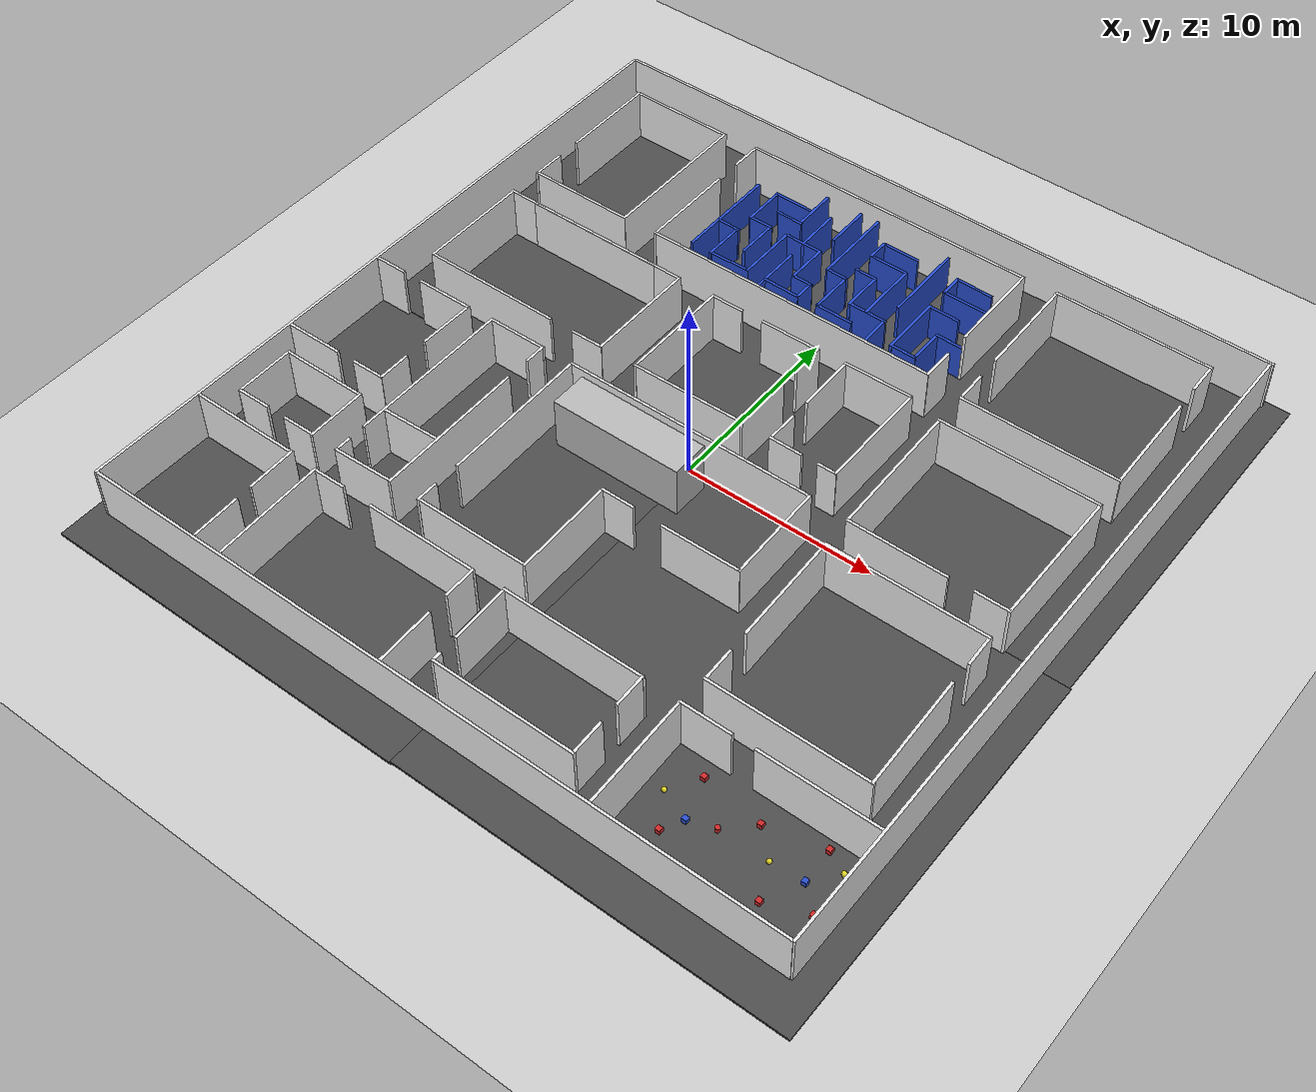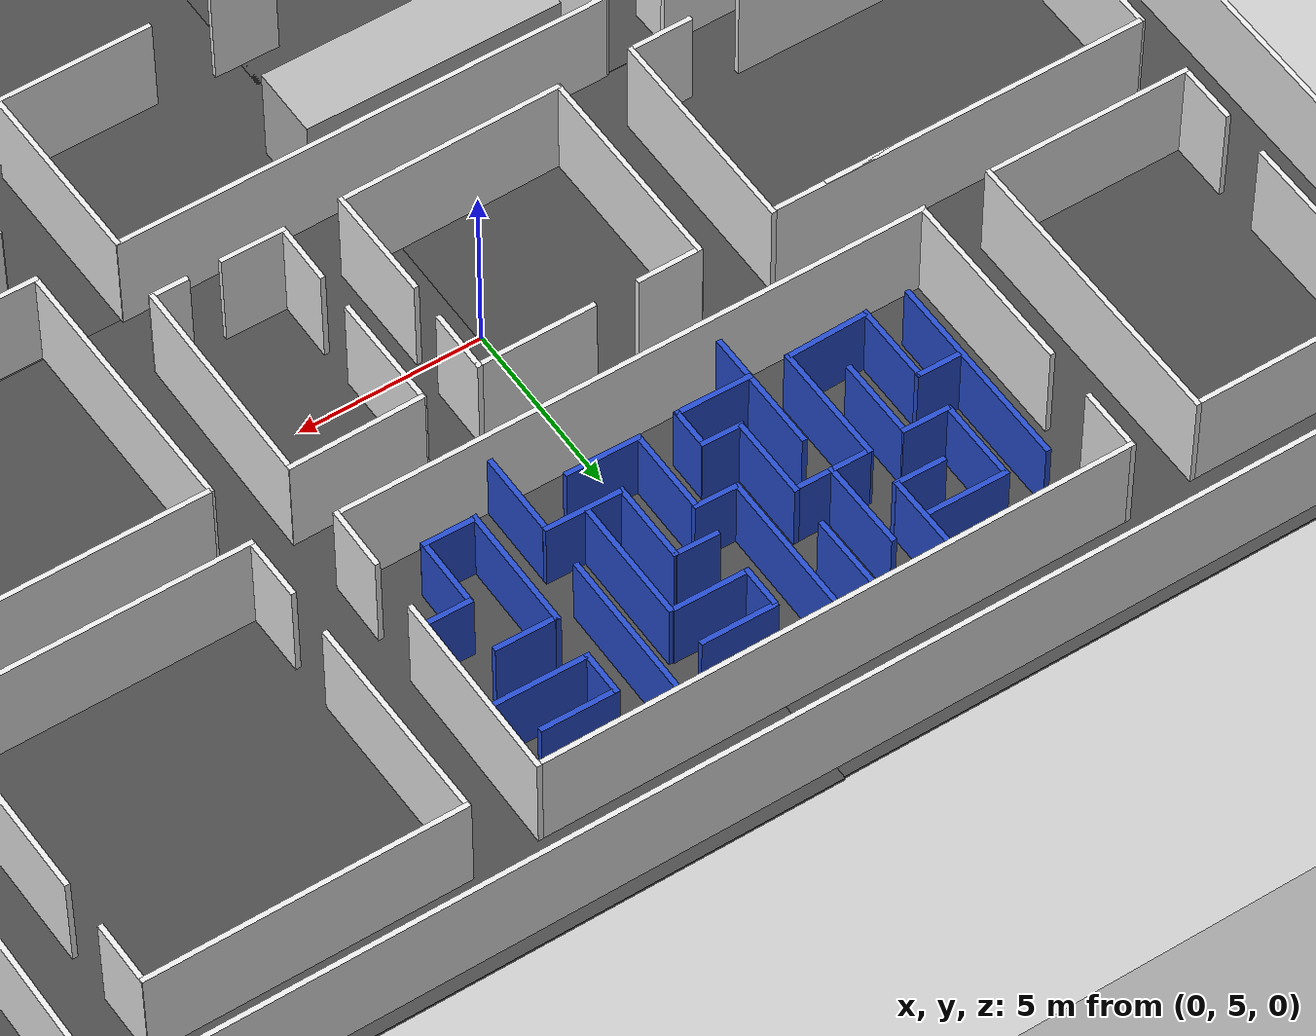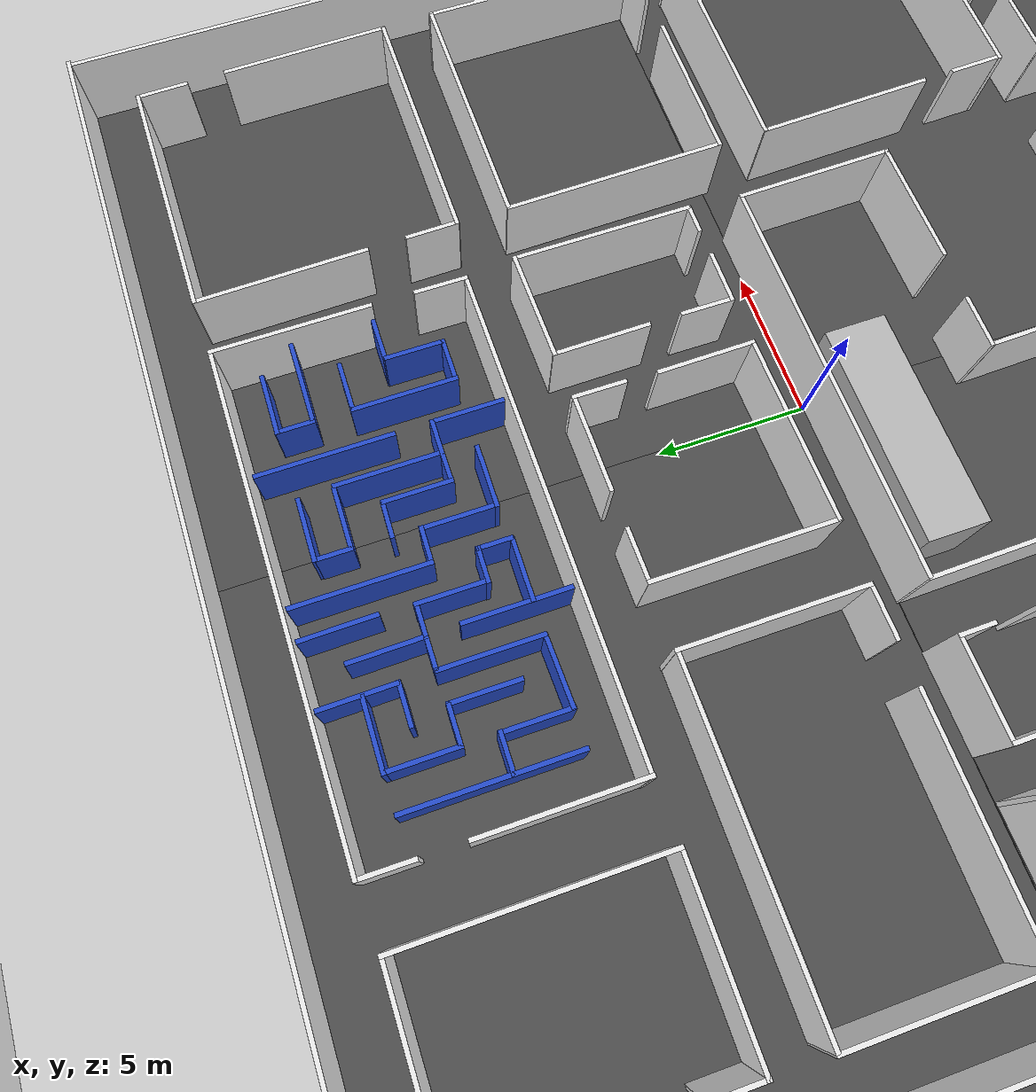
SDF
<sdf version="1.7">
 <world name="default">
  <light name="sun" type="directional">
   <pose>0 0 10 0 -0 0</pose>
   <diffuse>0.8 0.8 0.8 1</diffuse>
   <specular>0.2 0.2 0.2 1</specular>
   <attenuation>
    <range>1000</range>
    <constant>0.9</constant>
    <linear>0.01</linear>
    <quadratic>0.001</quadratic>
   </attenuation>
   <direction>-0.5 0.1 -0.9</direction>
   <spot><inner_angle>0</inner_angle><outer_angle>0</outer_angle><falloff>0</falloff></spot>
  </light>
  <model name="ground_plane">
   <static>1</static>
   <link name="link">
    <collision name="collision">
     <geometry><plane><normal>0 0 1</normal><size>100 100</size></plane></geometry>
     <surface><friction><ode><mu>100</mu><mu2>50</mu2></ode></friction></surface>
    </collision>
    <visual name="visual">
     <cast_shadows>0</cast_shadows>
     <geometry><plane><normal>0 0 1</normal><size>100 100</size></plane></geometry>
     <material>
      <script><uri>file://media/materials/scripts/gazebo.material</uri><name>Gazebo/Grey</name></script>
     </material>
    </visual>
    <velocity_decay><linear>0</linear><angular>0</angular></velocity_decay>
   </link>
  </model>
  <physics name="default_physics" default="0" type="ode">
   <max_step_size>0.001</max_step_size>
   <real_time_factor>1</real_time_factor>
   <real_time_update_rate>1000</real_time_update_rate>
  </physics>
  <scene><ambient>0.4 0.4 0.4 1</ambient><background>0.7 0.7 0.7 1</background><shadows>1</shadows></scene>
  <spherical_coordinates>
   <surface_model>EARTH_WGS84</surface_model>
   <latitude_deg>0</latitude_deg>
   <longitude_deg>0</longitude_deg>
   <elevation>0</elevation>
   <heading_deg>0</heading_deg>
  </spherical_coordinates>
  <gravity>0 0 -9.8</gravity>
  <magnetic_field>6e-06 2.3e-05 -4.2e-05</magnetic_field>
  <atmosphere type="adiabatic"/>
  <audio><device>default</device></audio>
  <light name="user_spot_light_0" type="spot">
   <pose>-0.377616 -5.07779 1 0 -0 0</pose>
   <diffuse>0.5 0.5 0.5 1</diffuse>
   <specular>0.1 0.1 0.1 1</specular>
   <direction>0 0 -1</direction>
   <attenuation>
    <range>20</range>
    <constant>0.5</constant>
    <linear>0.01</linear>
    <quadratic>0.001</quadratic>
   </attenuation>
   <cast_shadows>0</cast_shadows>
   <spot><inner_angle>0.6</inner_angle><outer_angle>1</outer_angle><falloff>1</falloff></spot>
  </light>
  <model name="asphalt_plane">
   <static>1</static>
   <link name="link">
    <collision name="collision"><geometry><box><size>20 20 0.1</size></box></geometry></collision>
    <visual name="visual">
     <cast_shadows>0</cast_shadows>
     <geometry><box><size>20 20 0.1</size></box></geometry>
     <material>
      <script>
       <uri>model://asphalt_plane/materials/scripts</uri>
       <uri>model://asphalt_plane/materials/textures</uri>
       <name>vrc/asphalt</name>
      </script>
     </material>
    </visual>
   </link>
   <pose>-9.73878 -10.1135 0 0 -0 0</pose>
  </model>
  <model name="asphalt_plane_0">
   <static>1</static>
   <link name="link">
    <collision name="collision"><geometry><box><size>20 20 0.1</size></box></geometry></collision>
    <visual name="visual">
     <cast_shadows>0</cast_shadows>
     <geometry><box><size>20 20 0.1</size></box></geometry>
     <material>
      <script>
       <uri>model://asphalt_plane/materials/scripts</uri>
       <uri>model://asphalt_plane/materials/textures</uri>
       <name>vrc/asphalt</name>
      </script>
     </material>
    </visual>
   </link>
   <pose>-9.90113 9.90141 0 0 -0 0</pose>
  </model>
  <model name="asphalt_plane_1">
   <static>1</static>
   <link name="link">
    <collision name="collision"><geometry><box><size>20 20 0.1</size></box></geometry></collision>
    <visual name="visual">
     <cast_shadows>0</cast_shadows>
     <geometry><box><size>20 20 0.1</size></box></geometry>
     <material>
      <script>
       <uri>model://asphalt_plane/materials/scripts</uri>
       <uri>model://asphalt_plane/materials/textures</uri>
       <name>vrc/asphalt</name>
      </script>
     </material>
    </visual>
   </link>
   <pose>10.1506 -10.0531 0 0 -0 0</pose>
  </model>
  <model name="asphalt_plane_2">
   <static>1</static>
   <link name="link">
    <collision name="collision"><geometry><box><size>20 20 0.1</size></box></geometry></collision>
    <visual name="visual">
     <cast_shadows>0</cast_shadows>
     <geometry><box><size>20 20 0.1</size></box></geometry>
     <material>
      <script>
       <uri>model://asphalt_plane/materials/scripts</uri>
       <uri>model://asphalt_plane/materials/textures</uri>
       <name>vrc/asphalt</name>
      </script>
     </material>
    </visual>
   </link>
   <pose>10.0797 9.93952 0 0 -0 0</pose>
  </model>
  <model name="white_wall_outside">
   <link name="link">
    <inertial>
     <mass>1</mass>
     <inertia>
      <ixx>0.166667</ixx>
      <ixy>0</ixy>
      <ixz>0</ixz>
      <iyy>0.166667</iyy>
      <iyz>0</iyz>
      <izz>0.166667</izz>
     </inertia>
    </inertial>
    <visual name="visual">
     <geometry><box><size>37.6355 0.139088 2.78993</size></box></geometry>
     <material>
      <script><name>Gazebo/White</name><uri>file://media/materials/scripts/gazebo.material</uri></script>
      <shader type="vertex"><normal_map>__default__</normal_map></shader>
      <ambient>1 1 1 1</ambient>
      <diffuse>1 1 1 1</diffuse>
      <specular>0 0 0 1</specular>
      <emissive>0 0 0 1</emissive>
     </material>
    </visual>
    <collision name="collision">
     <geometry><box><size>37.6355 0.139088 2.78993</size></box></geometry>
     <surface>
      <friction>
       <ode><mu>1</mu><mu2>1</mu2><fdir1>0 0 0</fdir1><slip1>0</slip1><slip2>0</slip2></ode>
       <torsional>
        <coefficient>1</coefficient>
        <patch_radius>0</patch_radius>
        <surface_radius>0</surface_radius>
        <use_patch_radius>1</use_patch_radius>
        <ode><slip>0</slip></ode>
       </torsional>
      </friction>
      <bounce><restitution_coefficient>0</restitution_coefficient><threshold>1e+06</threshold></bounce>
      <contact>
       <collide_without_contact>0</collide_without_contact>
       <collide_without_contact_bitmask>1</collide_without_contact_bitmask>
       <collide_bitmask>1</collide_bitmask>
       <ode>
        <soft_cfm>0</soft_cfm>
        <soft_erp>0.2</soft_erp>
        <kp>1e+13</kp>
        <kd>1</kd>
        <max_vel>0.01</max_vel>
        <min_depth>0</min_depth>
       </ode>
       <bullet>
        <split_impulse>1</split_impulse>
        <split_impulse_penetration_threshold>-0.01</split_impulse_penetration_threshold>
        <soft_cfm>0</soft_cfm>
        <soft_erp>0.2</soft_erp>
        <kp>1e+13</kp>
        <kd>1</kd>
       </bullet>
      </contact>
     </surface>
    </collision>
   </link>
   <static>1</static>
   <pose>0.019671 19.5408 1.44001 -1e-06 4e-06 -1.6e-05</pose>
  </model>
  <model name="white_wall_outside_clone">
   <link name="link">
    <inertial>
     <mass>1</mass>
     <inertia>
      <ixx>0.166667</ixx>
      <ixy>0</ixy>
      <ixz>0</ixz>
      <iyy>0.166667</iyy>
      <iyz>0</iyz>
      <izz>0.166667</izz>
     </inertia>
    </inertial>
    <visual name="visual">
     <geometry><box><size>37.6355 0.139088 2.78993</size></box></geometry>
     <material>
      <script><name>Gazebo/White</name><uri>file://media/materials/scripts/gazebo.material</uri></script>
      <shader type="vertex"><normal_map>__default__</normal_map></shader>
      <ambient>1 1 1 1</ambient>
      <diffuse>1 1 1 1</diffuse>
      <specular>0 0 0 1</specular>
      <emissive>0 0 0 1</emissive>
     </material>
    </visual>
    <collision name="collision">
     <geometry><box><size>37.6355 0.139088 2.78993</size></box></geometry>
     <surface>
      <friction>
       <ode><mu>1</mu><mu2>1</mu2><fdir1>0 0 0</fdir1><slip1>0</slip1><slip2>0</slip2></ode>
       <torsional>
        <coefficient>1</coefficient>
        <patch_radius>0</patch_radius>
        <surface_radius>0</surface_radius>
        <use_patch_radius>1</use_patch_radius>
        <ode><slip>0</slip></ode>
       </torsional>
      </friction>
      <bounce><restitution_coefficient>0</restitution_coefficient><threshold>1e+06</threshold></bounce>
      <contact>
       <collide_without_contact>0</collide_without_contact>
       <collide_without_contact_bitmask>1</collide_without_contact_bitmask>
       <collide_bitmask>1</collide_bitmask>
       <ode>
        <soft_cfm>0</soft_cfm>
        <soft_erp>0.2</soft_erp>
        <kp>1e+13</kp>
        <kd>1</kd>
        <max_vel>0.01</max_vel>
        <min_depth>0</min_depth>
       </ode>
       <bullet>
        <split_impulse>1</split_impulse>
        <split_impulse_penetration_threshold>-0.01</split_impulse_penetration_threshold>
        <soft_cfm>0</soft_cfm>
        <soft_erp>0.2</soft_erp>
        <kp>1e+13</kp>
        <kd>1</kd>
       </bullet>
      </contact>
     </surface>
    </collision>
   </link>
   <static>1</static>
   <pose>-0.112251 -17.9871 1.44002 -1e-06 4e-06 -1.6e-05</pose>
  </model>
  <model name="white_wall_outside_clone_0">
   <link name="link">
    <inertial>
     <mass>1</mass>
     <inertia>
      <ixx>0.166667</ixx>
      <ixy>0</ixy>
      <ixz>0</ixz>
      <iyy>0.166667</iyy>
      <iyz>0</iyz>
      <izz>0.166667</izz>
     </inertia>
    </inertial>
    <visual name="visual">
     <geometry><box><size>37.6355 0.139088 2.78993</size></box></geometry>
     <material>
      <script><name>Gazebo/White</name><uri>file://media/materials/scripts/gazebo.material</uri></script>
      <shader type="vertex"><normal_map>__default__</normal_map></shader>
      <ambient>1 1 1 1</ambient>
      <diffuse>1 1 1 1</diffuse>
      <specular>0 0 0 1</specular>
      <emissive>0 0 0 1</emissive>
     </material>
    </visual>
    <collision name="collision">
     <geometry><box><size>37.6355 0.139088 2.78993</size></box></geometry>
     <surface>
      <friction>
       <ode><mu>1</mu><mu2>1</mu2><fdir1>0 0 0</fdir1><slip1>0</slip1><slip2>0</slip2></ode>
       <torsional>
        <coefficient>1</coefficient>
        <patch_radius>0</patch_radius>
        <surface_radius>0</surface_radius>
        <use_patch_radius>1</use_patch_radius>
        <ode><slip>0</slip></ode>
       </torsional>
      </friction>
      <bounce><restitution_coefficient>0</restitution_coefficient><threshold>1e+06</threshold></bounce>
      <contact>
       <collide_without_contact>0</collide_without_contact>
       <collide_without_contact_bitmask>1</collide_without_contact_bitmask>
       <collide_bitmask>1</collide_bitmask>
       <ode>
        <soft_cfm>0</soft_cfm>
        <soft_erp>0.2</soft_erp>
        <kp>1e+13</kp>
        <kd>1</kd>
        <max_vel>0.01</max_vel>
        <min_depth>0</min_depth>
       </ode>
       <bullet>
        <split_impulse>1</split_impulse>
        <split_impulse_penetration_threshold>-0.01</split_impulse_penetration_threshold>
        <soft_cfm>0</soft_cfm>
        <soft_erp>0.2</soft_erp>
        <kp>1e+13</kp>
        <kd>1</kd>
       </bullet>
      </contact>
     </surface>
    </collision>
   </link>
   <static>1</static>
   <pose>18.7064 0.787366 1.43994 4e-06 1e-06 1.57249</pose>
  </model>
  <model name="white_wall_outside_clone_1">
   <link name="link">
    <inertial>
     <mass>1</mass>
     <inertia>
      <ixx>0.166667</ixx>
      <ixy>0</ixy>
      <ixz>0</ixz>
      <iyy>0.166667</iyy>
      <iyz>0</iyz>
      <izz>0.166667</izz>
     </inertia>
    </inertial>
    <visual name="visual">
     <geometry><box><size>37.6355 0.139088 2.78993</size></box></geometry>
     <material>
      <script><name>Gazebo/White</name><uri>file://media/materials/scripts/gazebo.material</uri></script>
      <shader type="vertex"><normal_map>__default__</normal_map></shader>
      <ambient>1 1 1 1</ambient>
      <diffuse>1 1 1 1</diffuse>
      <specular>0 0 0 1</specular>
      <emissive>0 0 0 1</emissive>
     </material>
    </visual>
    <collision name="collision">
     <geometry><box><size>37.6355 0.139088 2.78993</size></box></geometry>
     <surface>
      <friction>
       <ode><mu>1</mu><mu2>1</mu2><fdir1>0 0 0</fdir1><slip1>0</slip1><slip2>0</slip2></ode>
       <torsional>
        <coefficient>1</coefficient>
        <patch_radius>0</patch_radius>
        <surface_radius>0</surface_radius>
        <use_patch_radius>1</use_patch_radius>
        <ode><slip>0</slip></ode>
       </torsional>
      </friction>
      <bounce><restitution_coefficient>0</restitution_coefficient><threshold>1e+06</threshold></bounce>
      <contact>
       <collide_without_contact>0</collide_without_contact>
       <collide_without_contact_bitmask>1</collide_without_contact_bitmask>
       <collide_bitmask>1</collide_bitmask>
       <ode>
        <soft_cfm>0</soft_cfm>
        <soft_erp>0.2</soft_erp>
        <kp>1e+13</kp>
        <kd>1</kd>
        <max_vel>0.01</max_vel>
        <min_depth>0</min_depth>
       </ode>
       <bullet>
        <split_impulse>1</split_impulse>
        <split_impulse_penetration_threshold>-0.01</split_impulse_penetration_threshold>
        <soft_cfm>0</soft_cfm>
        <soft_erp>0.2</soft_erp>
        <kp>1e+13</kp>
        <kd>1</kd>
       </bullet>
      </contact>
     </surface>
    </collision>
   </link>
   <static>1</static>
   <pose>-18.8746 0.750399 1.44009 4e-06 1e-06 1.56558</pose>
  </model>
  <model name="white_wall3">
   <link name="link">
    <inertial>
     <mass>1</mass>
     <inertia>
      <ixx>0.166667</ixx>
      <ixy>0</ixy>
      <ixz>0</ixz>
      <iyy>0.166667</iyy>
      <iyz>0</iyz>
      <izz>0.166667</izz>
     </inertia>
    </inertial>
    <visual name="visual">
     <geometry><box><size>1.77743 0.139088 2.78993</size></box></geometry>
     <material>
      <script><name>Gazebo/White</name><uri>file://media/materials/scripts/gazebo.material</uri></script>
      <shader type="vertex"><normal_map>__default__</normal_map></shader>
      <ambient>1 1 1 1</ambient>
      <diffuse>1 1 1 1</diffuse>
      <specular>0 0 0 1</specular>
      <emissive>0 0 0 1</emissive>
     </material>
    </visual>
    <collision name="collision">
     <geometry><box><size>1.77743 0.139088 2.78993</size></box></geometry>
     <surface>
      <friction>
       <ode><mu>1</mu><mu2>1</mu2><fdir1>0 0 0</fdir1><slip1>0</slip1><slip2>0</slip2></ode>
       <torsional>
        <coefficient>1</coefficient>
        <patch_radius>0</patch_radius>
        <surface_radius>0</surface_radius>
        <use_patch_radius>1</use_patch_radius>
        <ode><slip>0</slip></ode>
       </torsional>
      </friction>
      <bounce><restitution_coefficient>0</restitution_coefficient><threshold>1e+06</threshold></bounce>
      <contact>
       <collide_without_contact>0</collide_without_contact>
       <collide_without_contact_bitmask>1</collide_without_contact_bitmask>
       <collide_bitmask>1</collide_bitmask>
       <ode>
        <soft_cfm>0</soft_cfm>
        <soft_erp>0.2</soft_erp>
        <kp>1e+13</kp>
        <kd>1</kd>
        <max_vel>0.01</max_vel>
        <min_depth>0</min_depth>
       </ode>
       <bullet>
        <split_impulse>1</split_impulse>
        <split_impulse_penetration_threshold>-0.01</split_impulse_penetration_threshold>
        <soft_cfm>0</soft_cfm>
        <soft_erp>0.2</soft_erp>
        <kp>1e+13</kp>
        <kd>1</kd>
       </bullet>
      </contact>
     </surface>
    </collision>
   </link>
   <static>1</static>
   <pose>6.94731 -12.8803 1.43995 4e-06 1e-06 1.59932</pose>
  </model>
  <model name="white_wall4">
   <link name="link">
    <inertial>
     <mass>1</mass>
     <inertia>
      <ixx>0.166667</ixx>
      <ixy>0</ixy>
      <ixz>0</ixz>
      <iyy>0.166667</iyy>
      <iyz>0</iyz>
      <izz>0.166667</izz>
     </inertia>
    </inertial>
    <visual name="visual">
     <geometry><box><size>6.20543 0.139088 2.78993</size></box></geometry>
     <material>
      <script><name>Gazebo/White</name><uri>file://media/materials/scripts/gazebo.material</uri></script>
      <shader type="vertex"><normal_map>__default__</normal_map></shader>
      <ambient>1 1 1 1</ambient>
      <diffuse>1 1 1 1</diffuse>
      <specular>0 0 0 1</specular>
      <emissive>0 0 0 1</emissive>
     </material>
    </visual>
    <collision name="collision">
     <geometry><box><size>6.20543 0.139088 2.78993</size></box></geometry>
     <surface>
      <friction>
       <ode><mu>1</mu><mu2>1</mu2><fdir1>0 0 0</fdir1><slip1>0</slip1><slip2>0</slip2></ode>
       <torsional>
        <coefficient>1</coefficient>
        <patch_radius>0</patch_radius>
        <surface_radius>0</surface_radius>
        <use_patch_radius>1</use_patch_radius>
        <ode><slip>0</slip></ode>
       </torsional>
      </friction>
      <bounce><restitution_coefficient>0</restitution_coefficient><threshold>1e+06</threshold></bounce>
      <contact>
       <collide_without_contact>0</collide_without_contact>
       <collide_without_contact_bitmask>1</collide_without_contact_bitmask>
       <collide_bitmask>1</collide_bitmask>
       <ode>
        <soft_cfm>0</soft_cfm>
        <soft_erp>0.2</soft_erp>
        <kp>1e+13</kp>
        <kd>1</kd>
        <max_vel>0.01</max_vel>
        <min_depth>0</min_depth>
       </ode>
       <bullet>
        <split_impulse>1</split_impulse>
        <split_impulse_penetration_threshold>-0.01</split_impulse_penetration_threshold>
        <soft_cfm>0</soft_cfm>
        <soft_erp>0.2</soft_erp>
        <kp>1e+13</kp>
        <kd>1</kd>
       </bullet>
      </contact>
     </surface>
    </collision>
   </link>
   <static>1</static>
   <pose>15.6823 -12.076 1.43996 -1e-06 4e-06 -1.6e-05</pose>
  </model>
  <model name="white_wall5">
   <link name="link">
    <inertial>
     <mass>1</mass>
     <inertia>
      <ixx>0.166667</ixx>
      <ixy>0</ixy>
      <ixz>0</ixz>
      <iyy>0.166667</iyy>
      <iyz>0</iyz>
      <izz>0.166667</izz>
     </inertia>
    </inertial>
    <visual name="visual">
     <geometry><box><size>2.62905 0.139088 2.78993</size></box></geometry>
     <material>
      <script><name>Gazebo/White</name><uri>file://media/materials/scripts/gazebo.material</uri></script>
      <shader type="vertex"><normal_map>__default__</normal_map></shader>
      <ambient>1 1 1 1</ambient>
      <diffuse>1 1 1 1</diffuse>
      <specular>0 0 0 1</specular>
      <emissive>0 0 0 1</emissive>
     </material>
    </visual>
    <collision name="collision">
     <geometry><box><size>2.62905 0.139088 2.78993</size></box></geometry>
     <surface>
      <friction>
       <ode><mu>1</mu><mu2>1</mu2><fdir1>0 0 0</fdir1><slip1>0</slip1><slip2>0</slip2></ode>
       <torsional>
        <coefficient>1</coefficient>
        <patch_radius>0</patch_radius>
        <surface_radius>0</surface_radius>
        <use_patch_radius>1</use_patch_radius>
        <ode><slip>0</slip></ode>
       </torsional>
      </friction>
      <bounce><restitution_coefficient>0</restitution_coefficient><threshold>1e+06</threshold></bounce>
      <contact>
       <collide_without_contact>0</collide_without_contact>
       <collide_without_contact_bitmask>1</collide_without_contact_bitmask>
       <collide_bitmask>1</collide_bitmask>
       <ode>
        <soft_cfm>0</soft_cfm>
        <soft_erp>0.2</soft_erp>
        <kp>1e+13</kp>
        <kd>1</kd>
        <max_vel>0.01</max_vel>
        <min_depth>0</min_depth>
       </ode>
       <bullet>
        <split_impulse>1</split_impulse>
        <split_impulse_penetration_threshold>-0.01</split_impulse_penetration_threshold>
        <soft_cfm>0</soft_cfm>
        <soft_erp>0.2</soft_erp>
        <kp>1e+13</kp>
        <kd>1</kd>
       </bullet>
      </contact>
     </surface>
    </collision>
   </link>
   <static>1</static>
   <pose>10.1577 -12.0848 1.43996 -1e-06 4e-06 -1.6e-05</pose>
  </model>
  <model name="white_wall1">
   <link name="link">
    <inertial>
     <mass>1</mass>
     <inertia>
      <ixx>0.166667</ixx>
      <ixy>0</ixy>
      <ixz>0</ixz>
      <iyy>0.166667</iyy>
      <iyz>0</iyz>
      <izz>0.166667</izz>
     </inertia>
    </inertial>
    <visual name="visual">
     <geometry><box><size>7.516 0.139088 2.78993</size></box></geometry>
     <material>
      <script><name>Gazebo/White</name><uri>file://media/materials/scripts/gazebo.material</uri></script>
      <shader type="vertex"><normal_map>__default__</normal_map></shader>
      <ambient>1 1 1 1</ambient>
      <diffuse>1 1 1 1</diffuse>
      <specular>0 0 0 1</specular>
      <emissive>0 0 0 1</emissive>
     </material>
    </visual>
    <collision name="collision">
     <geometry><box><size>7.516 0.139088 2.78993</size></box></geometry>
     <surface>
      <friction>
       <ode><mu>1</mu><mu2>1</mu2><fdir1>0 0 0</fdir1><slip1>0</slip1><slip2>0</slip2></ode>
       <torsional>
        <coefficient>1</coefficient>
        <patch_radius>0</patch_radius>
        <surface_radius>0</surface_radius>
        <use_patch_radius>1</use_patch_radius>
        <ode><slip>0</slip></ode>
       </torsional>
      </friction>
      <bounce><restitution_coefficient>0</restitution_coefficient><threshold>1e+06</threshold></bounce>
      <contact>
       <collide_without_contact>0</collide_without_contact>
       <collide_without_contact_bitmask>1</collide_without_contact_bitmask>
       <collide_bitmask>1</collide_bitmask>
       <ode>
        <soft_cfm>0</soft_cfm>
        <soft_erp>0.2</soft_erp>
        <kp>1e+13</kp>
        <kd>1</kd>
        <max_vel>0.01</max_vel>
        <min_depth>0</min_depth>
       </ode>
       <bullet>
        <split_impulse>1</split_impulse>
        <split_impulse_penetration_threshold>-0.01</split_impulse_penetration_threshold>
        <soft_cfm>0</soft_cfm>
        <soft_erp>0.2</soft_erp>
        <kp>1e+13</kp>
        <kd>1</kd>
       </bullet>
      </contact>
     </surface>
    </collision>
   </link>
   <static>1</static>
   <pose>3.24328 -12.0447 1.43996 -1e-06 4e-06 -1.6e-05</pose>
  </model>
  <model name="white_wall2_clone">
   <link name="link">
    <inertial>
     <mass>1</mass>
     <inertia>
      <ixx>0.166667</ixx>
      <ixy>0</ixy>
      <ixz>0</ixz>
      <iyy>0.166667</iyy>
      <iyz>0</iyz>
      <izz>0.166667</izz>
     </inertia>
    </inertial>
    <visual name="visual">
     <geometry><box><size>3.22688 0.139088 2.78993</size></box></geometry>
     <material>
      <script><name>Gazebo/White</name><uri>file://media/materials/scripts/gazebo.material</uri></script>
      <shader type="vertex"><normal_map>__default__</normal_map></shader>
      <ambient>1 1 1 1</ambient>
      <diffuse>1 1 1 1</diffuse>
      <specular>0 0 0 1</specular>
      <emissive>0 0 0 1</emissive>
     </material>
    </visual>
    <collision name="collision">
     <geometry><box><size>3.22688 0.139088 2.78993</size></box></geometry>
     <surface>
      <friction>
       <ode><mu>1</mu><mu2>1</mu2><fdir1>0 0 0</fdir1><slip1>0</slip1><slip2>0</slip2></ode>
       <torsional>
        <coefficient>1</coefficient>
        <patch_radius>0</patch_radius>
        <surface_radius>0</surface_radius>
        <use_patch_radius>1</use_patch_radius>
        <ode><slip>0</slip></ode>
       </torsional>
      </friction>
      <bounce><restitution_coefficient>0</restitution_coefficient><threshold>1e+06</threshold></bounce>
      <contact>
       <collide_without_contact>0</collide_without_contact>
       <collide_without_contact_bitmask>1</collide_without_contact_bitmask>
       <collide_bitmask>1</collide_bitmask>
       <ode>
        <soft_cfm>0</soft_cfm>
        <soft_erp>0.2</soft_erp>
        <kp>1e+13</kp>
        <kd>1</kd>
        <max_vel>0.01</max_vel>
        <min_depth>0</min_depth>
       </ode>
       <bullet>
        <split_impulse>1</split_impulse>
        <split_impulse_penetration_threshold>-0.01</split_impulse_penetration_threshold>
        <soft_cfm>0</soft_cfm>
        <soft_erp>0.2</soft_erp>
        <kp>1e+13</kp>
        <kd>1</kd>
       </bullet>
      </contact>
     </surface>
    </collision>
   </link>
   <static>1</static>
   <pose>-0.413972 -13.5813 1.43995 4e-06 1e-06 1.59932</pose>
  </model>
  <model name="white_wall2_clone_clone">
   <link name="link">
    <inertial>
     <mass>1</mass>
     <inertia>
      <ixx>0.166667</ixx>
      <ixy>0</ixy>
      <ixz>0</ixz>
      <iyy>0.166667</iyy>
      <iyz>0</iyz>
      <izz>0.166667</izz>
     </inertia>
    </inertial>
    <visual name="visual">
     <geometry><box><size>3.22688 0.139088 2.78993</size></box></geometry>
     <material>
      <script><name>Gazebo/White</name><uri>file://media/materials/scripts/gazebo.material</uri></script>
      <shader type="vertex"><normal_map>__default__</normal_map></shader>
      <ambient>1 1 1 1</ambient>
      <diffuse>1 1 1 1</diffuse>
      <specular>0 0 0 1</specular>
      <emissive>0 0 0 1</emissive>
     </material>
    </visual>
    <collision name="collision">
     <geometry><box><size>3.22688 0.139088 2.78993</size></box></geometry>
     <surface>
      <friction>
       <ode><mu>1</mu><mu2>1</mu2><fdir1>0 0 0</fdir1><slip1>0</slip1><slip2>0</slip2></ode>
       <torsional>
        <coefficient>1</coefficient>
        <patch_radius>0</patch_radius>
        <surface_radius>0</surface_radius>
        <use_patch_radius>1</use_patch_radius>
        <ode><slip>0</slip></ode>
       </torsional>
      </friction>
      <bounce><restitution_coefficient>0</restitution_coefficient><threshold>1e+06</threshold></bounce>
      <contact>
       <collide_without_contact>0</collide_without_contact>
       <collide_without_contact_bitmask>1</collide_without_contact_bitmask>
       <collide_bitmask>1</collide_bitmask>
       <ode>
        <soft_cfm>0</soft_cfm>
        <soft_erp>0.2</soft_erp>
        <kp>1e+13</kp>
        <kd>1</kd>
        <max_vel>0.01</max_vel>
        <min_depth>0</min_depth>
       </ode>
       <bullet>
        <split_impulse>1</split_impulse>
        <split_impulse_penetration_threshold>-0.01</split_impulse_penetration_threshold>
        <soft_cfm>0</soft_cfm>
        <soft_erp>0.2</soft_erp>
        <kp>1e+13</kp>
        <kd>1</kd>
       </bullet>
      </contact>
     </surface>
    </collision>
   </link>
   <static>1</static>
   <pose>-2.06384 -16.4395 1.43995 4e-06 1e-06 1.59932</pose>
  </model>
  <model name="white_wall3_clone_clone">
   <link name="link">
    <inertial>
     <mass>1</mass>
     <inertia>
      <ixx>0.166667</ixx>
      <ixy>0</ixy>
      <ixz>0</ixz>
      <iyy>0.166667</iyy>
      <iyz>0</iyz>
      <izz>0.166667</izz>
     </inertia>
    </inertial>
    <visual name="visual">
     <geometry><box><size>1.77743 0.139088 2.78993</size></box></geometry>
     <material>
      <script><name>Gazebo/White</name><uri>file://media/materials/scripts/gazebo.material</uri></script>
      <shader type="vertex"><normal_map>__default__</normal_map></shader>
      <ambient>1 1 1 1</ambient>
      <diffuse>1 1 1 1</diffuse>
      <specular>0 0 0 1</specular>
      <emissive>0 0 0 1</emissive>
     </material>
    </visual>
    <collision name="collision">
     <geometry><box><size>1.77743 0.139088 2.78993</size></box></geometry>
     <surface>
      <friction>
       <ode><mu>1</mu><mu2>1</mu2><fdir1>0 0 0</fdir1><slip1>0</slip1><slip2>0</slip2></ode>
       <torsional>
        <coefficient>1</coefficient>
        <patch_radius>0</patch_radius>
        <surface_radius>0</surface_radius>
        <use_patch_radius>1</use_patch_radius>
        <ode><slip>0</slip></ode>
       </torsional>
      </friction>
      <bounce><restitution_coefficient>0</restitution_coefficient><threshold>1e+06</threshold></bounce>
      <contact>
       <collide_without_contact>0</collide_without_contact>
       <collide_without_contact_bitmask>1</collide_without_contact_bitmask>
       <collide_bitmask>1</collide_bitmask>
       <ode>
        <soft_cfm>0</soft_cfm>
        <soft_erp>0.2</soft_erp>
        <kp>1e+13</kp>
        <kd>1</kd>
        <max_vel>0.01</max_vel>
        <min_depth>0</min_depth>
       </ode>
       <bullet>
        <split_impulse>1</split_impulse>
        <split_impulse_penetration_threshold>-0.01</split_impulse_penetration_threshold>
        <soft_cfm>0</soft_cfm>
        <soft_erp>0.2</soft_erp>
        <kp>1e+13</kp>
        <kd>1</kd>
       </bullet>
      </contact>
     </surface>
    </collision>
   </link>
   <static>1</static>
   <pose>-2.17837 -12.9037 1.43995 4e-06 1e-06 1.59932</pose>
  </model>
  <model name="white_wall6_clone">
   <link name="link">
    <inertial>
     <mass>1</mass>
     <inertia>
      <ixx>0.166667</ixx>
      <ixy>0</ixy>
      <ixz>0</ixz>
      <iyy>0.166667</iyy>
      <iyz>0</iyz>
      <izz>0.166667</izz>
     </inertia>
    </inertial>
    <visual name="visual">
     <geometry><box><size>6.01508 0.139088 2.78993</size></box></geometry>
     <material>
      <script><name>Gazebo/White</name><uri>file://media/materials/scripts/gazebo.material</uri></script>
      <shader type="vertex"><normal_map>__default__</normal_map></shader>
      <ambient>1 1 1 1</ambient>
      <diffuse>1 1 1 1</diffuse>
      <specular>0 0 0 1</specular>
      <emissive>0 0 0 1</emissive>
     </material>
    </visual>
    <collision name="collision">
     <geometry><box><size>6.01508 0.139088 2.78993</size></box></geometry>
     <surface>
      <friction>
       <ode><mu>1</mu><mu2>1</mu2><fdir1>0 0 0</fdir1><slip1>0</slip1><slip2>0</slip2></ode>
       <torsional>
        <coefficient>1</coefficient>
        <patch_radius>0</patch_radius>
        <surface_radius>0</surface_radius>
        <use_patch_radius>1</use_patch_radius>
        <ode><slip>0</slip></ode>
       </torsional>
      </friction>
      <bounce><restitution_coefficient>0</restitution_coefficient><threshold>1e+06</threshold></bounce>
      <contact>
       <collide_without_contact>0</collide_without_contact>
       <collide_without_contact_bitmask>1</collide_without_contact_bitmask>
       <collide_bitmask>1</collide_bitmask>
       <ode>
        <soft_cfm>0</soft_cfm>
        <soft_erp>0.2</soft_erp>
        <kp>1e+13</kp>
        <kd>1</kd>
        <max_vel>0.01</max_vel>
        <min_depth>0</min_depth>
       </ode>
       <bullet>
        <split_impulse>1</split_impulse>
        <split_impulse_penetration_threshold>-0.01</split_impulse_penetration_threshold>
        <soft_cfm>0</soft_cfm>
        <soft_erp>0.2</soft_erp>
        <kp>1e+13</kp>
        <kd>1</kd>
       </bullet>
      </contact>
     </surface>
    </collision>
   </link>
   <static>1</static>
   <pose>-11.3944 -14.9604 1.43998 4e-06 1e-06 1.59932</pose>
  </model>
  <model name="white_wall3_clone_clone_0">
   <link name="link">
    <inertial>
     <mass>1</mass>
     <inertia>
      <ixx>0.166667</ixx>
      <ixy>0</ixy>
      <ixz>0</ixz>
      <iyy>0.166667</iyy>
      <iyz>0</iyz>
      <izz>0.166667</izz>
     </inertia>
    </inertial>
    <visual name="visual">
     <geometry><box><size>1.77743 0.139088 2.78993</size></box></geometry>
     <material>
      <script><name>Gazebo/White</name><uri>file://media/materials/scripts/gazebo.material</uri></script>
      <shader type="vertex"><normal_map>__default__</normal_map></shader>
      <ambient>1 1 1 1</ambient>
      <diffuse>1 1 1 1</diffuse>
      <specular>0 0 0 1</specular>
      <emissive>0 0 0 1</emissive>
     </material>
    </visual>
    <collision name="collision">
     <geometry><box><size>1.77743 0.139088 2.78993</size></box></geometry>
     <surface>
      <friction>
       <ode><mu>1</mu><mu2>1</mu2><fdir1>0 0 0</fdir1><slip1>0</slip1><slip2>0</slip2></ode>
       <torsional>
        <coefficient>1</coefficient>
        <patch_radius>0</patch_radius>
        <surface_radius>0</surface_radius>
        <use_patch_radius>1</use_patch_radius>
        <ode><slip>0</slip></ode>
       </torsional>
      </friction>
      <bounce><restitution_coefficient>0</restitution_coefficient><threshold>1e+06</threshold></bounce>
      <contact>
       <collide_without_contact>0</collide_without_contact>
       <collide_without_contact_bitmask>1</collide_without_contact_bitmask>
       <collide_bitmask>1</collide_bitmask>
       <ode>
        <soft_cfm>0</soft_cfm>
        <soft_erp>0.2</soft_erp>
        <kp>1e+13</kp>
        <kd>1</kd>
        <max_vel>0.01</max_vel>
        <min_depth>0</min_depth>
       </ode>
       <bullet>
        <split_impulse>1</split_impulse>
        <split_impulse_penetration_threshold>-0.01</split_impulse_penetration_threshold>
        <soft_cfm>0</soft_cfm>
        <soft_erp>0.2</soft_erp>
        <kp>1e+13</kp>
        <kd>1</kd>
       </bullet>
      </contact>
     </surface>
    </collision>
   </link>
   <static>1</static>
   <pose>-10.627 -12.0267 1.43995 -1e-06 4e-06 0.011343</pose>
  </model>
  <model name="white_wall7">
   <link name="link">
    <inertial>
     <mass>1</mass>
     <inertia>
      <ixx>0.166667</ixx>
      <ixy>0</ixy>
      <ixz>0</ixz>
      <iyy>0.166667</iyy>
      <iyz>0</iyz>
      <izz>0.166667</izz>
     </inertia>
    </inertial>
    <visual name="visual">
     <geometry><box><size>2.66208 0.139088 2.78993</size></box></geometry>
     <material>
      <script><name>Gazebo/White</name><uri>file://media/materials/scripts/gazebo.material</uri></script>
      <shader type="vertex"><normal_map>__default__</normal_map></shader>
      <ambient>1 1 1 1</ambient>
      <diffuse>1 1 1 1</diffuse>
      <specular>0 0 0 1</specular>
      <emissive>0 0 0 1</emissive>
     </material>
    </visual>
    <collision name="collision">
     <geometry><box><size>2.66208 0.139088 2.78993</size></box></geometry>
     <surface>
      <friction>
       <ode><mu>1</mu><mu2>1</mu2><fdir1>0 0 0</fdir1><slip1>0</slip1><slip2>0</slip2></ode>
       <torsional>
        <coefficient>1</coefficient>
        <patch_radius>0</patch_radius>
        <surface_radius>0</surface_radius>
        <use_patch_radius>1</use_patch_radius>
        <ode><slip>0</slip></ode>
       </torsional>
      </friction>
      <bounce><restitution_coefficient>0</restitution_coefficient><threshold>1e+06</threshold></bounce>
      <contact>
       <collide_without_contact>0</collide_without_contact>
       <collide_without_contact_bitmask>1</collide_without_contact_bitmask>
       <collide_bitmask>1</collide_bitmask>
       <ode>
        <soft_cfm>0</soft_cfm>
        <soft_erp>0.2</soft_erp>
        <kp>1e+13</kp>
        <kd>1</kd>
        <max_vel>0.01</max_vel>
        <min_depth>0</min_depth>
       </ode>
       <bullet>
        <split_impulse>1</split_impulse>
        <split_impulse_penetration_threshold>-0.01</split_impulse_penetration_threshold>
        <soft_cfm>0</soft_cfm>
        <soft_erp>0.2</soft_erp>
        <kp>1e+13</kp>
        <kd>1</kd>
       </bullet>
      </contact>
     </surface>
    </collision>
   </link>
   <static>1</static>
   <pose>-12.9108 -16.6468 1.43998 4e-06 1e-06 1.59932</pose>
  </model>
  <model name="white_wall7_clone">
   <link name="link">
    <inertial>
     <mass>1</mass>
     <inertia>
      <ixx>0.166667</ixx>
      <ixy>0</ixy>
      <ixz>0</ixz>
      <iyy>0.166667</iyy>
      <iyz>0</iyz>
      <izz>0.166667</izz>
     </inertia>
    </inertial>
    <visual name="visual">
     <geometry><box><size>2.66208 0.139088 2.78993</size></box></geometry>
     <material>
      <script><name>Gazebo/White</name><uri>file://media/materials/scripts/gazebo.material</uri></script>
      <shader type="vertex"><normal_map>__default__</normal_map></shader>
      <ambient>1 1 1 1</ambient>
      <diffuse>1 1 1 1</diffuse>
      <specular>0 0 0 1</specular>
      <emissive>0 0 0 1</emissive>
     </material>
    </visual>
    <collision name="collision">
     <geometry><box><size>2.66208 0.139088 2.78993</size></box></geometry>
     <surface>
      <friction>
       <ode><mu>1</mu><mu2>1</mu2><fdir1>0 0 0</fdir1><slip1>0</slip1><slip2>0</slip2></ode>
       <torsional>
        <coefficient>1</coefficient>
        <patch_radius>0</patch_radius>
        <surface_radius>0</surface_radius>
        <use_patch_radius>1</use_patch_radius>
        <ode><slip>0</slip></ode>
       </torsional>
      </friction>
      <bounce><restitution_coefficient>0</restitution_coefficient><threshold>1e+06</threshold></bounce>
      <contact>
       <collide_without_contact>0</collide_without_contact>
       <collide_without_contact_bitmask>1</collide_without_contact_bitmask>
       <collide_bitmask>1</collide_bitmask>
       <ode>
        <soft_cfm>0</soft_cfm>
        <soft_erp>0.2</soft_erp>
        <kp>1e+13</kp>
        <kd>1</kd>
        <max_vel>0.01</max_vel>
        <min_depth>0</min_depth>
       </ode>
       <bullet>
        <split_impulse>1</split_impulse>
        <split_impulse_penetration_threshold>-0.01</split_impulse_penetration_threshold>
        <soft_cfm>0</soft_cfm>
        <soft_erp>0.2</soft_erp>
        <kp>1e+13</kp>
        <kd>1</kd>
       </bullet>
      </contact>
     </surface>
    </collision>
   </link>
   <static>1</static>
   <pose>-13.0032 -13.1745 1.43998 4e-06 1e-06 1.59932</pose>
  </model>
  <model name="white_wall8">
   <link name="link">
    <inertial>
     <mass>1</mass>
     <inertia>
      <ixx>0.166667</ixx>
      <ixy>0</ixy>
      <ixz>0</ixz>
      <iyy>0.166667</iyy>
      <iyz>0</iyz>
      <izz>0.166667</izz>
     </inertia>
    </inertial>
    <visual name="visual">
     <geometry><box><size>8.30741 0.139088 2.78993</size></box></geometry>
     <material>
      <script><name>Gazebo/White</name><uri>file://media/materials/scripts/gazebo.material</uri></script>
      <shader type="vertex"><normal_map>__default__</normal_map></shader>
      <ambient>1 1 1 1</ambient>
      <diffuse>1 1 1 1</diffuse>
      <specular>0 0 0 1</specular>
      <emissive>0 0 0 1</emissive>
     </material>
    </visual>
    <collision name="collision">
     <geometry><box><size>8.30741 0.139088 2.78993</size></box></geometry>
     <surface>
      <friction>
       <ode><mu>1</mu><mu2>1</mu2><fdir1>0 0 0</fdir1><slip1>0</slip1><slip2>0</slip2></ode>
       <torsional>
        <coefficient>1</coefficient>
        <patch_radius>0</patch_radius>
        <surface_radius>0</surface_radius>
        <use_patch_radius>1</use_patch_radius>
        <ode><slip>0</slip></ode>
       </torsional>
      </friction>
      <bounce><restitution_coefficient>0</restitution_coefficient><threshold>1e+06</threshold></bounce>
      <contact>
       <collide_without_contact>0</collide_without_contact>
       <collide_without_contact_bitmask>1</collide_without_contact_bitmask>
       <collide_bitmask>1</collide_bitmask>
       <ode>
        <soft_cfm>0</soft_cfm>
        <soft_erp>0.2</soft_erp>
        <kp>1e+13</kp>
        <kd>1</kd>
        <max_vel>0.01</max_vel>
        <min_depth>0</min_depth>
       </ode>
       <bullet>
        <split_impulse>1</split_impulse>
        <split_impulse_penetration_threshold>-0.01</split_impulse_penetration_threshold>
        <soft_cfm>0</soft_cfm>
        <soft_erp>0.2</soft_erp>
        <kp>1e+13</kp>
        <kd>1</kd>
       </bullet>
      </contact>
     </surface>
    </collision>
   </link>
   <static>1</static>
   <pose>13.0532 -10.5824 1.43997 -1e-06 4e-06 -1.6e-05</pose>
  </model>
  <model name="white_wall9">
   <link name="link">
    <inertial>
     <mass>1</mass>
     <inertia>
      <ixx>0.166667</ixx>
      <ixy>0</ixy>
      <ixz>0</ixz>
      <iyy>0.166667</iyy>
      <iyz>0</iyz>
      <izz>0.166667</izz>
     </inertia>
    </inertial>
    <visual name="visual">
     <geometry><box><size>6.01507 0.139088 2.78993</size></box></geometry>
     <material>
      <script><name>Gazebo/White</name><uri>file://media/materials/scripts/gazebo.material</uri></script>
      <shader type="vertex"><normal_map>__default__</normal_map></shader>
      <ambient>1 1 1 1</ambient>
      <diffuse>1 1 1 1</diffuse>
      <specular>0 0 0 1</specular>
      <emissive>0 0 0 1</emissive>
     </material>
    </visual>
    <collision name="collision">
     <geometry><box><size>6.01507 0.139088 2.78993</size></box></geometry>
     <surface>
      <friction>
       <ode><mu>1</mu><mu2>1</mu2><fdir1>0 0 0</fdir1><slip1>0</slip1><slip2>0</slip2></ode>
       <torsional>
        <coefficient>1</coefficient>
        <patch_radius>0</patch_radius>
        <surface_radius>0</surface_radius>
        <use_patch_radius>1</use_patch_radius>
        <ode><slip>0</slip></ode>
       </torsional>
      </friction>
      <bounce><restitution_coefficient>0</restitution_coefficient><threshold>1e+06</threshold></bounce>
      <contact>
       <collide_without_contact>0</collide_without_contact>
       <collide_without_contact_bitmask>1</collide_without_contact_bitmask>
       <collide_bitmask>1</collide_bitmask>
       <ode>
        <soft_cfm>0</soft_cfm>
        <soft_erp>0.2</soft_erp>
        <kp>1e+13</kp>
        <kd>1</kd>
        <max_vel>0.01</max_vel>
        <min_depth>0</min_depth>
       </ode>
       <bullet>
        <split_impulse>1</split_impulse>
        <split_impulse_penetration_threshold>-0.01</split_impulse_penetration_threshold>
        <soft_cfm>0</soft_cfm>
        <soft_erp>0.2</soft_erp>
        <kp>1e+13</kp>
        <kd>1</kd>
       </bullet>
      </contact>
     </surface>
    </collision>
   </link>
   <static>1</static>
   <pose>-15.9801 -11.9426 1.43994 -1e-06 4e-06 -1.6e-05</pose>
  </model>
  <model name="white_wall10">
   <link name="link">
    <inertial>
     <mass>1</mass>
     <inertia>
      <ixx>0.166667</ixx>
      <ixy>0</ixy>
      <ixz>0</ixz>
      <iyy>0.166667</iyy>
      <iyz>0</iyz>
      <izz>0.166667</izz>
     </inertia>
    </inertial>
    <visual name="visual">
     <geometry><box><size>6.01508 0.139088 2.78993</size></box></geometry>
     <material>
      <script><name>Gazebo/White</name><uri>file://media/materials/scripts/gazebo.material</uri></script>
      <shader type="vertex"><normal_map>__default__</normal_map></shader>
      <ambient>1 1 1 1</ambient>
      <diffuse>1 1 1 1</diffuse>
      <specular>0 0 0 1</specular>
      <emissive>0 0 0 1</emissive>
     </material>
    </visual>
    <collision name="collision">
     <geometry><box><size>6.01508 0.139088 2.78993</size></box></geometry>
     <surface>
      <friction>
       <ode><mu>1</mu><mu2>1</mu2><fdir1>0 0 0</fdir1><slip1>0</slip1><slip2>0</slip2></ode>
       <torsional>
        <coefficient>1</coefficient>
        <patch_radius>0</patch_radius>
        <surface_radius>0</surface_radius>
        <use_patch_radius>1</use_patch_radius>
        <ode><slip>0</slip></ode>
       </torsional>
      </friction>
      <bounce><restitution_coefficient>0</restitution_coefficient><threshold>1e+06</threshold></bounce>
      <contact>
       <collide_without_contact>0</collide_without_contact>
       <collide_without_contact_bitmask>1</collide_without_contact_bitmask>
       <collide_bitmask>1</collide_bitmask>
       <ode>
        <soft_cfm>0</soft_cfm>
        <soft_erp>0.2</soft_erp>
        <kp>1e+13</kp>
        <kd>1</kd>
        <max_vel>0.01</max_vel>
        <min_depth>0</min_depth>
       </ode>
       <bullet>
        <split_impulse>1</split_impulse>
        <split_impulse_penetration_threshold>-0.01</split_impulse_penetration_threshold>
        <soft_cfm>0</soft_cfm>
        <soft_erp>0.2</soft_erp>
        <kp>1e+13</kp>
        <kd>1</kd>
       </bullet>
      </contact>
     </surface>
    </collision>
   </link>
   <static>1</static>
   <pose>8.95321 -15.0279 1.43993 4e-06 1e-06 1.59932</pose>
  </model>
  <model name="white_wall11">
   <link name="link">
    <inertial>
     <mass>1</mass>
     <inertia>
      <ixx>0.166667</ixx>
      <ixy>0</ixy>
      <ixz>0</ixz>
      <iyy>0.166667</iyy>
      <iyz>0</iyz>
      <izz>0.166667</izz>
     </inertia>
    </inertial>
    <visual name="visual">
     <geometry><box><size>6.01508 0.139088 2.78993</size></box></geometry>
     <material>
      <script><name>Gazebo/White</name><uri>file://media/materials/scripts/gazebo.material</uri></script>
      <shader type="vertex"><normal_map>__default__</normal_map></shader>
      <ambient>1 1 1 1</ambient>
      <diffuse>1 1 1 1</diffuse>
      <specular>0 0 0 1</specular>
      <emissive>0 0 0 1</emissive>
     </material>
    </visual>
    <collision name="collision">
     <geometry><box><size>6.01508 0.139088 2.78993</size></box></geometry>
     <surface>
      <friction>
       <ode><mu>1</mu><mu2>1</mu2><fdir1>0 0 0</fdir1><slip1>0</slip1><slip2>0</slip2></ode>
       <torsional>
        <coefficient>1</coefficient>
        <patch_radius>0</patch_radius>
        <surface_radius>0</surface_radius>
        <use_patch_radius>1</use_patch_radius>
        <ode><slip>0</slip></ode>
       </torsional>
      </friction>
      <bounce><restitution_coefficient>0</restitution_coefficient><threshold>1e+06</threshold></bounce>
      <contact>
       <collide_without_contact>0</collide_without_contact>
       <collide_without_contact_bitmask>1</collide_without_contact_bitmask>
       <collide_bitmask>1</collide_bitmask>
       <ode>
        <soft_cfm>0</soft_cfm>
        <soft_erp>0.2</soft_erp>
        <kp>1e+13</kp>
        <kd>1</kd>
        <max_vel>0.01</max_vel>
        <min_depth>0</min_depth>
       </ode>
       <bullet>
        <split_impulse>1</split_impulse>
        <split_impulse_penetration_threshold>-0.01</split_impulse_penetration_threshold>
        <soft_cfm>0</soft_cfm>
        <soft_erp>0.2</soft_erp>
        <kp>1e+13</kp>
        <kd>1</kd>
       </bullet>
      </contact>
     </surface>
    </collision>
   </link>
   <static>1</static>
   <pose>-5.13347 -12.0805 1.43992 -1e-06 4e-06 -1.6e-05</pose>
  </model>
  <model name="white_wall3_clone_clone_1">
   <link name="link">
    <inertial>
     <mass>1</mass>
     <inertia>
      <ixx>0.166667</ixx>
      <ixy>0</ixy>
      <ixz>0</ixz>
      <iyy>0.166667</iyy>
      <iyz>0</iyz>
      <izz>0.166667</izz>
     </inertia>
    </inertial>
    <visual name="visual">
     <geometry><box><size>1.77743 0.139088 2.78993</size></box></geometry>
     <material>
      <script><name>Gazebo/White</name><uri>file://media/materials/scripts/gazebo.material</uri></script>
      <shader type="vertex"><normal_map>__default__</normal_map></shader>
      <ambient>1 1 1 1</ambient>
      <diffuse>1 1 1 1</diffuse>
      <specular>0 0 0 1</specular>
      <emissive>0 0 0 1</emissive>
     </material>
    </visual>
    <collision name="collision">
     <geometry><box><size>1.77743 0.139088 2.78993</size></box></geometry>
     <surface>
      <friction>
       <ode><mu>1</mu><mu2>1</mu2><fdir1>0 0 0</fdir1><slip1>0</slip1><slip2>0</slip2></ode>
       <torsional>
        <coefficient>1</coefficient>
        <patch_radius>0</patch_radius>
        <surface_radius>0</surface_radius>
        <use_patch_radius>1</use_patch_radius>
        <ode><slip>0</slip></ode>
       </torsional>
      </friction>
      <bounce><restitution_coefficient>0</restitution_coefficient><threshold>1e+06</threshold></bounce>
      <contact>
       <collide_without_contact>0</collide_without_contact>
       <collide_without_contact_bitmask>1</collide_without_contact_bitmask>
       <collide_bitmask>1</collide_bitmask>
       <ode>
        <soft_cfm>0</soft_cfm>
        <soft_erp>0.2</soft_erp>
        <kp>1e+13</kp>
        <kd>1</kd>
        <max_vel>0.01</max_vel>
        <min_depth>0</min_depth>
       </ode>
       <bullet>
        <split_impulse>1</split_impulse>
        <split_impulse_penetration_threshold>-0.01</split_impulse_penetration_threshold>
        <soft_cfm>0</soft_cfm>
        <soft_erp>0.2</soft_erp>
        <kp>1e+13</kp>
        <kd>1</kd>
       </bullet>
      </contact>
     </surface>
    </collision>
   </link>
   <static>1</static>
   <pose>8.95013 -9.65761 1.43995 4e-06 1e-06 1.59932</pose>
  </model>
  <model name="white_wall10_clone">
   <link name="link">
    <inertial>
     <mass>1</mass>
     <inertia>
      <ixx>0.166667</ixx>
      <ixy>0</ixy>
      <ixz>0</ixz>
      <iyy>0.166667</iyy>
      <iyz>0</iyz>
      <izz>0.166667</izz>
     </inertia>
    </inertial>
    <visual name="visual">
     <geometry><box><size>6.01508 0.139088 2.78993</size></box></geometry>
     <material>
      <script><name>Gazebo/White</name><uri>file://media/materials/scripts/gazebo.material</uri></script>
      <shader type="vertex"><normal_map>__default__</normal_map></shader>
      <ambient>1 1 1 1</ambient>
      <diffuse>1 1 1 1</diffuse>
      <specular>0 0 0 1</specular>
      <emissive>0 0 0 1</emissive>
     </material>
    </visual>
    <collision name="collision">
     <geometry><box><size>6.01508 0.139088 2.78993</size></box></geometry>
     <surface>
      <friction>
       <ode><mu>1</mu><mu2>1</mu2><fdir1>0 0 0</fdir1><slip1>0</slip1><slip2>0</slip2></ode>
       <torsional>
        <coefficient>1</coefficient>
        <patch_radius>0</patch_radius>
        <surface_radius>0</surface_radius>
        <use_patch_radius>1</use_patch_radius>
        <ode><slip>0</slip></ode>
       </torsional>
      </friction>
      <bounce><restitution_coefficient>0</restitution_coefficient><threshold>1e+06</threshold></bounce>
      <contact>
       <collide_without_contact>0</collide_without_contact>
       <collide_without_contact_bitmask>1</collide_without_contact_bitmask>
       <collide_bitmask>1</collide_bitmask>
       <ode>
        <soft_cfm>0</soft_cfm>
        <soft_erp>0.2</soft_erp>
        <kp>1e+13</kp>
        <kd>1</kd>
        <max_vel>0.01</max_vel>
        <min_depth>0</min_depth>
       </ode>
       <bullet>
        <split_impulse>1</split_impulse>
        <split_impulse_penetration_threshold>-0.01</split_impulse_penetration_threshold>
        <soft_cfm>0</soft_cfm>
        <soft_erp>0.2</soft_erp>
        <kp>1e+13</kp>
        <kd>1</kd>
       </bullet>
      </contact>
     </surface>
    </collision>
   </link>
   <static>1</static>
   <pose>8.80476 -4.76383 1.43997 4e-06 1e-06 1.59932</pose>
  </model>
  <model name="white_wall8_clone">
   <link name="link">
    <inertial>
     <mass>1</mass>
     <inertia>
      <ixx>0.166667</ixx>
      <ixy>0</ixy>
      <ixz>0</ixz>
      <iyy>0.166667</iyy>
      <iyz>0</iyz>
      <izz>0.166667</izz>
     </inertia>
    </inertial>
    <visual name="visual">
     <geometry><box><size>8.30741 0.139088 2.78993</size></box></geometry>
     <material>
      <script><name>Gazebo/White</name><uri>file://media/materials/scripts/gazebo.material</uri></script>
      <shader type="vertex"><normal_map>__default__</normal_map></shader>
      <ambient>1 1 1 1</ambient>
      <diffuse>1 1 1 1</diffuse>
      <specular>0 0 0 1</specular>
      <emissive>0 0 0 1</emissive>
     </material>
    </visual>
    <collision name="collision">
     <geometry><box><size>8.30741 0.139088 2.78993</size></box></geometry>
     <surface>
      <friction>
       <ode><mu>1</mu><mu2>1</mu2><fdir1>0 0 0</fdir1><slip1>0</slip1><slip2>0</slip2></ode>
       <torsional>
        <coefficient>1</coefficient>
        <patch_radius>0</patch_radius>
        <surface_radius>0</surface_radius>
        <use_patch_radius>1</use_patch_radius>
        <ode><slip>0</slip></ode>
       </torsional>
      </friction>
      <bounce><restitution_coefficient>0</restitution_coefficient><threshold>1e+06</threshold></bounce>
      <contact>
       <collide_without_contact>0</collide_without_contact>
       <collide_without_contact_bitmask>1</collide_without_contact_bitmask>
       <collide_bitmask>1</collide_bitmask>
       <ode>
        <soft_cfm>0</soft_cfm>
        <soft_erp>0.2</soft_erp>
        <kp>1e+13</kp>
        <kd>1</kd>
        <max_vel>0.01</max_vel>
        <min_depth>0</min_depth>
       </ode>
       <bullet>
        <split_impulse>1</split_impulse>
        <split_impulse_penetration_threshold>-0.01</split_impulse_penetration_threshold>
        <soft_cfm>0</soft_cfm>
        <soft_erp>0.2</soft_erp>
        <kp>1e+13</kp>
        <kd>1</kd>
       </bullet>
      </contact>
     </surface>
    </collision>
   </link>
   <static>1</static>
   <pose>12.8316 -1.81147 1.43997 -1e-06 4e-06 -1.6e-05</pose>
  </model>
  <model name="white_wall10_clone_clone">
   <link name="link">
    <inertial>
     <mass>1</mass>
     <inertia>
      <ixx>0.166667</ixx>
      <ixy>0</ixy>
      <ixz>0</ixz>
      <iyy>0.166667</iyy>
      <iyz>0</iyz>
      <izz>0.166667</izz>
     </inertia>
    </inertial>
    <visual name="visual">
     <geometry><box><size>6.01508 0.139088 2.78993</size></box></geometry>
     <material>
      <script><name>Gazebo/White</name><uri>file://media/materials/scripts/gazebo.material</uri></script>
      <shader type="vertex"><normal_map>__default__</normal_map></shader>
      <ambient>1 1 1 1</ambient>
      <diffuse>1 1 1 1</diffuse>
      <specular>0 0 0 1</specular>
      <emissive>0 0 0 1</emissive>
     </material>
    </visual>
    <collision name="collision">
     <geometry><box><size>6.01508 0.139088 2.78993</size></box></geometry>
     <surface>
      <friction>
       <ode><mu>1</mu><mu2>1</mu2><fdir1>0 0 0</fdir1><slip1>0</slip1><slip2>0</slip2></ode>
       <torsional>
        <coefficient>1</coefficient>
        <patch_radius>0</patch_radius>
        <surface_radius>0</surface_radius>
        <use_patch_radius>1</use_patch_radius>
        <ode><slip>0</slip></ode>
       </torsional>
      </friction>
      <bounce><restitution_coefficient>0</restitution_coefficient><threshold>1e+06</threshold></bounce>
      <contact>
       <collide_without_contact>0</collide_without_contact>
       <collide_without_contact_bitmask>1</collide_without_contact_bitmask>
       <collide_bitmask>1</collide_bitmask>
       <ode>
        <soft_cfm>0</soft_cfm>
        <soft_erp>0.2</soft_erp>
        <kp>1e+13</kp>
        <kd>1</kd>
        <max_vel>0.01</max_vel>
        <min_depth>0</min_depth>
       </ode>
       <bullet>
        <split_impulse>1</split_impulse>
        <split_impulse_penetration_threshold>-0.01</split_impulse_penetration_threshold>
        <soft_cfm>0</soft_cfm>
        <soft_erp>0.2</soft_erp>
        <kp>1e+13</kp>
        <kd>1</kd>
       </bullet>
      </contact>
     </surface>
    </collision>
   </link>
   <static>1</static>
   <pose>17.0462 -7.62002 1.43997 4e-06 1e-06 1.59932</pose>
  </model>
  <model name="white_wall3_clone_clone_1_clone">
   <link name="link">
    <inertial>
     <mass>1</mass>
     <inertia>
      <ixx>0.166667</ixx>
      <ixy>0</ixy>
      <ixz>0</ixz>
      <iyy>0.166667</iyy>
      <iyz>0</iyz>
      <izz>0.166667</izz>
     </inertia>
    </inertial>
    <visual name="visual">
     <geometry><box><size>1.77743 0.139088 2.78993</size></box></geometry>
     <material>
      <script><name>Gazebo/White</name><uri>file://media/materials/scripts/gazebo.material</uri></script>
      <shader type="vertex"><normal_map>__default__</normal_map></shader>
      <ambient>1 1 1 1</ambient>
      <diffuse>1 1 1 1</diffuse>
      <specular>0 0 0 1</specular>
      <emissive>0 0 0 1</emissive>
     </material>
    </visual>
    <collision name="collision">
     <geometry><box><size>1.77743 0.139088 2.78993</size></box></geometry>
     <surface>
      <friction>
       <ode><mu>1</mu><mu2>1</mu2><fdir1>0 0 0</fdir1><slip1>0</slip1><slip2>0</slip2></ode>
       <torsional>
        <coefficient>1</coefficient>
        <patch_radius>0</patch_radius>
        <surface_radius>0</surface_radius>
        <use_patch_radius>1</use_patch_radius>
        <ode><slip>0</slip></ode>
       </torsional>
      </friction>
      <bounce><restitution_coefficient>0</restitution_coefficient><threshold>1e+06</threshold></bounce>
      <contact>
       <collide_without_contact>0</collide_without_contact>
       <collide_without_contact_bitmask>1</collide_without_contact_bitmask>
       <collide_bitmask>1</collide_bitmask>
       <ode>
        <soft_cfm>0</soft_cfm>
        <soft_erp>0.2</soft_erp>
        <kp>1e+13</kp>
        <kd>1</kd>
        <max_vel>0.01</max_vel>
        <min_depth>0</min_depth>
       </ode>
       <bullet>
        <split_impulse>1</split_impulse>
        <split_impulse_penetration_threshold>-0.01</split_impulse_penetration_threshold>
        <soft_cfm>0</soft_cfm>
        <soft_erp>0.2</soft_erp>
        <kp>1e+13</kp>
        <kd>1</kd>
       </bullet>
      </contact>
     </surface>
    </collision>
   </link>
   <static>1</static>
   <pose>16.9602 -2.60992 1.43995 4e-06 1e-06 1.59932</pose>
  </model>
  <model name="white_wall1_clone">
   <link name="link">
    <inertial>
     <mass>1</mass>
     <inertia>
      <ixx>0.166667</ixx>
      <ixy>0</ixy>
      <ixz>0</ixz>
      <iyy>0.166667</iyy>
      <iyz>0</iyz>
      <izz>0.166667</izz>
     </inertia>
    </inertial>
    <visual name="visual">
     <geometry><box><size>7.516 0.139088 2.78993</size></box></geometry>
     <material>
      <script><name>Gazebo/White</name><uri>file://media/materials/scripts/gazebo.material</uri></script>
      <shader type="vertex"><normal_map>__default__</normal_map></shader>
      <ambient>1 1 1 1</ambient>
      <diffuse>1 1 1 1</diffuse>
      <specular>0 0 0 1</specular>
      <emissive>0 0 0 1</emissive>
     </material>
    </visual>
    <collision name="collision">
     <geometry><box><size>7.516 0.139088 2.78993</size></box></geometry>
     <surface>
      <friction>
       <ode><mu>1</mu><mu2>1</mu2><fdir1>0 0 0</fdir1><slip1>0</slip1><slip2>0</slip2></ode>
       <torsional>
        <coefficient>1</coefficient>
        <patch_radius>0</patch_radius>
        <surface_radius>0</surface_radius>
        <use_patch_radius>1</use_patch_radius>
        <ode><slip>0</slip></ode>
       </torsional>
      </friction>
      <bounce><restitution_coefficient>0</restitution_coefficient><threshold>1e+06</threshold></bounce>
      <contact>
       <collide_without_contact>0</collide_without_contact>
       <collide_without_contact_bitmask>1</collide_without_contact_bitmask>
       <collide_bitmask>1</collide_bitmask>
       <ode>
        <soft_cfm>0</soft_cfm>
        <soft_erp>0.2</soft_erp>
        <kp>1e+13</kp>
        <kd>1</kd>
        <max_vel>0.01</max_vel>
        <min_depth>0</min_depth>
       </ode>
       <bullet>
        <split_impulse>1</split_impulse>
        <split_impulse_penetration_threshold>-0.01</split_impulse_penetration_threshold>
        <soft_cfm>0</soft_cfm>
        <soft_erp>0.2</soft_erp>
        <kp>1e+13</kp>
        <kd>1</kd>
       </bullet>
      </contact>
     </surface>
    </collision>
   </link>
   <static>1</static>
   <pose>16.8632 3.54144 1.43994 -4e-06 -1e-06 -1.57184</pose>
  </model>
  <model name="white_wall3_clone_clone_1_clone_0">
   <link name="link">
    <inertial>
     <mass>1</mass>
     <inertia>
      <ixx>0.166667</ixx>
      <ixy>0</ixy>
      <ixz>0</ixz>
      <iyy>0.166667</iyy>
      <iyz>0</iyz>
      <izz>0.166667</izz>
     </inertia>
    </inertial>
    <visual name="visual">
     <geometry><box><size>1.77743 0.139088 2.78993</size></box></geometry>
     <material>
      <script><name>Gazebo/White</name><uri>file://media/materials/scripts/gazebo.material</uri></script>
      <shader type="vertex"><normal_map>__default__</normal_map></shader>
      <ambient>1 1 1 1</ambient>
      <diffuse>1 1 1 1</diffuse>
      <specular>0 0 0 1</specular>
      <emissive>0 0 0 1</emissive>
     </material>
    </visual>
    <collision name="collision">
     <geometry><box><size>1.77743 0.139088 2.78993</size></box></geometry>
     <surface>
      <friction>
       <ode><mu>1</mu><mu2>1</mu2><fdir1>0 0 0</fdir1><slip1>0</slip1><slip2>0</slip2></ode>
       <torsional>
        <coefficient>1</coefficient>
        <patch_radius>0</patch_radius>
        <surface_radius>0</surface_radius>
        <use_patch_radius>1</use_patch_radius>
        <ode><slip>0</slip></ode>
       </torsional>
      </friction>
      <bounce><restitution_coefficient>0</restitution_coefficient><threshold>1e+06</threshold></bounce>
      <contact>
       <collide_without_contact>0</collide_without_contact>
       <collide_without_contact_bitmask>1</collide_without_contact_bitmask>
       <collide_bitmask>1</collide_bitmask>
       <ode>
        <soft_cfm>0</soft_cfm>
        <soft_erp>0.2</soft_erp>
        <kp>1e+13</kp>
        <kd>1</kd>
        <max_vel>0.01</max_vel>
        <min_depth>0</min_depth>
       </ode>
       <bullet>
        <split_impulse>1</split_impulse>
        <split_impulse_penetration_threshold>-0.01</split_impulse_penetration_threshold>
        <soft_cfm>0</soft_cfm>
        <soft_erp>0.2</soft_erp>
        <kp>1e+13</kp>
        <kd>1</kd>
       </bullet>
      </contact>
     </surface>
    </collision>
   </link>
   <static>1</static>
   <pose>15.989 -0.14095 1.43995 1e-06 -4e-06 3.13818</pose>
  </model>
  <model name="white_wall8_clone_clone">
   <link name="link">
    <inertial>
     <mass>1</mass>
     <inertia>
      <ixx>0.166667</ixx>
      <ixy>0</ixy>
      <ixz>0</ixz>
      <iyy>0.166667</iyy>
      <iyz>0</iyz>
      <izz>0.166667</izz>
     </inertia>
    </inertial>
    <visual name="visual">
     <geometry><box><size>8.30741 0.139088 2.78993</size></box></geometry>
     <material>
      <script><name>Gazebo/White</name><uri>file://media/materials/scripts/gazebo.material</uri></script>
      <shader type="vertex"><normal_map>__default__</normal_map></shader>
      <ambient>1 1 1 1</ambient>
      <diffuse>1 1 1 1</diffuse>
      <specular>0 0 0 1</specular>
      <emissive>0 0 0 1</emissive>
     </material>
    </visual>
    <collision name="collision">
     <geometry><box><size>8.30741 0.139088 2.78993</size></box></geometry>
     <surface>
      <friction>
       <ode><mu>1</mu><mu2>1</mu2><fdir1>0 0 0</fdir1><slip1>0</slip1><slip2>0</slip2></ode>
       <torsional>
        <coefficient>1</coefficient>
        <patch_radius>0</patch_radius>
        <surface_radius>0</surface_radius>
        <use_patch_radius>1</use_patch_radius>
        <ode><slip>0</slip></ode>
       </torsional>
      </friction>
      <bounce><restitution_coefficient>0</restitution_coefficient><threshold>1e+06</threshold></bounce>
      <contact>
       <collide_without_contact>0</collide_without_contact>
       <collide_without_contact_bitmask>1</collide_without_contact_bitmask>
       <collide_bitmask>1</collide_bitmask>
       <ode>
        <soft_cfm>0</soft_cfm>
        <soft_erp>0.2</soft_erp>
        <kp>1e+13</kp>
        <kd>1</kd>
        <max_vel>0.01</max_vel>
        <min_depth>0</min_depth>
       </ode>
       <bullet>
        <split_impulse>1</split_impulse>
        <split_impulse_penetration_threshold>-0.01</split_impulse_penetration_threshold>
        <soft_cfm>0</soft_cfm>
        <soft_erp>0.2</soft_erp>
        <kp>1e+13</kp>
        <kd>1</kd>
       </bullet>
      </contact>
     </surface>
    </collision>
   </link>
   <static>1</static>
   <pose>12.7274 7.22395 1.43997 -1e-06 4e-06 -1.6e-05</pose>
  </model>
  <model name="white_wall1_clone_clone">
   <link name="link">
    <inertial>
     <mass>1</mass>
     <inertia>
      <ixx>0.166667</ixx>
      <ixy>0</ixy>
      <ixz>0</ixz>
      <iyy>0.166667</iyy>
      <iyz>0</iyz>
      <izz>0.166667</izz>
     </inertia>
    </inertial>
    <visual name="visual">
     <geometry><box><size>7.516 0.139088 2.78993</size></box></geometry>
     <material>
      <script><name>Gazebo/White</name><uri>file://media/materials/scripts/gazebo.material</uri></script>
      <shader type="vertex"><normal_map>__default__</normal_map></shader>
      <ambient>1 1 1 1</ambient>
      <diffuse>1 1 1 1</diffuse>
      <specular>0 0 0 1</specular>
      <emissive>0 0 0 1</emissive>
     </material>
    </visual>
    <collision name="collision">
     <geometry><box><size>7.516 0.139088 2.78993</size></box></geometry>
     <surface>
      <friction>
       <ode><mu>1</mu><mu2>1</mu2><fdir1>0 0 0</fdir1><slip1>0</slip1><slip2>0</slip2></ode>
       <torsional>
        <coefficient>1</coefficient>
        <patch_radius>0</patch_radius>
        <surface_radius>0</surface_radius>
        <use_patch_radius>1</use_patch_radius>
        <ode><slip>0</slip></ode>
       </torsional>
      </friction>
      <bounce><restitution_coefficient>0</restitution_coefficient><threshold>1e+06</threshold></bounce>
      <contact>
       <collide_without_contact>0</collide_without_contact>
       <collide_without_contact_bitmask>1</collide_without_contact_bitmask>
       <collide_bitmask>1</collide_bitmask>
       <ode>
        <soft_cfm>0</soft_cfm>
        <soft_erp>0.2</soft_erp>
        <kp>1e+13</kp>
        <kd>1</kd>
        <max_vel>0.01</max_vel>
        <min_depth>0</min_depth>
       </ode>
       <bullet>
        <split_impulse>1</split_impulse>
        <split_impulse_penetration_threshold>-0.01</split_impulse_penetration_threshold>
        <soft_cfm>0</soft_cfm>
        <soft_erp>0.2</soft_erp>
        <kp>1e+13</kp>
        <kd>1</kd>
       </bullet>
      </contact>
     </surface>
    </collision>
   </link>
   <static>1</static>
   <pose>8.6384 3.53143 1.43994 -4e-06 -1e-06 -1.55395</pose>
  </model>
  <model name="white_wall13">
   <link name="link">
    <inertial>
     <mass>1</mass>
     <inertia>
      <ixx>0.166667</ixx>
      <ixy>0</ixy>
      <ixz>0</ixz>
      <iyy>0.166667</iyy>
      <iyz>0</iyz>
      <izz>0.166667</izz>
     </inertia>
    </inertial>
    <visual name="visual">
     <geometry><box><size>5.21157 0.139088 2.78993</size></box></geometry>
     <material>
      <script><name>Gazebo/White</name><uri>file://media/materials/scripts/gazebo.material</uri></script>
      <shader type="vertex"><normal_map>__default__</normal_map></shader>
      <ambient>1 1 1 1</ambient>
      <diffuse>1 1 1 1</diffuse>
      <specular>0 0 0 1</specular>
      <emissive>0 0 0 1</emissive>
     </material>
    </visual>
    <collision name="collision">
     <geometry><box><size>5.21157 0.139088 2.78993</size></box></geometry>
     <surface>
      <friction>
       <ode><mu>1</mu><mu2>1</mu2><fdir1>0 0 0</fdir1><slip1>0</slip1><slip2>0</slip2></ode>
       <torsional>
        <coefficient>1</coefficient>
        <patch_radius>0</patch_radius>
        <surface_radius>0</surface_radius>
        <use_patch_radius>1</use_patch_radius>
        <ode><slip>0</slip></ode>
       </torsional>
      </friction>
      <bounce><restitution_coefficient>0</restitution_coefficient><threshold>1e+06</threshold></bounce>
      <contact>
       <collide_without_contact>0</collide_without_contact>
       <collide_without_contact_bitmask>1</collide_without_contact_bitmask>
       <collide_bitmask>1</collide_bitmask>
       <ode>
        <soft_cfm>0</soft_cfm>
        <soft_erp>0.2</soft_erp>
        <kp>1e+13</kp>
        <kd>1</kd>
        <max_vel>0.01</max_vel>
        <min_depth>0</min_depth>
       </ode>
       <bullet>
        <split_impulse>1</split_impulse>
        <split_impulse_penetration_threshold>-0.01</split_impulse_penetration_threshold>
        <soft_cfm>0</soft_cfm>
        <soft_erp>0.2</soft_erp>
        <kp>1e+13</kp>
        <kd>1</kd>
       </bullet>
      </contact>
     </surface>
    </collision>
   </link>
   <static>1</static>
   <pose>11.2444 -0.169888 1.43995 1e-06 -4e-06 3.13818</pose>
  </model>
  <model name="white_wall3_clone_clone_1_clone_0_clone">
   <link name="link">
    <inertial>
     <mass>1</mass>
     <inertia>
      <ixx>0.166667</ixx>
      <ixy>0</ixy>
      <ixz>0</ixz>
      <iyy>0.166667</iyy>
      <iyz>0</iyz>
      <izz>0.166667</izz>
     </inertia>
    </inertial>
    <visual name="visual">
     <geometry><box><size>1.77743 0.139088 2.78993</size></box></geometry>
     <material>
      <script><name>Gazebo/White</name><uri>file://media/materials/scripts/gazebo.material</uri></script>
      <shader type="vertex"><normal_map>__default__</normal_map></shader>
      <ambient>1 1 1 1</ambient>
      <diffuse>1 1 1 1</diffuse>
      <specular>0 0 0 1</specular>
      <emissive>0 0 0 1</emissive>
     </material>
    </visual>
    <collision name="collision">
     <geometry><box><size>1.77743 0.139088 2.78993</size></box></geometry>
     <surface>
      <friction>
       <ode><mu>1</mu><mu2>1</mu2><fdir1>0 0 0</fdir1><slip1>0</slip1><slip2>0</slip2></ode>
       <torsional>
        <coefficient>1</coefficient>
        <patch_radius>0</patch_radius>
        <surface_radius>0</surface_radius>
        <use_patch_radius>1</use_patch_radius>
        <ode><slip>0</slip></ode>
       </torsional>
      </friction>
      <bounce><restitution_coefficient>0</restitution_coefficient><threshold>1e+06</threshold></bounce>
      <contact>
       <collide_without_contact>0</collide_without_contact>
       <collide_without_contact_bitmask>1</collide_without_contact_bitmask>
       <collide_bitmask>1</collide_bitmask>
       <ode>
        <soft_cfm>0</soft_cfm>
        <soft_erp>0.2</soft_erp>
        <kp>1e+13</kp>
        <kd>1</kd>
        <max_vel>0.01</max_vel>
        <min_depth>0</min_depth>
       </ode>
       <bullet>
        <split_impulse>1</split_impulse>
        <split_impulse_penetration_threshold>-0.01</split_impulse_penetration_threshold>
        <soft_cfm>0</soft_cfm>
        <soft_erp>0.2</soft_erp>
        <kp>1e+13</kp>
        <kd>1</kd>
       </bullet>
      </contact>
     </surface>
    </collision>
   </link>
   <static>1</static>
   <pose>16.6488 16.7754 1.43995 -4e-06 -1e-06 -1.5551</pose>
  </model>
  <model name="white_wall14">
   <link name="link">
    <inertial>
     <mass>1</mass>
     <inertia>
      <ixx>0.166667</ixx>
      <ixy>0</ixy>
      <ixz>0</ixz>
      <iyy>0.166667</iyy>
      <iyz>0</iyz>
      <izz>0.166667</izz>
     </inertia>
    </inertial>
    <visual name="visual">
     <geometry><box><size>5.71848 0.139088 2.78993</size></box></geometry>
     <material>
      <script><name>Gazebo/White</name><uri>file://media/materials/scripts/gazebo.material</uri></script>
      <shader type="vertex"><normal_map>__default__</normal_map></shader>
      <ambient>1 1 1 1</ambient>
      <diffuse>1 1 1 1</diffuse>
      <specular>0 0 0 1</specular>
      <emissive>0 0 0 1</emissive>
     </material>
    </visual>
    <collision name="collision">
     <geometry><box><size>5.71848 0.139088 2.78993</size></box></geometry>
     <surface>
      <friction>
       <ode><mu>1</mu><mu2>1</mu2><fdir1>0 0 0</fdir1><slip1>0</slip1><slip2>0</slip2></ode>
       <torsional>
        <coefficient>1</coefficient>
        <patch_radius>0</patch_radius>
        <surface_radius>0</surface_radius>
        <use_patch_radius>1</use_patch_radius>
        <ode><slip>0</slip></ode>
       </torsional>
      </friction>
      <bounce><restitution_coefficient>0</restitution_coefficient><threshold>1e+06</threshold></bounce>
      <contact>
       <collide_without_contact>0</collide_without_contact>
       <collide_without_contact_bitmask>1</collide_without_contact_bitmask>
       <collide_bitmask>1</collide_bitmask>
       <ode>
        <soft_cfm>0</soft_cfm>
        <soft_erp>0.2</soft_erp>
        <kp>1e+13</kp>
        <kd>1</kd>
        <max_vel>0.01</max_vel>
        <min_depth>0</min_depth>
       </ode>
       <bullet>
        <split_impulse>1</split_impulse>
        <split_impulse_penetration_threshold>-0.01</split_impulse_penetration_threshold>
        <soft_cfm>0</soft_cfm>
        <soft_erp>0.2</soft_erp>
        <kp>1e+13</kp>
        <kd>1</kd>
       </bullet>
      </contact>
     </surface>
    </collision>
   </link>
   <static>1</static>
   <pose>16.7586 11.7645 1.43994 -4e-06 -1e-06 -1.55521</pose>
  </model>
  <model name="white_wall8_clone_clone_clone">
   <link name="link">
    <inertial>
     <mass>1</mass>
     <inertia>
      <ixx>0.166667</ixx>
      <ixy>0</ixy>
      <ixz>0</ixz>
      <iyy>0.166667</iyy>
      <iyz>0</iyz>
      <izz>0.166667</izz>
     </inertia>
    </inertial>
    <visual name="visual">
     <geometry><box><size>8.30741 0.139088 2.78993</size></box></geometry>
     <material>
      <script><name>Gazebo/White</name><uri>file://media/materials/scripts/gazebo.material</uri></script>
      <shader type="vertex"><normal_map>__default__</normal_map></shader>
      <ambient>1 1 1 1</ambient>
      <diffuse>1 1 1 1</diffuse>
      <specular>0 0 0 1</specular>
      <emissive>0 0 0 1</emissive>
     </material>
    </visual>
    <collision name="collision">
     <geometry><box><size>8.30741 0.139088 2.78993</size></box></geometry>
     <surface>
      <friction>
       <ode><mu>1</mu><mu2>1</mu2><fdir1>0 0 0</fdir1><slip1>0</slip1><slip2>0</slip2></ode>
       <torsional>
        <coefficient>1</coefficient>
        <patch_radius>0</patch_radius>
        <surface_radius>0</surface_radius>
        <use_patch_radius>1</use_patch_radius>
        <ode><slip>0</slip></ode>
       </torsional>
      </friction>
      <bounce><restitution_coefficient>0</restitution_coefficient><threshold>1e+06</threshold></bounce>
      <contact>
       <collide_without_contact>0</collide_without_contact>
       <collide_without_contact_bitmask>1</collide_without_contact_bitmask>
       <collide_bitmask>1</collide_bitmask>
       <ode>
        <soft_cfm>0</soft_cfm>
        <soft_erp>0.2</soft_erp>
        <kp>1e+13</kp>
        <kd>1</kd>
        <max_vel>0.01</max_vel>
        <min_depth>0</min_depth>
       </ode>
       <bullet>
        <split_impulse>1</split_impulse>
        <split_impulse_penetration_threshold>-0.01</split_impulse_penetration_threshold>
        <soft_cfm>0</soft_cfm>
        <soft_erp>0.2</soft_erp>
        <kp>1e+13</kp>
        <kd>1</kd>
       </bullet>
      </contact>
     </surface>
    </collision>
   </link>
   <static>1</static>
   <pose>12.6764 8.97226 1.43997 -1e-06 4e-06 -1.6e-05</pose>
  </model>
  <model name="white_wall8_clone_clone_clone_0">
   <link name="link">
    <inertial>
     <mass>1</mass>
     <inertia>
      <ixx>0.166667</ixx>
      <ixy>0</ixy>
      <ixz>0</ixz>
      <iyy>0.166667</iyy>
      <iyz>0</iyz>
      <izz>0.166667</izz>
     </inertia>
    </inertial>
    <visual name="visual">
     <geometry><box><size>8.30741 0.139088 2.78993</size></box></geometry>
     <material>
      <script><name>Gazebo/White</name><uri>file://media/materials/scripts/gazebo.material</uri></script>
      <shader type="vertex"><normal_map>__default__</normal_map></shader>
      <ambient>1 1 1 1</ambient>
      <diffuse>1 1 1 1</diffuse>
      <specular>0 0 0 1</specular>
      <emissive>0 0 0 1</emissive>
     </material>
    </visual>
    <collision name="collision">
     <geometry><box><size>8.30741 0.139088 2.78993</size></box></geometry>
     <surface>
      <friction>
       <ode><mu>1</mu><mu2>1</mu2><fdir1>0 0 0</fdir1><slip1>0</slip1><slip2>0</slip2></ode>
       <torsional>
        <coefficient>1</coefficient>
        <patch_radius>0</patch_radius>
        <surface_radius>0</surface_radius>
        <use_patch_radius>1</use_patch_radius>
        <ode><slip>0</slip></ode>
       </torsional>
      </friction>
      <bounce><restitution_coefficient>0</restitution_coefficient><threshold>1e+06</threshold></bounce>
      <contact>
       <collide_without_contact>0</collide_without_contact>
       <collide_without_contact_bitmask>1</collide_without_contact_bitmask>
       <collide_bitmask>1</collide_bitmask>
       <ode>
        <soft_cfm>0</soft_cfm>
        <soft_erp>0.2</soft_erp>
        <kp>1e+13</kp>
        <kd>1</kd>
        <max_vel>0.01</max_vel>
        <min_depth>0</min_depth>
       </ode>
       <bullet>
        <split_impulse>1</split_impulse>
        <split_impulse_penetration_threshold>-0.01</split_impulse_penetration_threshold>
        <soft_cfm>0</soft_cfm>
        <soft_erp>0.2</soft_erp>
        <kp>1e+13</kp>
        <kd>1</kd>
       </bullet>
      </contact>
     </surface>
    </collision>
   </link>
   <static>1</static>
   <pose>12.5374 17.6 1.43997 -1e-06 4e-06 -1.6e-05</pose>
  </model>
  <model name="white_wall14_clone">
   <link name="link">
    <inertial>
     <mass>1</mass>
     <inertia>
      <ixx>0.166667</ixx>
      <ixy>0</ixy>
      <ixz>0</ixz>
      <iyy>0.166667</iyy>
      <iyz>0</iyz>
      <izz>0.166667</izz>
     </inertia>
    </inertial>
    <visual name="visual">
     <geometry><box><size>5.71848 0.139088 2.78993</size></box></geometry>
     <material>
      <script><name>Gazebo/White</name><uri>file://media/materials/scripts/gazebo.material</uri></script>
      <shader type="vertex"><normal_map>__default__</normal_map></shader>
      <ambient>1 1 1 1</ambient>
      <diffuse>1 1 1 1</diffuse>
      <specular>0 0 0 1</specular>
      <emissive>0 0 0 1</emissive>
     </material>
    </visual>
    <collision name="collision">
     <geometry><box><size>5.71848 0.139088 2.78993</size></box></geometry>
     <surface>
      <friction>
       <ode><mu>1</mu><mu2>1</mu2><fdir1>0 0 0</fdir1><slip1>0</slip1><slip2>0</slip2></ode>
       <torsional>
        <coefficient>1</coefficient>
        <patch_radius>0</patch_radius>
        <surface_radius>0</surface_radius>
        <use_patch_radius>1</use_patch_radius>
        <ode><slip>0</slip></ode>
       </torsional>
      </friction>
      <bounce><restitution_coefficient>0</restitution_coefficient><threshold>1e+06</threshold></bounce>
      <contact>
       <collide_without_contact>0</collide_without_contact>
       <collide_without_contact_bitmask>1</collide_without_contact_bitmask>
       <collide_bitmask>1</collide_bitmask>
       <ode>
        <soft_cfm>0</soft_cfm>
        <soft_erp>0.2</soft_erp>
        <kp>1e+13</kp>
        <kd>1</kd>
        <max_vel>0.01</max_vel>
        <min_depth>0</min_depth>
       </ode>
       <bullet>
        <split_impulse>1</split_impulse>
        <split_impulse_penetration_threshold>-0.01</split_impulse_penetration_threshold>
        <soft_cfm>0</soft_cfm>
        <soft_erp>0.2</soft_erp>
        <kp>1e+13</kp>
        <kd>1</kd>
       </bullet>
      </contact>
     </surface>
    </collision>
   </link>
   <static>1</static>
   <pose>8.48733 14.7914 1.43994 -4e-06 -1e-06 -1.55521</pose>
  </model>
  <model name="white_wall3_clone_clone_1_clone_0_clone_clone">
   <link name="link">
    <inertial>
     <mass>1</mass>
     <inertia>
      <ixx>0.166667</ixx>
      <ixy>0</ixy>
      <ixz>0</ixz>
      <iyy>0.166667</iyy>
      <iyz>0</iyz>
      <izz>0.166667</izz>
     </inertia>
    </inertial>
    <visual name="visual">
     <geometry><box><size>1.77743 0.139088 2.78993</size></box></geometry>
     <material>
      <script><name>Gazebo/White</name><uri>file://media/materials/scripts/gazebo.material</uri></script>
      <shader type="vertex"><normal_map>__default__</normal_map></shader>
      <ambient>1 1 1 1</ambient>
      <diffuse>1 1 1 1</diffuse>
      <specular>0 0 0 1</specular>
      <emissive>0 0 0 1</emissive>
     </material>
    </visual>
    <collision name="collision">
     <geometry><box><size>1.77743 0.139088 2.78993</size></box></geometry>
     <surface>
      <friction>
       <ode><mu>1</mu><mu2>1</mu2><fdir1>0 0 0</fdir1><slip1>0</slip1><slip2>0</slip2></ode>
       <torsional>
        <coefficient>1</coefficient>
        <patch_radius>0</patch_radius>
        <surface_radius>0</surface_radius>
        <use_patch_radius>1</use_patch_radius>
        <ode><slip>0</slip></ode>
       </torsional>
      </friction>
      <bounce><restitution_coefficient>0</restitution_coefficient><threshold>1e+06</threshold></bounce>
      <contact>
       <collide_without_contact>0</collide_without_contact>
       <collide_without_contact_bitmask>1</collide_without_contact_bitmask>
       <collide_bitmask>1</collide_bitmask>
       <ode>
        <soft_cfm>0</soft_cfm>
        <soft_erp>0.2</soft_erp>
        <kp>1e+13</kp>
        <kd>1</kd>
        <max_vel>0.01</max_vel>
        <min_depth>0</min_depth>
       </ode>
       <bullet>
        <split_impulse>1</split_impulse>
        <split_impulse_penetration_threshold>-0.01</split_impulse_penetration_threshold>
        <soft_cfm>0</soft_cfm>
        <soft_erp>0.2</soft_erp>
        <kp>1e+13</kp>
        <kd>1</kd>
       </bullet>
      </contact>
     </surface>
    </collision>
   </link>
   <static>1</static>
   <pose>8.5689 9.81142 1.43995 -4e-06 -1e-06 -1.5551</pose>
  </model>
  <model name="white_wall3_clone_clone_0_clone">
   <link name="link">
    <inertial>
     <mass>1</mass>
     <inertia>
      <ixx>0.166667</ixx>
      <ixy>0</ixy>
      <ixz>0</ixz>
      <iyy>0.166667</iyy>
      <iyz>0</iyz>
      <izz>0.166667</izz>
     </inertia>
    </inertial>
    <visual name="visual">
     <geometry><box><size>1.77743 0.139088 2.78993</size></box></geometry>
     <material>
      <script><name>Gazebo/White</name><uri>file://media/materials/scripts/gazebo.material</uri></script>
      <shader type="vertex"><normal_map>__default__</normal_map></shader>
      <ambient>1 1 1 1</ambient>
      <diffuse>1 1 1 1</diffuse>
      <specular>0 0 0 1</specular>
      <emissive>0 0 0 1</emissive>
     </material>
    </visual>
    <collision name="collision">
     <geometry><box><size>1.77743 0.139088 2.78993</size></box></geometry>
     <surface>
      <friction>
       <ode><mu>1</mu><mu2>1</mu2><fdir1>0 0 0</fdir1><slip1>0</slip1><slip2>0</slip2></ode>
       <torsional>
        <coefficient>1</coefficient>
        <patch_radius>0</patch_radius>
        <surface_radius>0</surface_radius>
        <use_patch_radius>1</use_patch_radius>
        <ode><slip>0</slip></ode>
       </torsional>
      </friction>
      <bounce><restitution_coefficient>0</restitution_coefficient><threshold>1e+06</threshold></bounce>
      <contact>
       <collide_without_contact>0</collide_without_contact>
       <collide_without_contact_bitmask>1</collide_without_contact_bitmask>
       <collide_bitmask>1</collide_bitmask>
       <ode>
        <soft_cfm>0</soft_cfm>
        <soft_erp>0.2</soft_erp>
        <kp>1e+13</kp>
        <kd>1</kd>
        <max_vel>0.01</max_vel>
        <min_depth>0</min_depth>
       </ode>
       <bullet>
        <split_impulse>1</split_impulse>
        <split_impulse_penetration_threshold>-0.01</split_impulse_penetration_threshold>
        <soft_cfm>0</soft_cfm>
        <soft_erp>0.2</soft_erp>
        <kp>1e+13</kp>
        <kd>1</kd>
       </bullet>
      </contact>
     </surface>
    </collision>
   </link>
   <static>1</static>
   <pose>-16.7378 -10.6099 1.43995 -1e-06 4e-06 0.011343</pose>
  </model>
  <model name="white_wall2_clone_clone_clone">
   <link name="link">
    <inertial>
     <mass>1</mass>
     <inertia>
      <ixx>0.166667</ixx>
      <ixy>0</ixy>
      <ixz>0</ixz>
      <iyy>0.166667</iyy>
      <iyz>0</iyz>
      <izz>0.166667</izz>
     </inertia>
    </inertial>
    <visual name="visual">
     <geometry><box><size>3.22688 0.139088 2.78993</size></box></geometry>
     <material>
      <script><name>Gazebo/White</name><uri>file://media/materials/scripts/gazebo.material</uri></script>
      <shader type="vertex"><normal_map>__default__</normal_map></shader>
      <ambient>1 1 1 1</ambient>
      <diffuse>1 1 1 1</diffuse>
      <specular>0 0 0 1</specular>
      <emissive>0 0 0 1</emissive>
     </material>
    </visual>
    <collision name="collision">
     <geometry><box><size>3.22688 0.139088 2.78993</size></box></geometry>
     <surface>
      <friction>
       <ode><mu>1</mu><mu2>1</mu2><fdir1>0 0 0</fdir1><slip1>0</slip1><slip2>0</slip2></ode>
       <torsional>
        <coefficient>1</coefficient>
        <patch_radius>0</patch_radius>
        <surface_radius>0</surface_radius>
        <use_patch_radius>1</use_patch_radius>
        <ode><slip>0</slip></ode>
       </torsional>
      </friction>
      <bounce><restitution_coefficient>0</restitution_coefficient><threshold>1e+06</threshold></bounce>
      <contact>
       <collide_without_contact>0</collide_without_contact>
       <collide_without_contact_bitmask>1</collide_without_contact_bitmask>
       <collide_bitmask>1</collide_bitmask>
       <ode>
        <soft_cfm>0</soft_cfm>
        <soft_erp>0.2</soft_erp>
        <kp>1e+13</kp>
        <kd>1</kd>
        <max_vel>0.01</max_vel>
        <min_depth>0</min_depth>
       </ode>
       <bullet>
        <split_impulse>1</split_impulse>
        <split_impulse_penetration_threshold>-0.01</split_impulse_penetration_threshold>
        <soft_cfm>0</soft_cfm>
        <soft_erp>0.2</soft_erp>
        <kp>1e+13</kp>
        <kd>1</kd>
       </bullet>
      </contact>
     </surface>
    </collision>
   </link>
   <static>1</static>
   <pose>-13.0754 -9.04535 1.43995 4e-06 1e-06 1.58352</pose>
  </model>
  <model name="white_wall3_clone_clone_0_clone_clone">
   <link name="link">
    <inertial>
     <mass>1</mass>
     <inertia>
      <ixx>0.166667</ixx>
      <ixy>0</ixy>
      <ixz>0</ixz>
      <iyy>0.166667</iyy>
      <iyz>0</iyz>
      <izz>0.166667</izz>
     </inertia>
    </inertial>
    <visual name="visual">
     <geometry><box><size>1.77743 0.139088 2.78993</size></box></geometry>
     <material>
      <script><name>Gazebo/White</name><uri>file://media/materials/scripts/gazebo.material</uri></script>
      <shader type="vertex"><normal_map>__default__</normal_map></shader>
      <ambient>1 1 1 1</ambient>
      <diffuse>1 1 1 1</diffuse>
      <specular>0 0 0 1</specular>
      <emissive>0 0 0 1</emissive>
     </material>
    </visual>
    <collision name="collision">
     <geometry><box><size>1.77743 0.139088 2.78993</size></box></geometry>
     <surface>
      <friction>
       <ode><mu>1</mu><mu2>1</mu2><fdir1>0 0 0</fdir1><slip1>0</slip1><slip2>0</slip2></ode>
       <torsional>
        <coefficient>1</coefficient>
        <patch_radius>0</patch_radius>
        <surface_radius>0</surface_radius>
        <use_patch_radius>1</use_patch_radius>
        <ode><slip>0</slip></ode>
       </torsional>
      </friction>
      <bounce><restitution_coefficient>0</restitution_coefficient><threshold>1e+06</threshold></bounce>
      <contact>
       <collide_without_contact>0</collide_without_contact>
       <collide_without_contact_bitmask>1</collide_without_contact_bitmask>
       <collide_bitmask>1</collide_bitmask>
       <ode>
        <soft_cfm>0</soft_cfm>
        <soft_erp>0.2</soft_erp>
        <kp>1e+13</kp>
        <kd>1</kd>
        <max_vel>0.01</max_vel>
        <min_depth>0</min_depth>
       </ode>
       <bullet>
        <split_impulse>1</split_impulse>
        <split_impulse_penetration_threshold>-0.01</split_impulse_penetration_threshold>
        <soft_cfm>0</soft_cfm>
        <soft_erp>0.2</soft_erp>
        <kp>1e+13</kp>
        <kd>1</kd>
       </bullet>
      </contact>
     </surface>
    </collision>
   </link>
   <static>1</static>
   <pose>-13.9168 -6.10329 1.43995 -1e-06 4e-06 0.011343</pose>
  </model>
  <model name="white_wall3_clone_clone_0_clone_clone_0">
   <link name="link">
    <inertial>
     <mass>1</mass>
     <inertia>
      <ixx>0.166667</ixx>
      <ixy>0</ixy>
      <ixz>0</ixz>
      <iyy>0.166667</iyy>
      <iyz>0</iyz>
      <izz>0.166667</izz>
     </inertia>
    </inertial>
    <visual name="visual">
     <geometry><box><size>1.77743 0.139088 2.78993</size></box></geometry>
     <material>
      <script><name>Gazebo/White</name><uri>file://media/materials/scripts/gazebo.material</uri></script>
      <shader type="vertex"><normal_map>__default__</normal_map></shader>
      <ambient>1 1 1 1</ambient>
      <diffuse>1 1 1 1</diffuse>
      <specular>0 0 0 1</specular>
      <emissive>0 0 0 1</emissive>
     </material>
    </visual>
    <collision name="collision">
     <geometry><box><size>1.77743 0.139088 2.78993</size></box></geometry>
     <surface>
      <friction>
       <ode><mu>1</mu><mu2>1</mu2><fdir1>0 0 0</fdir1><slip1>0</slip1><slip2>0</slip2></ode>
       <torsional>
        <coefficient>1</coefficient>
        <patch_radius>0</patch_radius>
        <surface_radius>0</surface_radius>
        <use_patch_radius>1</use_patch_radius>
        <ode><slip>0</slip></ode>
       </torsional>
      </friction>
      <bounce><restitution_coefficient>0</restitution_coefficient><threshold>1e+06</threshold></bounce>
      <contact>
       <collide_without_contact>0</collide_without_contact>
       <collide_without_contact_bitmask>1</collide_without_contact_bitmask>
       <collide_bitmask>1</collide_bitmask>
       <ode>
        <soft_cfm>0</soft_cfm>
        <soft_erp>0.2</soft_erp>
        <kp>1e+13</kp>
        <kd>1</kd>
        <max_vel>0.01</max_vel>
        <min_depth>0</min_depth>
       </ode>
       <bullet>
        <split_impulse>1</split_impulse>
        <split_impulse_penetration_threshold>-0.01</split_impulse_penetration_threshold>
        <soft_cfm>0</soft_cfm>
        <soft_erp>0.2</soft_erp>
        <kp>1e+13</kp>
        <kd>1</kd>
       </bullet>
      </contact>
     </surface>
    </collision>
   </link>
   <static>1</static>
   <pose>-13.1027 -5.25978 1.43995 4e-06 1e-06 1.57847</pose>
  </model>
  <model name="white_wall16_clone">
   <link name="link">
    <inertial>
     <mass>1</mass>
     <inertia>
      <ixx>0.166667</ixx>
      <ixy>0</ixy>
      <ixz>0</ixz>
      <iyy>0.166667</iyy>
      <iyz>0</iyz>
      <izz>0.166667</izz>
     </inertia>
    </inertial>
    <visual name="visual">
     <geometry><box><size>3.08239 0.139088 2.78993</size></box></geometry>
     <material>
      <script><name>Gazebo/White</name><uri>file://media/materials/scripts/gazebo.material</uri></script>
      <shader type="vertex"><normal_map>__default__</normal_map></shader>
      <ambient>1 1 1 1</ambient>
      <diffuse>1 1 1 1</diffuse>
      <specular>0 0 0 1</specular>
      <emissive>0 0 0 1</emissive>
     </material>
    </visual>
    <collision name="collision">
     <geometry><box><size>3.08239 0.139088 2.78993</size></box></geometry>
     <surface>
      <friction>
       <ode><mu>1</mu><mu2>1</mu2><fdir1>0 0 0</fdir1><slip1>0</slip1><slip2>0</slip2></ode>
       <torsional>
        <coefficient>1</coefficient>
        <patch_radius>0</patch_radius>
        <surface_radius>0</surface_radius>
        <use_patch_radius>1</use_patch_radius>
        <ode><slip>0</slip></ode>
       </torsional>
      </friction>
      <bounce><restitution_coefficient>0</restitution_coefficient><threshold>1e+06</threshold></bounce>
      <contact>
       <collide_without_contact>0</collide_without_contact>
       <collide_without_contact_bitmask>1</collide_without_contact_bitmask>
       <collide_bitmask>1</collide_bitmask>
       <ode>
        <soft_cfm>0</soft_cfm>
        <soft_erp>0.2</soft_erp>
        <kp>1e+13</kp>
        <kd>1</kd>
        <max_vel>0.01</max_vel>
        <min_depth>0</min_depth>
       </ode>
       <bullet>
        <split_impulse>1</split_impulse>
        <split_impulse_penetration_threshold>-0.01</split_impulse_penetration_threshold>
        <soft_cfm>0</soft_cfm>
        <soft_erp>0.2</soft_erp>
        <kp>1e+13</kp>
        <kd>1</kd>
       </bullet>
      </contact>
     </surface>
    </collision>
   </link>
   <static>1</static>
   <pose>-17.3414 -6.13134 1.43999 1e-06 -4e-06 -3.13575</pose>
  </model>
  <model name="white_wall16_clone_clone">
   <link name="link">
    <inertial>
     <mass>1</mass>
     <inertia>
      <ixx>0.166667</ixx>
      <ixy>0</ixy>
      <ixz>0</ixz>
      <iyy>0.166667</iyy>
      <iyz>0</iyz>
      <izz>0.166667</izz>
     </inertia>
    </inertial>
    <visual name="visual">
     <geometry><box><size>3.08239 0.139088 2.78993</size></box></geometry>
     <material>
      <script><name>Gazebo/White</name><uri>file://media/materials/scripts/gazebo.material</uri></script>
      <shader type="vertex"><normal_map>__default__</normal_map></shader>
      <ambient>1 1 1 1</ambient>
      <diffuse>1 1 1 1</diffuse>
      <specular>0 0 0 1</specular>
      <emissive>0 0 0 1</emissive>
     </material>
    </visual>
    <collision name="collision">
     <geometry><box><size>3.08239 0.139088 2.78993</size></box></geometry>
     <surface>
      <friction>
       <ode><mu>1</mu><mu2>1</mu2><fdir1>0 0 0</fdir1><slip1>0</slip1><slip2>0</slip2></ode>
       <torsional>
        <coefficient>1</coefficient>
        <patch_radius>0</patch_radius>
        <surface_radius>0</surface_radius>
        <use_patch_radius>1</use_patch_radius>
        <ode><slip>0</slip></ode>
       </torsional>
      </friction>
      <bounce><restitution_coefficient>0</restitution_coefficient><threshold>1e+06</threshold></bounce>
      <contact>
       <collide_without_contact>0</collide_without_contact>
       <collide_without_contact_bitmask>1</collide_without_contact_bitmask>
       <collide_bitmask>1</collide_bitmask>
       <ode>
        <soft_cfm>0</soft_cfm>
        <soft_erp>0.2</soft_erp>
        <kp>1e+13</kp>
        <kd>1</kd>
        <max_vel>0.01</max_vel>
        <min_depth>0</min_depth>
       </ode>
       <bullet>
        <split_impulse>1</split_impulse>
        <split_impulse_penetration_threshold>-0.01</split_impulse_penetration_threshold>
        <soft_cfm>0</soft_cfm>
        <soft_erp>0.2</soft_erp>
        <kp>1e+13</kp>
        <kd>1</kd>
       </bullet>
      </contact>
     </surface>
    </collision>
   </link>
   <static>1</static>
   <pose>-13.0778 -1.67577 1.43998 4e-06 1e-06 1.55719</pose>
  </model>
  <model name="white_wall16_clone_clone_0">
   <link name="link">
    <inertial>
     <mass>1</mass>
     <inertia>
      <ixx>0.166667</ixx>
      <ixy>0</ixy>
      <ixz>0</ixz>
      <iyy>0.166667</iyy>
      <iyz>0</iyz>
      <izz>0.166667</izz>
     </inertia>
    </inertial>
    <visual name="visual">
     <geometry><box><size>3.08239 0.139088 2.78993</size></box></geometry>
     <material>
      <script><name>Gazebo/White</name><uri>file://media/materials/scripts/gazebo.material</uri></script>
      <shader type="vertex"><normal_map>__default__</normal_map></shader>
      <ambient>1 1 1 1</ambient>
      <diffuse>1 1 1 1</diffuse>
      <specular>0 0 0 1</specular>
      <emissive>0 0 0 1</emissive>
     </material>
    </visual>
    <collision name="collision">
     <geometry><box><size>3.08239 0.139088 2.78993</size></box></geometry>
     <surface>
      <friction>
       <ode><mu>1</mu><mu2>1</mu2><fdir1>0 0 0</fdir1><slip1>0</slip1><slip2>0</slip2></ode>
       <torsional>
        <coefficient>1</coefficient>
        <patch_radius>0</patch_radius>
        <surface_radius>0</surface_radius>
        <use_patch_radius>1</use_patch_radius>
        <ode><slip>0</slip></ode>
       </torsional>
      </friction>
      <bounce><restitution_coefficient>0</restitution_coefficient><threshold>1e+06</threshold></bounce>
      <contact>
       <collide_without_contact>0</collide_without_contact>
       <collide_without_contact_bitmask>1</collide_without_contact_bitmask>
       <collide_bitmask>1</collide_bitmask>
       <ode>
        <soft_cfm>0</soft_cfm>
        <soft_erp>0.2</soft_erp>
        <kp>1e+13</kp>
        <kd>1</kd>
        <max_vel>0.01</max_vel>
        <min_depth>0</min_depth>
       </ode>
       <bullet>
        <split_impulse>1</split_impulse>
        <split_impulse_penetration_threshold>-0.01</split_impulse_penetration_threshold>
        <soft_cfm>0</soft_cfm>
        <soft_erp>0.2</soft_erp>
        <kp>1e+13</kp>
        <kd>1</kd>
       </bullet>
      </contact>
     </surface>
    </collision>
   </link>
   <static>1</static>
   <pose>-14.5522 -0.222761 1.43999 1e-06 -4e-06 -3.13575</pose>
  </model>
  <model name="white_wall3_clone_clone_0_clone_clone_clone">
   <link name="link">
    <inertial>
     <mass>1</mass>
     <inertia>
      <ixx>0.166667</ixx>
      <ixy>0</ixy>
      <ixz>0</ixz>
      <iyy>0.166667</iyy>
      <iyz>0</iyz>
      <izz>0.166667</izz>
     </inertia>
    </inertial>
    <visual name="visual">
     <geometry><box><size>1.77743 0.139088 2.78993</size></box></geometry>
     <material>
      <script><name>Gazebo/White</name><uri>file://media/materials/scripts/gazebo.material</uri></script>
      <shader type="vertex"><normal_map>__default__</normal_map></shader>
      <ambient>1 1 1 1</ambient>
      <diffuse>1 1 1 1</diffuse>
      <specular>0 0 0 1</specular>
      <emissive>0 0 0 1</emissive>
     </material>
    </visual>
    <collision name="collision">
     <geometry><box><size>1.77743 0.139088 2.78993</size></box></geometry>
     <surface>
      <friction>
       <ode><mu>1</mu><mu2>1</mu2><fdir1>0 0 0</fdir1><slip1>0</slip1><slip2>0</slip2></ode>
       <torsional>
        <coefficient>1</coefficient>
        <patch_radius>0</patch_radius>
        <surface_radius>0</surface_radius>
        <use_patch_radius>1</use_patch_radius>
        <ode><slip>0</slip></ode>
       </torsional>
      </friction>
      <bounce><restitution_coefficient>0</restitution_coefficient><threshold>1e+06</threshold></bounce>
      <contact>
       <collide_without_contact>0</collide_without_contact>
       <collide_without_contact_bitmask>1</collide_without_contact_bitmask>
       <collide_bitmask>1</collide_bitmask>
       <ode>
        <soft_cfm>0</soft_cfm>
        <soft_erp>0.2</soft_erp>
        <kp>1e+13</kp>
        <kd>1</kd>
        <max_vel>0.01</max_vel>
        <min_depth>0</min_depth>
       </ode>
       <bullet>
        <split_impulse>1</split_impulse>
        <split_impulse_penetration_threshold>-0.01</split_impulse_penetration_threshold>
        <soft_cfm>0</soft_cfm>
        <soft_erp>0.2</soft_erp>
        <kp>1e+13</kp>
        <kd>1</kd>
       </bullet>
      </contact>
     </surface>
    </collision>
   </link>
   <static>1</static>
   <pose>-17.9987 -0.256602 1.43995 -1e-06 4e-06 0.011343</pose>
  </model>
  <model name="white_wall1_clone_0">
   <link name="link">
    <inertial>
     <mass>1</mass>
     <inertia>
      <ixx>0.166667</ixx>
      <ixy>0</ixy>
      <ixz>0</ixz>
      <iyy>0.166667</iyy>
      <iyz>0</iyz>
      <izz>0.166667</izz>
     </inertia>
    </inertial>
    <visual name="visual">
     <geometry><box><size>7.516 0.139088 2.78993</size></box></geometry>
     <material>
      <script><name>Gazebo/White</name><uri>file://media/materials/scripts/gazebo.material</uri></script>
      <shader type="vertex"><normal_map>__default__</normal_map></shader>
      <ambient>1 1 1 1</ambient>
      <diffuse>1 1 1 1</diffuse>
      <specular>0 0 0 1</specular>
      <emissive>0 0 0 1</emissive>
     </material>
    </visual>
    <collision name="collision">
     <geometry><box><size>7.516 0.139088 2.78993</size></box></geometry>
     <surface>
      <friction>
       <ode><mu>1</mu><mu2>1</mu2><fdir1>0 0 0</fdir1><slip1>0</slip1><slip2>0</slip2></ode>
       <torsional>
        <coefficient>1</coefficient>
        <patch_radius>0</patch_radius>
        <surface_radius>0</surface_radius>
        <use_patch_radius>1</use_patch_radius>
        <ode><slip>0</slip></ode>
       </torsional>
      </friction>
      <bounce><restitution_coefficient>0</restitution_coefficient><threshold>1e+06</threshold></bounce>
      <contact>
       <collide_without_contact>0</collide_without_contact>
       <collide_without_contact_bitmask>1</collide_without_contact_bitmask>
       <collide_bitmask>1</collide_bitmask>
       <ode>
        <soft_cfm>0</soft_cfm>
        <soft_erp>0.2</soft_erp>
        <kp>1e+13</kp>
        <kd>1</kd>
        <max_vel>0.01</max_vel>
        <min_depth>0</min_depth>
       </ode>
       <bullet>
        <split_impulse>1</split_impulse>
        <split_impulse_penetration_threshold>-0.01</split_impulse_penetration_threshold>
        <soft_cfm>0</soft_cfm>
        <soft_erp>0.2</soft_erp>
        <kp>1e+13</kp>
        <kd>1</kd>
       </bullet>
      </contact>
     </surface>
    </collision>
   </link>
   <static>1</static>
   <pose>-13.1864 1.55896 1.43996 -1e-06 4e-06 -1.6e-05</pose>
  </model>
  <model name="white_wall3_clone_clone_0_clone_clone_clone_0">
   <link name="link">
    <inertial>
     <mass>1</mass>
     <inertia>
      <ixx>0.166667</ixx>
      <ixy>0</ixy>
      <ixz>0</ixz>
      <iyy>0.166667</iyy>
      <iyz>0</iyz>
      <izz>0.166667</izz>
     </inertia>
    </inertial>
    <visual name="visual">
     <geometry><box><size>1.77743 0.139088 2.78993</size></box></geometry>
     <material>
      <script><name>Gazebo/White</name><uri>file://media/materials/scripts/gazebo.material</uri></script>
      <shader type="vertex"><normal_map>__default__</normal_map></shader>
      <ambient>1 1 1 1</ambient>
      <diffuse>1 1 1 1</diffuse>
      <specular>0 0 0 1</specular>
      <emissive>0 0 0 1</emissive>
     </material>
    </visual>
    <collision name="collision">
     <geometry><box><size>1.77743 0.139088 2.78993</size></box></geometry>
     <surface>
      <friction>
       <ode><mu>1</mu><mu2>1</mu2><fdir1>0 0 0</fdir1><slip1>0</slip1><slip2>0</slip2></ode>
       <torsional>
        <coefficient>1</coefficient>
        <patch_radius>0</patch_radius>
        <surface_radius>0</surface_radius>
        <use_patch_radius>1</use_patch_radius>
        <ode><slip>0</slip></ode>
       </torsional>
      </friction>
      <bounce><restitution_coefficient>0</restitution_coefficient><threshold>1e+06</threshold></bounce>
      <contact>
       <collide_without_contact>0</collide_without_contact>
       <collide_without_contact_bitmask>1</collide_without_contact_bitmask>
       <collide_bitmask>1</collide_bitmask>
       <ode>
        <soft_cfm>0</soft_cfm>
        <soft_erp>0.2</soft_erp>
        <kp>1e+13</kp>
        <kd>1</kd>
        <max_vel>0.01</max_vel>
        <min_depth>0</min_depth>
       </ode>
       <bullet>
        <split_impulse>1</split_impulse>
        <split_impulse_penetration_threshold>-0.01</split_impulse_penetration_threshold>
        <soft_cfm>0</soft_cfm>
        <soft_erp>0.2</soft_erp>
        <kp>1e+13</kp>
        <kd>1</kd>
       </bullet>
      </contact>
     </surface>
    </collision>
   </link>
   <static>1</static>
   <pose>-7.23801 1.56339 1.43995 -1e-06 4e-06 0.011343</pose>
  </model>
  <model name="white_wall6_clone_clone">
   <link name="link">
    <inertial>
     <mass>1</mass>
     <inertia>
      <ixx>0.166667</ixx>
      <ixy>0</ixy>
      <ixz>0</ixz>
      <iyy>0.166667</iyy>
      <iyz>0</iyz>
      <izz>0.166667</izz>
     </inertia>
    </inertial>
    <visual name="visual">
     <geometry><box><size>6.01508 0.139088 2.78993</size></box></geometry>
     <material>
      <script><name>Gazebo/White</name><uri>file://media/materials/scripts/gazebo.material</uri></script>
      <shader type="vertex"><normal_map>__default__</normal_map></shader>
      <ambient>1 1 1 1</ambient>
      <diffuse>1 1 1 1</diffuse>
      <specular>0 0 0 1</specular>
      <emissive>0 0 0 1</emissive>
     </material>
    </visual>
    <collision name="collision">
     <geometry><box><size>6.01508 0.139088 2.78993</size></box></geometry>
     <surface>
      <friction>
       <ode><mu>1</mu><mu2>1</mu2><fdir1>0 0 0</fdir1><slip1>0</slip1><slip2>0</slip2></ode>
       <torsional>
        <coefficient>1</coefficient>
        <patch_radius>0</patch_radius>
        <surface_radius>0</surface_radius>
        <use_patch_radius>1</use_patch_radius>
        <ode><slip>0</slip></ode>
       </torsional>
      </friction>
      <bounce><restitution_coefficient>0</restitution_coefficient><threshold>1e+06</threshold></bounce>
      <contact>
       <collide_without_contact>0</collide_without_contact>
       <collide_without_contact_bitmask>1</collide_without_contact_bitmask>
       <collide_bitmask>1</collide_bitmask>
       <ode>
        <soft_cfm>0</soft_cfm>
        <soft_erp>0.2</soft_erp>
        <kp>1e+13</kp>
        <kd>1</kd>
        <max_vel>0.01</max_vel>
        <min_depth>0</min_depth>
       </ode>
       <bullet>
        <split_impulse>1</split_impulse>
        <split_impulse_penetration_threshold>-0.01</split_impulse_penetration_threshold>
        <soft_cfm>0</soft_cfm>
        <soft_erp>0.2</soft_erp>
        <kp>1e+13</kp>
        <kd>1</kd>
       </bullet>
      </contact>
     </surface>
    </collision>
   </link>
   <static>1</static>
   <pose>-6.41389 4.52987 1.43998 4e-06 1e-06 1.56978</pose>
  </model>
  <model name="white_wall6_clone_clone_clone">
   <link name="link">
    <inertial>
     <mass>1</mass>
     <inertia>
      <ixx>0.166667</ixx>
      <ixy>0</ixy>
      <ixz>0</ixz>
      <iyy>0.166667</iyy>
      <iyz>0</iyz>
      <izz>0.166667</izz>
     </inertia>
    </inertial>
    <visual name="visual">
     <geometry><box><size>6.01508 0.139088 2.78993</size></box></geometry>
     <material>
      <script><name>Gazebo/White</name><uri>file://media/materials/scripts/gazebo.material</uri></script>
      <shader type="vertex"><normal_map>__default__</normal_map></shader>
      <ambient>1 1 1 1</ambient>
      <diffuse>1 1 1 1</diffuse>
      <specular>0 0 0 1</specular>
      <emissive>0 0 0 1</emissive>
     </material>
    </visual>
    <collision name="collision">
     <geometry><box><size>6.01508 0.139088 2.78993</size></box></geometry>
     <surface>
      <friction>
       <ode><mu>1</mu><mu2>1</mu2><fdir1>0 0 0</fdir1><slip1>0</slip1><slip2>0</slip2></ode>
       <torsional>
        <coefficient>1</coefficient>
        <patch_radius>0</patch_radius>
        <surface_radius>0</surface_radius>
        <use_patch_radius>1</use_patch_radius>
        <ode><slip>0</slip></ode>
       </torsional>
      </friction>
      <bounce><restitution_coefficient>0</restitution_coefficient><threshold>1e+06</threshold></bounce>
      <contact>
       <collide_without_contact>0</collide_without_contact>
       <collide_without_contact_bitmask>1</collide_without_contact_bitmask>
       <collide_bitmask>1</collide_bitmask>
       <ode>
        <soft_cfm>0</soft_cfm>
        <soft_erp>0.2</soft_erp>
        <kp>1e+13</kp>
        <kd>1</kd>
        <max_vel>0.01</max_vel>
        <min_depth>0</min_depth>
       </ode>
       <bullet>
        <split_impulse>1</split_impulse>
        <split_impulse_penetration_threshold>-0.01</split_impulse_penetration_threshold>
        <soft_cfm>0</soft_cfm>
        <soft_erp>0.2</soft_erp>
        <kp>1e+13</kp>
        <kd>1</kd>
       </bullet>
      </contact>
     </surface>
    </collision>
   </link>
   <static>1</static>
   <pose>-16.8721 4.5076 1.43998 4e-06 1e-06 1.56978</pose>
  </model>
  <model name="white_wall17">
   <link name="link">
    <inertial>
     <mass>1</mass>
     <inertia>
      <ixx>0.166667</ixx>
      <ixy>0</ixy>
      <ixz>0</ixz>
      <iyy>0.166667</iyy>
      <iyz>0</iyz>
      <izz>0.166667</izz>
     </inertia>
    </inertial>
    <visual name="visual">
     <geometry><box><size>10.4348 0.139088 2.78993</size></box></geometry>
     <material>
      <script><name>Gazebo/White</name><uri>file://media/materials/scripts/gazebo.material</uri></script>
      <shader type="vertex"><normal_map>__default__</normal_map></shader>
      <ambient>1 1 1 1</ambient>
      <diffuse>1 1 1 1</diffuse>
      <specular>0 0 0 1</specular>
      <emissive>0 0 0 1</emissive>
     </material>
    </visual>
    <collision name="collision">
     <geometry><box><size>10.4348 0.139088 2.78993</size></box></geometry>
     <surface>
      <friction>
       <ode><mu>1</mu><mu2>1</mu2><fdir1>0 0 0</fdir1><slip1>0</slip1><slip2>0</slip2></ode>
       <torsional>
        <coefficient>1</coefficient>
        <patch_radius>0</patch_radius>
        <surface_radius>0</surface_radius>
        <use_patch_radius>1</use_patch_radius>
        <ode><slip>0</slip></ode>
       </torsional>
      </friction>
      <bounce><restitution_coefficient>0</restitution_coefficient><threshold>1e+06</threshold></bounce>
      <contact>
       <collide_without_contact>0</collide_without_contact>
       <collide_without_contact_bitmask>1</collide_without_contact_bitmask>
       <collide_bitmask>1</collide_bitmask>
       <ode>
        <soft_cfm>0</soft_cfm>
        <soft_erp>0.2</soft_erp>
        <kp>1e+13</kp>
        <kd>1</kd>
        <max_vel>0.01</max_vel>
        <min_depth>0</min_depth>
       </ode>
       <bullet>
        <split_impulse>1</split_impulse>
        <split_impulse_penetration_threshold>-0.01</split_impulse_penetration_threshold>
        <soft_cfm>0</soft_cfm>
        <soft_erp>0.2</soft_erp>
        <kp>1e+13</kp>
        <kd>1</kd>
       </bullet>
      </contact>
     </surface>
    </collision>
   </link>
   <static>1</static>
   <pose>-11.6537 7.44962 1.43996 -1e-06 4e-06 -1.6e-05</pose>
  </model>
  <model name="white_wall1_clone_0_clone">
   <link name="link">
    <inertial>
     <mass>1</mass>
     <inertia>
      <ixx>0.166667</ixx>
      <ixy>0</ixy>
      <ixz>0</ixz>
      <iyy>0.166667</iyy>
      <iyz>0</iyz>
      <izz>0.166667</izz>
     </inertia>
    </inertial>
    <visual name="visual">
     <geometry><box><size>7.51602 0.139088 2.78993</size></box></geometry>
     <material>
      <script><name>Gazebo/White</name><uri>file://media/materials/scripts/gazebo.material</uri></script>
      <shader type="vertex"><normal_map>__default__</normal_map></shader>
      <ambient>1 1 1 1</ambient>
      <diffuse>1 1 1 1</diffuse>
      <specular>0 0 0 1</specular>
      <emissive>0 0 0 1</emissive>
     </material>
    </visual>
    <collision name="collision">
     <geometry><box><size>7.51602 0.139088 2.78993</size></box></geometry>
     <surface>
      <friction>
       <ode><mu>1</mu><mu2>1</mu2><fdir1>0 0 0</fdir1><slip1>0</slip1><slip2>0</slip2></ode>
       <torsional>
        <coefficient>1</coefficient>
        <patch_radius>0</patch_radius>
        <surface_radius>0</surface_radius>
        <use_patch_radius>1</use_patch_radius>
        <ode><slip>0</slip></ode>
       </torsional>
      </friction>
      <bounce><restitution_coefficient>0</restitution_coefficient><threshold>1e+06</threshold></bounce>
      <contact>
       <collide_without_contact>0</collide_without_contact>
       <collide_without_contact_bitmask>1</collide_without_contact_bitmask>
       <collide_bitmask>1</collide_bitmask>
       <ode>
        <soft_cfm>0</soft_cfm>
        <soft_erp>0.2</soft_erp>
        <kp>1e+13</kp>
        <kd>1</kd>
        <max_vel>0.01</max_vel>
        <min_depth>0</min_depth>
       </ode>
       <bullet>
        <split_impulse>1</split_impulse>
        <split_impulse_penetration_threshold>-0.01</split_impulse_penetration_threshold>
        <soft_cfm>0</soft_cfm>
        <soft_erp>0.2</soft_erp>
        <kp>1e+13</kp>
        <kd>1</kd>
       </bullet>
      </contact>
     </surface>
    </collision>
   </link>
   <static>1</static>
   <pose>-11.6537 7.4355 1.43996 -1e-06 4e-06 -1.6e-05</pose>
  </model>
  <model name="white_wall3_clone_clone_2">
   <link name="link">
    <inertial>
     <mass>1</mass>
     <inertia>
      <ixx>0.166667</ixx>
      <ixy>0</ixy>
      <ixz>0</ixz>
      <iyy>0.166667</iyy>
      <iyz>0</iyz>
      <izz>0.166667</izz>
     </inertia>
    </inertial>
    <visual name="visual">
     <geometry><box><size>1.77743 0.139088 2.78993</size></box></geometry>
     <material>
      <script><name>Gazebo/White</name><uri>file://media/materials/scripts/gazebo.material</uri></script>
      <shader type="vertex"><normal_map>__default__</normal_map></shader>
      <ambient>1 1 1 1</ambient>
      <diffuse>1 1 1 1</diffuse>
      <specular>0 0 0 1</specular>
      <emissive>0 0 0 1</emissive>
     </material>
    </visual>
    <collision name="collision">
     <geometry><box><size>1.77743 0.139088 2.78993</size></box></geometry>
     <surface>
      <friction>
       <ode><mu>1</mu><mu2>1</mu2><fdir1>0 0 0</fdir1><slip1>0</slip1><slip2>0</slip2></ode>
       <torsional>
        <coefficient>1</coefficient>
        <patch_radius>0</patch_radius>
        <surface_radius>0</surface_radius>
        <use_patch_radius>1</use_patch_radius>
        <ode><slip>0</slip></ode>
       </torsional>
      </friction>
      <bounce><restitution_coefficient>0</restitution_coefficient><threshold>1e+06</threshold></bounce>
      <contact>
       <collide_without_contact>0</collide_without_contact>
       <collide_without_contact_bitmask>1</collide_without_contact_bitmask>
       <collide_bitmask>1</collide_bitmask>
       <ode>
        <soft_cfm>0</soft_cfm>
        <soft_erp>0.2</soft_erp>
        <kp>1e+13</kp>
        <kd>1</kd>
        <max_vel>0.01</max_vel>
        <min_depth>0</min_depth>
       </ode>
       <bullet>
        <split_impulse>1</split_impulse>
        <split_impulse_penetration_threshold>-0.01</split_impulse_penetration_threshold>
        <soft_cfm>0</soft_cfm>
        <soft_erp>0.2</soft_erp>
        <kp>1e+13</kp>
        <kd>1</kd>
       </bullet>
      </contact>
     </surface>
    </collision>
   </link>
   <static>1</static>
   <pose>-16.8184 10.0855 1.43995 4e-06 1e-06 1.56402</pose>
  </model>
  <model name="white_wall15_clone">
   <link name="link">
    <inertial>
     <mass>1</mass>
     <inertia>
      <ixx>0.166667</ixx>
      <ixy>0</ixy>
      <ixz>0</ixz>
      <iyy>0.166667</iyy>
      <iyz>0</iyz>
      <izz>0.166667</izz>
     </inertia>
    </inertial>
    <visual name="visual">
     <geometry><box><size>5.7215 0.139088 2.78993</size></box></geometry>
     <material>
      <script><name>Gazebo/White</name><uri>file://media/materials/scripts/gazebo.material</uri></script>
      <shader type="vertex"><normal_map>__default__</normal_map></shader>
      <ambient>1 1 1 1</ambient>
      <diffuse>1 1 1 1</diffuse>
      <specular>0 0 0 1</specular>
      <emissive>0 0 0 1</emissive>
     </material>
    </visual>
    <collision name="collision">
     <geometry><box><size>5.7215 0.139088 2.78993</size></box></geometry>
     <surface>
      <friction>
       <ode><mu>1</mu><mu2>1</mu2><fdir1>0 0 0</fdir1><slip1>0</slip1><slip2>0</slip2></ode>
       <torsional>
        <coefficient>1</coefficient>
        <patch_radius>0</patch_radius>
        <surface_radius>0</surface_radius>
        <use_patch_radius>1</use_patch_radius>
        <ode><slip>0</slip></ode>
       </torsional>
      </friction>
      <bounce><restitution_coefficient>0</restitution_coefficient><threshold>1e+06</threshold></bounce>
      <contact>
       <collide_without_contact>0</collide_without_contact>
       <collide_without_contact_bitmask>1</collide_without_contact_bitmask>
       <collide_bitmask>1</collide_bitmask>
       <ode>
        <soft_cfm>0</soft_cfm>
        <soft_erp>0.2</soft_erp>
        <kp>1e+13</kp>
        <kd>1</kd>
        <max_vel>0.01</max_vel>
        <min_depth>0</min_depth>
       </ode>
       <bullet>
        <split_impulse>1</split_impulse>
        <split_impulse_penetration_threshold>-0.01</split_impulse_penetration_threshold>
        <soft_cfm>0</soft_cfm>
        <soft_erp>0.2</soft_erp>
        <kp>1e+13</kp>
        <kd>1</kd>
       </bullet>
      </contact>
     </surface>
    </collision>
   </link>
   <static>1</static>
   <pose>-14.0239 9.27471 1.43994 -1e-06 4e-06 -0.000759</pose>
  </model>
  <model name="white_wall18">
   <link name="link">
    <inertial>
     <mass>1</mass>
     <inertia>
      <ixx>0.166667</ixx>
      <ixy>0</ixy>
      <ixz>0</ixz>
      <iyy>0.166667</iyy>
      <iyz>0</iyz>
      <izz>0.166667</izz>
     </inertia>
    </inertial>
    <visual name="visual">
     <geometry><box><size>8.26846 0.139088 2.78993</size></box></geometry>
     <material>
      <script><name>Gazebo/White</name><uri>file://media/materials/scripts/gazebo.material</uri></script>
      <shader type="vertex"><normal_map>__default__</normal_map></shader>
      <ambient>1 1 1 1</ambient>
      <diffuse>1 1 1 1</diffuse>
      <specular>0 0 0 1</specular>
      <emissive>0 0 0 1</emissive>
     </material>
    </visual>
    <collision name="collision">
     <geometry><box><size>8.26846 0.139088 2.78993</size></box></geometry>
     <surface>
      <friction>
       <ode><mu>1</mu><mu2>1</mu2><fdir1>0 0 0</fdir1><slip1>0</slip1><slip2>0</slip2></ode>
       <torsional>
        <coefficient>1</coefficient>
        <patch_radius>0</patch_radius>
        <surface_radius>0</surface_radius>
        <use_patch_radius>1</use_patch_radius>
        <ode><slip>0</slip></ode>
       </torsional>
      </friction>
      <bounce><restitution_coefficient>0</restitution_coefficient><threshold>1e+06</threshold></bounce>
      <contact>
       <collide_without_contact>0</collide_without_contact>
       <collide_without_contact_bitmask>1</collide_without_contact_bitmask>
       <collide_bitmask>1</collide_bitmask>
       <ode>
        <soft_cfm>0</soft_cfm>
        <soft_erp>0.2</soft_erp>
        <kp>1e+13</kp>
        <kd>1</kd>
        <max_vel>0.01</max_vel>
        <min_depth>0</min_depth>
       </ode>
       <bullet>
        <split_impulse>1</split_impulse>
        <split_impulse_penetration_threshold>-0.01</split_impulse_penetration_threshold>
        <soft_cfm>0</soft_cfm>
        <soft_erp>0.2</soft_erp>
        <kp>1e+13</kp>
        <kd>1</kd>
       </bullet>
      </contact>
     </surface>
    </collision>
   </link>
   <static>1</static>
   <pose>-11.215 13.3404 1.43998 4e-06 1e-06 1.56978</pose>
  </model>
  <model name="white_wall15_clone_clone">
   <link name="link">
    <inertial>
     <mass>1</mass>
     <inertia>
      <ixx>0.166667</ixx>
      <ixy>0</ixy>
      <ixz>0</ixz>
      <iyy>0.166667</iyy>
      <iyz>0</iyz>
      <izz>0.166667</izz>
     </inertia>
    </inertial>
    <visual name="visual">
     <geometry><box><size>5.7215 0.139088 2.78993</size></box></geometry>
     <material>
      <script><name>Gazebo/White</name><uri>file://media/materials/scripts/gazebo.material</uri></script>
      <shader type="vertex"><normal_map>__default__</normal_map></shader>
      <ambient>1 1 1 1</ambient>
      <diffuse>1 1 1 1</diffuse>
      <specular>0 0 0 1</specular>
      <emissive>0 0 0 1</emissive>
     </material>
    </visual>
    <collision name="collision">
     <geometry><box><size>5.7215 0.139088 2.78993</size></box></geometry>
     <surface>
      <friction>
       <ode><mu>1</mu><mu2>1</mu2><fdir1>0 0 0</fdir1><slip1>0</slip1><slip2>0</slip2></ode>
       <torsional>
        <coefficient>1</coefficient>
        <patch_radius>0</patch_radius>
        <surface_radius>0</surface_radius>
        <use_patch_radius>1</use_patch_radius>
        <ode><slip>0</slip></ode>
       </torsional>
      </friction>
      <bounce><restitution_coefficient>0</restitution_coefficient><threshold>1e+06</threshold></bounce>
      <contact>
       <collide_without_contact>0</collide_without_contact>
       <collide_without_contact_bitmask>1</collide_without_contact_bitmask>
       <collide_bitmask>1</collide_bitmask>
       <ode>
        <soft_cfm>0</soft_cfm>
        <soft_erp>0.2</soft_erp>
        <kp>1e+13</kp>
        <kd>1</kd>
        <max_vel>0.01</max_vel>
        <min_depth>0</min_depth>
       </ode>
       <bullet>
        <split_impulse>1</split_impulse>
        <split_impulse_penetration_threshold>-0.01</split_impulse_penetration_threshold>
        <soft_cfm>0</soft_cfm>
        <soft_erp>0.2</soft_erp>
        <kp>1e+13</kp>
        <kd>1</kd>
       </bullet>
      </contact>
     </surface>
    </collision>
   </link>
   <static>1</static>
   <pose>-14.0062 17.4045 1.43994 -1e-06 4e-06 -0.000759</pose>
  </model>
  <model name="white_wall19">
   <link name="link">
    <inertial>
     <mass>1</mass>
     <inertia>
      <ixx>0.166667</ixx>
      <ixy>0</ixy>
      <ixz>0</ixz>
      <iyy>0.166667</iyy>
      <iyz>0</iyz>
      <izz>0.166667</izz>
     </inertia>
    </inertial>
    <visual name="visual">
     <geometry><box><size>5.22248 0.139088 2.78993</size></box></geometry>
     <material>
      <script><name>Gazebo/White</name><uri>file://media/materials/scripts/gazebo.material</uri></script>
      <shader type="vertex"><normal_map>__default__</normal_map></shader>
      <ambient>1 1 1 1</ambient>
      <diffuse>1 1 1 1</diffuse>
      <specular>0 0 0 1</specular>
      <emissive>0 0 0 1</emissive>
     </material>
    </visual>
    <collision name="collision">
     <geometry><box><size>5.22248 0.139088 2.78993</size></box></geometry>
     <surface>
      <friction>
       <ode><mu>1</mu><mu2>1</mu2><fdir1>0 0 0</fdir1><slip1>0</slip1><slip2>0</slip2></ode>
       <torsional>
        <coefficient>1</coefficient>
        <patch_radius>0</patch_radius>
        <surface_radius>0</surface_radius>
        <use_patch_radius>1</use_patch_radius>
        <ode><slip>0</slip></ode>
       </torsional>
      </friction>
      <bounce><restitution_coefficient>0</restitution_coefficient><threshold>1e+06</threshold></bounce>
      <contact>
       <collide_without_contact>0</collide_without_contact>
       <collide_without_contact_bitmask>1</collide_without_contact_bitmask>
       <collide_bitmask>1</collide_bitmask>
       <ode>
        <soft_cfm>0</soft_cfm>
        <soft_erp>0.2</soft_erp>
        <kp>1e+13</kp>
        <kd>1</kd>
        <max_vel>0.01</max_vel>
        <min_depth>0</min_depth>
       </ode>
       <bullet>
        <split_impulse>1</split_impulse>
        <split_impulse_penetration_threshold>-0.01</split_impulse_penetration_threshold>
        <soft_cfm>0</soft_cfm>
        <soft_erp>0.2</soft_erp>
        <kp>1e+13</kp>
        <kd>1</kd>
       </bullet>
      </contact>
     </surface>
    </collision>
   </link>
   <static>1</static>
   <pose>-16.8039 14.8534 1.43998 4e-06 1e-06 1.56978</pose>
  </model>
  <model name="white_wall19_clone">
   <link name="link">
    <inertial>
     <mass>1</mass>
     <inertia>
      <ixx>0.166667</ixx>
      <ixy>0</ixy>
      <ixz>0</ixz>
      <iyy>0.166667</iyy>
      <iyz>0</iyz>
      <izz>0.166667</izz>
     </inertia>
    </inertial>
    <visual name="visual">
     <geometry><box><size>5.22248 0.139088 2.78993</size></box></geometry>
     <material>
      <script><name>Gazebo/White</name><uri>file://media/materials/scripts/gazebo.material</uri></script>
      <shader type="vertex"><normal_map>__default__</normal_map></shader>
      <ambient>1 1 1 1</ambient>
      <diffuse>1 1 1 1</diffuse>
      <specular>0 0 0 1</specular>
      <emissive>0 0 0 1</emissive>
     </material>
    </visual>
    <collision name="collision">
     <geometry><box><size>5.22248 0.139088 2.78993</size></box></geometry>
     <surface>
      <friction>
       <ode><mu>1</mu><mu2>1</mu2><fdir1>0 0 0</fdir1><slip1>0</slip1><slip2>0</slip2></ode>
       <torsional>
        <coefficient>1</coefficient>
        <patch_radius>0</patch_radius>
        <surface_radius>0</surface_radius>
        <use_patch_radius>1</use_patch_radius>
        <ode><slip>0</slip></ode>
       </torsional>
      </friction>
      <bounce><restitution_coefficient>0</restitution_coefficient><threshold>1e+06</threshold></bounce>
      <contact>
       <collide_without_contact>0</collide_without_contact>
       <collide_without_contact_bitmask>1</collide_without_contact_bitmask>
       <collide_bitmask>1</collide_bitmask>
       <ode>
        <soft_cfm>0</soft_cfm>
        <soft_erp>0.2</soft_erp>
        <kp>1e+13</kp>
        <kd>1</kd>
        <max_vel>0.01</max_vel>
        <min_depth>0</min_depth>
       </ode>
       <bullet>
        <split_impulse>1</split_impulse>
        <split_impulse_penetration_threshold>-0.01</split_impulse_penetration_threshold>
        <soft_cfm>0</soft_cfm>
        <soft_erp>0.2</soft_erp>
        <kp>1e+13</kp>
        <kd>1</kd>
       </bullet>
      </contact>
     </surface>
    </collision>
   </link>
   <static>1</static>
   <pose>-9.314 11.857 1.43998 4e-06 1e-06 1.56978</pose>
  </model>
  <model name="white_wall3_clone_clone_2_clone">
   <link name="link">
    <inertial>
     <mass>1</mass>
     <inertia>
      <ixx>0.166667</ixx>
      <ixy>0</ixy>
      <ixz>0</ixz>
      <iyy>0.166667</iyy>
      <iyz>0</iyz>
      <izz>0.166667</izz>
     </inertia>
    </inertial>
    <visual name="visual">
     <geometry><box><size>1.77743 0.139088 2.78993</size></box></geometry>
     <material>
      <script><name>Gazebo/White</name><uri>file://media/materials/scripts/gazebo.material</uri></script>
      <shader type="vertex"><normal_map>__default__</normal_map></shader>
      <ambient>1 1 1 1</ambient>
      <diffuse>1 1 1 1</diffuse>
      <specular>0 0 0 1</specular>
      <emissive>0 0 0 1</emissive>
     </material>
    </visual>
    <collision name="collision">
     <geometry><box><size>1.77743 0.139088 2.78993</size></box></geometry>
     <surface>
      <friction>
       <ode><mu>1</mu><mu2>1</mu2><fdir1>0 0 0</fdir1><slip1>0</slip1><slip2>0</slip2></ode>
       <torsional>
        <coefficient>1</coefficient>
        <patch_radius>0</patch_radius>
        <surface_radius>0</surface_radius>
        <use_patch_radius>1</use_patch_radius>
        <ode><slip>0</slip></ode>
       </torsional>
      </friction>
      <bounce><restitution_coefficient>0</restitution_coefficient><threshold>1e+06</threshold></bounce>
      <contact>
       <collide_without_contact>0</collide_without_contact>
       <collide_without_contact_bitmask>1</collide_without_contact_bitmask>
       <collide_bitmask>1</collide_bitmask>
       <ode>
        <soft_cfm>0</soft_cfm>
        <soft_erp>0.2</soft_erp>
        <kp>1e+13</kp>
        <kd>1</kd>
        <max_vel>0.01</max_vel>
        <min_depth>0</min_depth>
       </ode>
       <bullet>
        <split_impulse>1</split_impulse>
        <split_impulse_penetration_threshold>-0.01</split_impulse_penetration_threshold>
        <soft_cfm>0</soft_cfm>
        <soft_erp>0.2</soft_erp>
        <kp>1e+13</kp>
        <kd>1</kd>
       </bullet>
      </contact>
     </surface>
    </collision>
   </link>
   <static>1</static>
   <pose>-9.30073 16.7187 1.43995 4e-06 1e-06 1.56402</pose>
  </model>
  <model name="white_wall17_clone_clone">
   <link name="link">
    <inertial>
     <mass>1</mass>
     <inertia>
      <ixx>0.166667</ixx>
      <ixy>0</ixy>
      <ixz>0</ixz>
      <iyy>0.166667</iyy>
      <iyz>0</iyz>
      <izz>0.166667</izz>
     </inertia>
    </inertial>
    <visual name="visual">
     <geometry><box><size>16.0161 0.139088 2.78993</size></box></geometry>
     <material>
      <script><name>Gazebo/White</name><uri>file://media/materials/scripts/gazebo.material</uri></script>
      <shader type="vertex"><normal_map>__default__</normal_map></shader>
      <ambient>1 1 1 1</ambient>
      <diffuse>1 1 1 1</diffuse>
      <specular>0 0 0 1</specular>
      <emissive>0 0 0 1</emissive>
     </material>
    </visual>
    <collision name="collision">
     <geometry><box><size>16.0161 0.139088 2.78993</size></box></geometry>
     <surface>
      <friction>
       <ode><mu>1</mu><mu2>1</mu2><fdir1>0 0 0</fdir1><slip1>0</slip1><slip2>0</slip2></ode>
       <torsional>
        <coefficient>1</coefficient>
        <patch_radius>0</patch_radius>
        <surface_radius>0</surface_radius>
        <use_patch_radius>1</use_patch_radius>
        <ode><slip>0</slip></ode>
       </torsional>
      </friction>
      <bounce><restitution_coefficient>0</restitution_coefficient><threshold>1e+06</threshold></bounce>
      <contact>
       <collide_without_contact>0</collide_without_contact>
       <collide_without_contact_bitmask>1</collide_without_contact_bitmask>
       <collide_bitmask>1</collide_bitmask>
       <ode>
        <soft_cfm>0</soft_cfm>
        <soft_erp>0.2</soft_erp>
        <kp>1e+13</kp>
        <kd>1</kd>
        <max_vel>0.01</max_vel>
        <min_depth>0</min_depth>
       </ode>
       <bullet>
        <split_impulse>1</split_impulse>
        <split_impulse_penetration_threshold>-0.01</split_impulse_penetration_threshold>
        <soft_cfm>0</soft_cfm>
        <soft_erp>0.2</soft_erp>
        <kp>1e+13</kp>
        <kd>1</kd>
       </bullet>
      </contact>
     </surface>
    </collision>
   </link>
   <static>1</static>
   <pose>-1.34784 17.535 1.43995 -1e-06 4e-06 -1.6e-05</pose>
  </model>
  <model name="white_wall19_clone_0">
   <link name="link">
    <inertial>
     <mass>1</mass>
     <inertia>
      <ixx>0.166667</ixx>
      <ixy>0</ixy>
      <ixz>0</ixz>
      <iyy>0.166667</iyy>
      <iyz>0</iyz>
      <izz>0.166667</izz>
     </inertia>
    </inertial>
    <visual name="visual">
     <geometry><box><size>5.22248 0.139088 2.78993</size></box></geometry>
     <material>
      <script><name>Gazebo/White</name><uri>file://media/materials/scripts/gazebo.material</uri></script>
      <shader type="vertex"><normal_map>__default__</normal_map></shader>
      <ambient>1 1 1 1</ambient>
      <diffuse>1 1 1 1</diffuse>
      <specular>0 0 0 1</specular>
      <emissive>0 0 0 1</emissive>
     </material>
    </visual>
    <collision name="collision">
     <geometry><box><size>5.22248 0.139088 2.78993</size></box></geometry>
     <surface>
      <friction>
       <ode><mu>1</mu><mu2>1</mu2><fdir1>0 0 0</fdir1><slip1>0</slip1><slip2>0</slip2></ode>
       <torsional>
        <coefficient>1</coefficient>
        <patch_radius>0</patch_radius>
        <surface_radius>0</surface_radius>
        <use_patch_radius>1</use_patch_radius>
        <ode><slip>0</slip></ode>
       </torsional>
      </friction>
      <bounce><restitution_coefficient>0</restitution_coefficient><threshold>1e+06</threshold></bounce>
      <contact>
       <collide_without_contact>0</collide_without_contact>
       <collide_without_contact_bitmask>1</collide_without_contact_bitmask>
       <collide_bitmask>1</collide_bitmask>
       <ode>
        <soft_cfm>0</soft_cfm>
        <soft_erp>0.2</soft_erp>
        <kp>1e+13</kp>
        <kd>1</kd>
        <max_vel>0.01</max_vel>
        <min_depth>0</min_depth>
       </ode>
       <bullet>
        <split_impulse>1</split_impulse>
        <split_impulse_penetration_threshold>-0.01</split_impulse_penetration_threshold>
        <soft_cfm>0</soft_cfm>
        <soft_erp>0.2</soft_erp>
        <kp>1e+13</kp>
        <kd>1</kd>
       </bullet>
      </contact>
     </surface>
    </collision>
   </link>
   <static>1</static>
   <pose>6.59059 14.9958 1.43998 4e-06 1e-06 1.56978</pose>
  </model>
  <model name="white_wall3_clone_clone_2_clone_clone">
   <link name="link">
    <inertial>
     <mass>1</mass>
     <inertia>
      <ixx>0.166667</ixx>
      <ixy>0</ixy>
      <ixz>0</ixz>
      <iyy>0.166667</iyy>
      <iyz>0</iyz>
      <izz>0.166667</izz>
     </inertia>
    </inertial>
    <visual name="visual">
     <geometry><box><size>1.77743 0.139088 2.78993</size></box></geometry>
     <material>
      <script><name>Gazebo/White</name><uri>file://media/materials/scripts/gazebo.material</uri></script>
      <shader type="vertex"><normal_map>__default__</normal_map></shader>
      <ambient>1 1 1 1</ambient>
      <diffuse>1 1 1 1</diffuse>
      <specular>0 0 0 1</specular>
      <emissive>0 0 0 1</emissive>
     </material>
    </visual>
    <collision name="collision">
     <geometry><box><size>1.77743 0.139088 2.78993</size></box></geometry>
     <surface>
      <friction>
       <ode><mu>1</mu><mu2>1</mu2><fdir1>0 0 0</fdir1><slip1>0</slip1><slip2>0</slip2></ode>
       <torsional>
        <coefficient>1</coefficient>
        <patch_radius>0</patch_radius>
        <surface_radius>0</surface_radius>
        <use_patch_radius>1</use_patch_radius>
        <ode><slip>0</slip></ode>
       </torsional>
      </friction>
      <bounce><restitution_coefficient>0</restitution_coefficient><threshold>1e+06</threshold></bounce>
      <contact>
       <collide_without_contact>0</collide_without_contact>
       <collide_without_contact_bitmask>1</collide_without_contact_bitmask>
       <collide_bitmask>1</collide_bitmask>
       <ode>
        <soft_cfm>0</soft_cfm>
        <soft_erp>0.2</soft_erp>
        <kp>1e+13</kp>
        <kd>1</kd>
        <max_vel>0.01</max_vel>
        <min_depth>0</min_depth>
       </ode>
       <bullet>
        <split_impulse>1</split_impulse>
        <split_impulse_penetration_threshold>-0.01</split_impulse_penetration_threshold>
        <soft_cfm>0</soft_cfm>
        <soft_erp>0.2</soft_erp>
        <kp>1e+13</kp>
        <kd>1</kd>
       </bullet>
      </contact>
     </surface>
    </collision>
   </link>
   <static>1</static>
   <pose>6.5769 10.1521 1.43995 4e-06 1e-06 1.56402</pose>
  </model>
  <model name="white_wall17_clone_clone_clone">
   <link name="link">
    <inertial>
     <mass>1</mass>
     <inertia>
      <ixx>0.166667</ixx>
      <ixy>0</ixy>
      <ixz>0</ixz>
      <iyy>0.166667</iyy>
      <iyz>0</iyz>
      <izz>0.166667</izz>
     </inertia>
    </inertial>
    <visual name="visual">
     <geometry><box><size>16.0161 0.139088 2.78993</size></box></geometry>
     <material>
      <script><name>Gazebo/White</name><uri>file://media/materials/scripts/gazebo.material</uri></script>
      <shader type="vertex"><normal_map>__default__</normal_map></shader>
      <ambient>1 1 1 1</ambient>
      <diffuse>1 1 1 1</diffuse>
      <specular>0 0 0 1</specular>
      <emissive>0 0 0 1</emissive>
     </material>
    </visual>
    <collision name="collision">
     <geometry><box><size>16.0161 0.139088 2.78993</size></box></geometry>
     <surface>
      <friction>
       <ode><mu>1</mu><mu2>1</mu2><fdir1>0 0 0</fdir1><slip1>0</slip1><slip2>0</slip2></ode>
       <torsional>
        <coefficient>1</coefficient>
        <patch_radius>0</patch_radius>
        <surface_radius>0</surface_radius>
        <use_patch_radius>1</use_patch_radius>
        <ode><slip>0</slip></ode>
       </torsional>
      </friction>
      <bounce><restitution_coefficient>0</restitution_coefficient><threshold>1e+06</threshold></bounce>
      <contact>
       <collide_without_contact>0</collide_without_contact>
       <collide_without_contact_bitmask>1</collide_without_contact_bitmask>
       <collide_bitmask>1</collide_bitmask>
       <ode>
        <soft_cfm>0</soft_cfm>
        <soft_erp>0.2</soft_erp>
        <kp>1e+13</kp>
        <kd>1</kd>
        <max_vel>0.01</max_vel>
        <min_depth>0</min_depth>
       </ode>
       <bullet>
        <split_impulse>1</split_impulse>
        <split_impulse_penetration_threshold>-0.01</split_impulse_penetration_threshold>
        <soft_cfm>0</soft_cfm>
        <soft_erp>0.2</soft_erp>
        <kp>1e+13</kp>
        <kd>1</kd>
       </bullet>
      </contact>
     </surface>
    </collision>
   </link>
   <static>1</static>
   <pose>-1.39522 9.32901 1.43995 -1e-06 4e-06 -1.6e-05</pose>
  </model>
  <model name="white_wall2_clone_clone_clone_clone">
   <link name="link">
    <inertial>
     <mass>1</mass>
     <inertia>
      <ixx>0.166667</ixx>
      <ixy>0</ixy>
      <ixz>0</ixz>
      <iyy>0.166667</iyy>
      <iyz>0</iyz>
      <izz>0.166667</izz>
     </inertia>
    </inertial>
    <visual name="visual">
     <geometry><box><size>3.22688 0.139088 2.78993</size></box></geometry>
     <material>
      <script><name>Gazebo/White</name><uri>file://media/materials/scripts/gazebo.material</uri></script>
      <shader type="vertex"><normal_map>__default__</normal_map></shader>
      <ambient>1 1 1 1</ambient>
      <diffuse>1 1 1 1</diffuse>
      <specular>0 0 0 1</specular>
      <emissive>0 0 0 1</emissive>
     </material>
    </visual>
    <collision name="collision">
     <geometry><box><size>3.22688 0.139088 2.78993</size></box></geometry>
     <surface>
      <friction>
       <ode><mu>1</mu><mu2>1</mu2><fdir1>0 0 0</fdir1><slip1>0</slip1><slip2>0</slip2></ode>
       <torsional>
        <coefficient>1</coefficient>
        <patch_radius>0</patch_radius>
        <surface_radius>0</surface_radius>
        <use_patch_radius>1</use_patch_radius>
        <ode><slip>0</slip></ode>
       </torsional>
      </friction>
      <bounce><restitution_coefficient>0</restitution_coefficient><threshold>1e+06</threshold></bounce>
      <contact>
       <collide_without_contact>0</collide_without_contact>
       <collide_without_contact_bitmask>1</collide_without_contact_bitmask>
       <collide_bitmask>1</collide_bitmask>
       <ode>
        <soft_cfm>0</soft_cfm>
        <soft_erp>0.2</soft_erp>
        <kp>1e+13</kp>
        <kd>1</kd>
        <max_vel>0.01</max_vel>
        <min_depth>0</min_depth>
       </ode>
       <bullet>
        <split_impulse>1</split_impulse>
        <split_impulse_penetration_threshold>-0.01</split_impulse_penetration_threshold>
        <soft_cfm>0</soft_cfm>
        <soft_erp>0.2</soft_erp>
        <kp>1e+13</kp>
        <kd>1</kd>
       </bullet>
      </contact>
     </surface>
    </collision>
   </link>
   <static>1</static>
   <pose>-9.99801 -10.5535 1.43995 -1e-06 4e-06 0.031295</pose>
  </model>
  <model name="white_wall2_clone_clone_clone_clone_clone">
   <link name="link">
    <inertial>
     <mass>1</mass>
     <inertia>
      <ixx>0.166667</ixx>
      <ixy>0</ixy>
      <ixz>0</ixz>
      <iyy>0.166667</iyy>
      <iyz>0</iyz>
      <izz>0.166667</izz>
     </inertia>
    </inertial>
    <visual name="visual">
     <geometry><box><size>3.22688 0.139088 2.78993</size></box></geometry>
     <material>
      <script><name>Gazebo/White</name><uri>file://media/materials/scripts/gazebo.material</uri></script>
      <shader type="vertex"><normal_map>__default__</normal_map></shader>
      <ambient>1 1 1 1</ambient>
      <diffuse>1 1 1 1</diffuse>
      <specular>0 0 0 1</specular>
      <emissive>0 0 0 1</emissive>
     </material>
    </visual>
    <collision name="collision">
     <geometry><box><size>3.22688 0.139088 2.78993</size></box></geometry>
     <surface>
      <friction>
       <ode><mu>1</mu><mu2>1</mu2><fdir1>0 0 0</fdir1><slip1>0</slip1><slip2>0</slip2></ode>
       <torsional>
        <coefficient>1</coefficient>
        <patch_radius>0</patch_radius>
        <surface_radius>0</surface_radius>
        <use_patch_radius>1</use_patch_radius>
        <ode><slip>0</slip></ode>
       </torsional>
      </friction>
      <bounce><restitution_coefficient>0</restitution_coefficient><threshold>1e+06</threshold></bounce>
      <contact>
       <collide_without_contact>0</collide_without_contact>
       <collide_without_contact_bitmask>1</collide_without_contact_bitmask>
       <collide_bitmask>1</collide_bitmask>
       <ode>
        <soft_cfm>0</soft_cfm>
        <soft_erp>0.2</soft_erp>
        <kp>1e+13</kp>
        <kd>1</kd>
        <max_vel>0.01</max_vel>
        <min_depth>0</min_depth>
       </ode>
       <bullet>
        <split_impulse>1</split_impulse>
        <split_impulse_penetration_threshold>-0.01</split_impulse_penetration_threshold>
        <soft_cfm>0</soft_cfm>
        <soft_erp>0.2</soft_erp>
        <kp>1e+13</kp>
        <kd>1</kd>
       </bullet>
      </contact>
     </surface>
    </collision>
   </link>
   <static>1</static>
   <pose>-10.0397 -7.45646 1.43995 -1e-06 4e-06 0.031295</pose>
  </model>
  <model name="white_wall2_clone_clone_clone_clone_clone_clone">
   <link name="link">
    <inertial>
     <mass>1</mass>
     <inertia>
      <ixx>0.166667</ixx>
      <ixy>0</ixy>
      <ixz>0</ixz>
      <iyy>0.166667</iyy>
      <iyz>0</iyz>
      <izz>0.166667</izz>
     </inertia>
    </inertial>
    <visual name="visual">
     <geometry><box><size>3.22688 0.139088 2.78993</size></box></geometry>
     <material>
      <script><name>Gazebo/White</name><uri>file://media/materials/scripts/gazebo.material</uri></script>
      <shader type="vertex"><normal_map>__default__</normal_map></shader>
      <ambient>1 1 1 1</ambient>
      <diffuse>1 1 1 1</diffuse>
      <specular>0 0 0 1</specular>
      <emissive>0 0 0 1</emissive>
     </material>
    </visual>
    <collision name="collision">
     <geometry><box><size>3.22688 0.139088 2.78993</size></box></geometry>
     <surface>
      <friction>
       <ode><mu>1</mu><mu2>1</mu2><fdir1>0 0 0</fdir1><slip1>0</slip1><slip2>0</slip2></ode>
       <torsional>
        <coefficient>1</coefficient>
        <patch_radius>0</patch_radius>
        <surface_radius>0</surface_radius>
        <use_patch_radius>1</use_patch_radius>
        <ode><slip>0</slip></ode>
       </torsional>
      </friction>
      <bounce><restitution_coefficient>0</restitution_coefficient><threshold>1e+06</threshold></bounce>
      <contact>
       <collide_without_contact>0</collide_without_contact>
       <collide_without_contact_bitmask>1</collide_without_contact_bitmask>
       <collide_bitmask>1</collide_bitmask>
       <ode>
        <soft_cfm>0</soft_cfm>
        <soft_erp>0.2</soft_erp>
        <kp>1e+13</kp>
        <kd>1</kd>
        <max_vel>0.01</max_vel>
        <min_depth>0</min_depth>
       </ode>
       <bullet>
        <split_impulse>1</split_impulse>
        <split_impulse_penetration_threshold>-0.01</split_impulse_penetration_threshold>
        <soft_cfm>0</soft_cfm>
        <soft_erp>0.2</soft_erp>
        <kp>1e+13</kp>
        <kd>1</kd>
       </bullet>
      </contact>
     </surface>
    </collision>
   </link>
   <static>1</static>
   <pose>-10.0611 -0.145428 1.43995 -1e-06 4e-06 0.004652</pose>
  </model>
  <model name="white_wall3_clone_clone_0_clone_clone_0_clone_clone">
   <link name="link">
    <inertial>
     <mass>1</mass>
     <inertia>
      <ixx>0.166667</ixx>
      <ixy>0</ixy>
      <ixz>0</ixz>
      <iyy>0.166667</iyy>
      <iyz>0</iyz>
      <izz>0.166667</izz>
     </inertia>
    </inertial>
    <visual name="visual">
     <geometry><box><size>1.18951 0.139088 2.78993</size></box></geometry>
     <material>
      <script><name>Gazebo/White</name><uri>file://media/materials/scripts/gazebo.material</uri></script>
      <shader type="vertex"><normal_map>__default__</normal_map></shader>
      <ambient>1 1 1 1</ambient>
      <diffuse>1 1 1 1</diffuse>
      <specular>0 0 0 1</specular>
      <emissive>0 0 0 1</emissive>
     </material>
    </visual>
    <collision name="collision">
     <geometry><box><size>1.18951 0.139088 2.78993</size></box></geometry>
     <surface>
      <friction>
       <ode><mu>1</mu><mu2>1</mu2><fdir1>0 0 0</fdir1><slip1>0</slip1><slip2>0</slip2></ode>
       <torsional>
        <coefficient>1</coefficient>
        <patch_radius>0</patch_radius>
        <surface_radius>0</surface_radius>
        <use_patch_radius>1</use_patch_radius>
        <ode><slip>0</slip></ode>
       </torsional>
      </friction>
      <bounce><restitution_coefficient>0</restitution_coefficient><threshold>1e+06</threshold></bounce>
      <contact>
       <collide_without_contact>0</collide_without_contact>
       <collide_without_contact_bitmask>1</collide_without_contact_bitmask>
       <collide_bitmask>1</collide_bitmask>
       <ode>
        <soft_cfm>0</soft_cfm>
        <soft_erp>0.2</soft_erp>
        <kp>1e+13</kp>
        <kd>1</kd>
        <max_vel>0.01</max_vel>
        <min_depth>0</min_depth>
       </ode>
       <bullet>
        <split_impulse>1</split_impulse>
        <split_impulse_penetration_threshold>-0.01</split_impulse_penetration_threshold>
        <soft_cfm>0</soft_cfm>
        <soft_erp>0.2</soft_erp>
        <kp>1e+13</kp>
        <kd>1</kd>
       </bullet>
      </contact>
     </surface>
    </collision>
   </link>
   <static>1</static>
   <pose>-8.51624 -0.669009 1.43995 4e-06 1e-06 1.57847</pose>
  </model>
  <model name="white_wall20">
   <link name="link">
    <inertial>
     <mass>1</mass>
     <inertia>
      <ixx>0.166667</ixx>
      <ixy>0</ixy>
      <ixz>0</ixz>
      <iyy>0.166667</iyy>
      <iyz>0</iyz>
      <izz>0.166667</izz>
     </inertia>
    </inertial>
    <visual name="visual">
     <geometry><box><size>8.05225 0.139088 2.78993</size></box></geometry>
     <material>
      <script><name>Gazebo/White</name><uri>file://media/materials/scripts/gazebo.material</uri></script>
      <shader type="vertex"><normal_map>__default__</normal_map></shader>
      <ambient>1 1 1 1</ambient>
      <diffuse>1 1 1 1</diffuse>
      <specular>0 0 0 1</specular>
      <emissive>0 0 0 1</emissive>
     </material>
    </visual>
    <collision name="collision">
     <geometry><box><size>8.05225 0.139088 2.78993</size></box></geometry>
     <surface>
      <friction>
       <ode><mu>1</mu><mu2>1</mu2><fdir1>0 0 0</fdir1><slip1>0</slip1><slip2>0</slip2></ode>
       <torsional>
        <coefficient>1</coefficient>
        <patch_radius>0</patch_radius>
        <surface_radius>0</surface_radius>
        <use_patch_radius>1</use_patch_radius>
        <ode><slip>0</slip></ode>
       </torsional>
      </friction>
      <bounce><restitution_coefficient>0</restitution_coefficient><threshold>1e+06</threshold></bounce>
      <contact>
       <collide_without_contact>0</collide_without_contact>
       <collide_without_contact_bitmask>1</collide_without_contact_bitmask>
       <collide_bitmask>1</collide_bitmask>
       <ode>
        <soft_cfm>0</soft_cfm>
        <soft_erp>0.2</soft_erp>
        <kp>1e+13</kp>
        <kd>1</kd>
        <max_vel>0.01</max_vel>
        <min_depth>0</min_depth>
       </ode>
       <bullet>
        <split_impulse>1</split_impulse>
        <split_impulse_penetration_threshold>-0.01</split_impulse_penetration_threshold>
        <soft_cfm>0</soft_cfm>
        <soft_erp>0.2</soft_erp>
        <kp>1e+13</kp>
        <kd>1</kd>
       </bullet>
      </contact>
     </surface>
    </collision>
   </link>
   <static>1</static>
   <pose>-8.45525 -6.55408 1.43995 4e-06 1e-06 1.58267</pose>
  </model>
  <model name="white_wall6_clone_clone_clone_0">
   <link name="link">
    <inertial>
     <mass>1</mass>
     <inertia>
      <ixx>0.166667</ixx>
      <ixy>0</ixy>
      <ixz>0</ixz>
      <iyy>0.166667</iyy>
      <iyz>0</iyz>
      <izz>0.166667</izz>
     </inertia>
    </inertial>
    <visual name="visual">
     <geometry><box><size>6.01508 0.139088 2.78993</size></box></geometry>
     <material>
      <script><name>Gazebo/White</name><uri>file://media/materials/scripts/gazebo.material</uri></script>
      <shader type="vertex"><normal_map>__default__</normal_map></shader>
      <ambient>1 1 1 1</ambient>
      <diffuse>1 1 1 1</diffuse>
      <specular>0 0 0 1</specular>
      <emissive>0 0 0 1</emissive>
     </material>
    </visual>
    <collision name="collision">
     <geometry><box><size>6.01508 0.139088 2.78993</size></box></geometry>
     <surface>
      <friction>
       <ode><mu>1</mu><mu2>1</mu2><fdir1>0 0 0</fdir1><slip1>0</slip1><slip2>0</slip2></ode>
       <torsional>
        <coefficient>1</coefficient>
        <patch_radius>0</patch_radius>
        <surface_radius>0</surface_radius>
        <use_patch_radius>1</use_patch_radius>
        <ode><slip>0</slip></ode>
       </torsional>
      </friction>
      <bounce><restitution_coefficient>0</restitution_coefficient><threshold>1e+06</threshold></bounce>
      <contact>
       <collide_without_contact>0</collide_without_contact>
       <collide_without_contact_bitmask>1</collide_without_contact_bitmask>
       <collide_bitmask>1</collide_bitmask>
       <ode>
        <soft_cfm>0</soft_cfm>
        <soft_erp>0.2</soft_erp>
        <kp>1e+13</kp>
        <kd>1</kd>
        <max_vel>0.01</max_vel>
        <min_depth>0</min_depth>
       </ode>
       <bullet>
        <split_impulse>1</split_impulse>
        <split_impulse_penetration_threshold>-0.01</split_impulse_penetration_threshold>
        <soft_cfm>0</soft_cfm>
        <soft_erp>0.2</soft_erp>
        <kp>1e+13</kp>
        <kd>1</kd>
       </bullet>
      </contact>
     </surface>
    </collision>
   </link>
   <static>1</static>
   <pose>-4.38015 4.52985 1.43998 4e-06 1e-06 1.56978</pose>
  </model>
  <model name="white_wall2_clone_clone_clone_clone_clone_clone_clone">
   <link name="link">
    <inertial>
     <mass>1</mass>
     <inertia>
      <ixx>0.166667</ixx>
      <ixy>0</ixy>
      <ixz>0</ixz>
      <iyy>0.166667</iyy>
      <iyz>0</iyz>
      <izz>0.166667</izz>
     </inertia>
    </inertial>
    <visual name="visual">
     <geometry><box><size>3.22688 0.139088 2.78993</size></box></geometry>
     <material>
      <script><name>Gazebo/White</name><uri>file://media/materials/scripts/gazebo.material</uri></script>
      <shader type="vertex"><normal_map>__default__</normal_map></shader>
      <ambient>1 1 1 1</ambient>
      <diffuse>1 1 1 1</diffuse>
      <specular>0 0 0 1</specular>
      <emissive>0 0 0 1</emissive>
     </material>
    </visual>
    <collision name="collision">
     <geometry><box><size>3.22688 0.139088 2.78993</size></box></geometry>
     <surface>
      <friction>
       <ode><mu>1</mu><mu2>1</mu2><fdir1>0 0 0</fdir1><slip1>0</slip1><slip2>0</slip2></ode>
       <torsional>
        <coefficient>1</coefficient>
        <patch_radius>0</patch_radius>
        <surface_radius>0</surface_radius>
        <use_patch_radius>1</use_patch_radius>
        <ode><slip>0</slip></ode>
       </torsional>
      </friction>
      <bounce><restitution_coefficient>0</restitution_coefficient><threshold>1e+06</threshold></bounce>
      <contact>
       <collide_without_contact>0</collide_without_contact>
       <collide_without_contact_bitmask>1</collide_without_contact_bitmask>
       <collide_bitmask>1</collide_bitmask>
       <ode>
        <soft_cfm>0</soft_cfm>
        <soft_erp>0.2</soft_erp>
        <kp>1e+13</kp>
        <kd>1</kd>
        <max_vel>0.01</max_vel>
        <min_depth>0</min_depth>
       </ode>
       <bullet>
        <split_impulse>1</split_impulse>
        <split_impulse_penetration_threshold>-0.01</split_impulse_penetration_threshold>
        <soft_cfm>0</soft_cfm>
        <soft_erp>0.2</soft_erp>
        <kp>1e+13</kp>
        <kd>1</kd>
       </bullet>
      </contact>
     </surface>
    </collision>
   </link>
   <static>1</static>
   <pose>0.098009 7.51806 1.43995 -1e-06 4e-06 0.004652</pose>
  </model>
  <model name="white_wall3_clone_clone_0_clone_clone_clone_clone">
   <link name="link">
    <inertial>
     <mass>1</mass>
     <inertia>
      <ixx>0.166667</ixx>
      <ixy>0</ixy>
      <ixz>0</ixz>
      <iyy>0.166667</iyy>
      <iyz>0</iyz>
      <izz>0.166667</izz>
     </inertia>
    </inertial>
    <visual name="visual">
     <geometry><box><size>1.77743 0.139088 2.78993</size></box></geometry>
     <material>
      <script><name>Gazebo/White</name><uri>file://media/materials/scripts/gazebo.material</uri></script>
      <shader type="vertex"><normal_map>__default__</normal_map></shader>
      <ambient>1 1 1 1</ambient>
      <diffuse>1 1 1 1</diffuse>
      <specular>0 0 0 1</specular>
      <emissive>0 0 0 1</emissive>
     </material>
    </visual>
    <collision name="collision">
     <geometry><box><size>1.77743 0.139088 2.78993</size></box></geometry>
     <surface>
      <friction>
       <ode><mu>1</mu><mu2>1</mu2><fdir1>0 0 0</fdir1><slip1>0</slip1><slip2>0</slip2></ode>
       <torsional>
        <coefficient>1</coefficient>
        <patch_radius>0</patch_radius>
        <surface_radius>0</surface_radius>
        <use_patch_radius>1</use_patch_radius>
        <ode><slip>0</slip></ode>
       </torsional>
      </friction>
      <bounce><restitution_coefficient>0</restitution_coefficient><threshold>1e+06</threshold></bounce>
      <contact>
       <collide_without_contact>0</collide_without_contact>
       <collide_without_contact_bitmask>1</collide_without_contact_bitmask>
       <collide_bitmask>1</collide_bitmask>
       <ode>
        <soft_cfm>0</soft_cfm>
        <soft_erp>0.2</soft_erp>
        <kp>1e+13</kp>
        <kd>1</kd>
        <max_vel>0.01</max_vel>
        <min_depth>0</min_depth>
       </ode>
       <bullet>
        <split_impulse>1</split_impulse>
        <split_impulse_penetration_threshold>-0.01</split_impulse_penetration_threshold>
        <soft_cfm>0</soft_cfm>
        <soft_erp>0.2</soft_erp>
        <kp>1e+13</kp>
        <kd>1</kd>
       </bullet>
      </contact>
     </surface>
    </collision>
   </link>
   <static>1</static>
   <pose>-3.54674 7.48169 1.43995 -1e-06 4e-06 0.011343</pose>
  </model>
  <model name="white_wall3_clone_clone_2_clone_clone_clone">
   <link name="link">
    <inertial>
     <mass>1</mass>
     <inertia>
      <ixx>0.166667</ixx>
      <ixy>0</ixy>
      <ixz>0</ixz>
      <iyy>0.166667</iyy>
      <iyz>0</iyz>
      <izz>0.166667</izz>
     </inertia>
    </inertial>
    <visual name="visual">
     <geometry><box><size>1.77743 0.139088 2.78993</size></box></geometry>
     <material>
      <script><name>Gazebo/White</name><uri>file://media/materials/scripts/gazebo.material</uri></script>
      <shader type="vertex"><normal_map>__default__</normal_map></shader>
      <ambient>1 1 1 1</ambient>
      <diffuse>1 1 1 1</diffuse>
      <specular>0 0 0 1</specular>
      <emissive>0 0 0 1</emissive>
     </material>
    </visual>
    <collision name="collision">
     <geometry><box><size>1.77743 0.139088 2.78993</size></box></geometry>
     <surface>
      <friction>
       <ode><mu>1</mu><mu2>1</mu2><fdir1>0 0 0</fdir1><slip1>0</slip1><slip2>0</slip2></ode>
       <torsional>
        <coefficient>1</coefficient>
        <patch_radius>0</patch_radius>
        <surface_radius>0</surface_radius>
        <use_patch_radius>1</use_patch_radius>
        <ode><slip>0</slip></ode>
       </torsional>
      </friction>
      <bounce><restitution_coefficient>0</restitution_coefficient><threshold>1e+06</threshold></bounce>
      <contact>
       <collide_without_contact>0</collide_without_contact>
       <collide_without_contact_bitmask>1</collide_without_contact_bitmask>
       <collide_bitmask>1</collide_bitmask>
       <ode>
        <soft_cfm>0</soft_cfm>
        <soft_erp>0.2</soft_erp>
        <kp>1e+13</kp>
        <kd>1</kd>
        <max_vel>0.01</max_vel>
        <min_depth>0</min_depth>
       </ode>
       <bullet>
        <split_impulse>1</split_impulse>
        <split_impulse_penetration_threshold>-0.01</split_impulse_penetration_threshold>
        <soft_cfm>0</soft_cfm>
        <soft_erp>0.2</soft_erp>
        <kp>1e+13</kp>
        <kd>1</kd>
       </bullet>
      </contact>
     </surface>
    </collision>
   </link>
   <static>1</static>
   <pose>1.65799 6.7128 1.43995 4e-06 1e-06 1.56402</pose>
  </model>
  <model name="white_wall2_clone_clone_clone_clone_0">
   <link name="link">
    <inertial>
     <mass>1</mass>
     <inertia>
      <ixx>0.166667</ixx>
      <ixy>0</ixy>
      <ixz>0</ixz>
      <iyy>0.166667</iyy>
      <iyz>0</iyz>
      <izz>0.166667</izz>
     </inertia>
    </inertial>
    <visual name="visual">
     <geometry><box><size>3.22688 0.139088 2.78993</size></box></geometry>
     <material>
      <script><name>Gazebo/White</name><uri>file://media/materials/scripts/gazebo.material</uri></script>
      <shader type="vertex"><normal_map>__default__</normal_map></shader>
      <ambient>1 1 1 1</ambient>
      <diffuse>1 1 1 1</diffuse>
      <specular>0 0 0 1</specular>
      <emissive>0 0 0 1</emissive>
     </material>
    </visual>
    <collision name="collision">
     <geometry><box><size>3.22688 0.139088 2.78993</size></box></geometry>
     <surface>
      <friction>
       <ode><mu>1</mu><mu2>1</mu2><fdir1>0 0 0</fdir1><slip1>0</slip1><slip2>0</slip2></ode>
       <torsional>
        <coefficient>1</coefficient>
        <patch_radius>0</patch_radius>
        <surface_radius>0</surface_radius>
        <use_patch_radius>1</use_patch_radius>
        <ode><slip>0</slip></ode>
       </torsional>
      </friction>
      <bounce><restitution_coefficient>0</restitution_coefficient><threshold>1e+06</threshold></bounce>
      <contact>
       <collide_without_contact>0</collide_without_contact>
       <collide_without_contact_bitmask>1</collide_without_contact_bitmask>
       <collide_bitmask>1</collide_bitmask>
       <ode>
        <soft_cfm>0</soft_cfm>
        <soft_erp>0.2</soft_erp>
        <kp>1e+13</kp>
        <kd>1</kd>
        <max_vel>0.01</max_vel>
        <min_depth>0</min_depth>
       </ode>
       <bullet>
        <split_impulse>1</split_impulse>
        <split_impulse_penetration_threshold>-0.01</split_impulse_penetration_threshold>
        <soft_cfm>0</soft_cfm>
        <soft_erp>0.2</soft_erp>
        <kp>1e+13</kp>
        <kd>1</kd>
       </bullet>
      </contact>
     </surface>
    </collision>
   </link>
   <static>1</static>
   <pose>1.63251 3.24781 1.43995 4e-06 1e-06 1.57814</pose>
  </model>
  <model name="white_wall6_clone_clone_clone_0_clone">
   <link name="link">
    <inertial>
     <mass>1</mass>
     <inertia>
      <ixx>0.166667</ixx>
      <ixy>0</ixy>
      <ixz>0</ixz>
      <iyy>0.166667</iyy>
      <iyz>0</iyz>
      <izz>0.166667</izz>
     </inertia>
    </inertial>
    <visual name="visual">
     <geometry><box><size>6.01508 0.139088 2.78993</size></box></geometry>
     <material>
      <script><name>Gazebo/White</name><uri>file://media/materials/scripts/gazebo.material</uri></script>
      <shader type="vertex"><normal_map>__default__</normal_map></shader>
      <ambient>1 1 1 1</ambient>
      <diffuse>1 1 1 1</diffuse>
      <specular>0 0 0 1</specular>
      <emissive>0 0 0 1</emissive>
     </material>
    </visual>
    <collision name="collision">
     <geometry><box><size>6.01508 0.139088 2.78993</size></box></geometry>
     <surface>
      <friction>
       <ode><mu>1</mu><mu2>1</mu2><fdir1>0 0 0</fdir1><slip1>0</slip1><slip2>0</slip2></ode>
       <torsional>
        <coefficient>1</coefficient>
        <patch_radius>0</patch_radius>
        <surface_radius>0</surface_radius>
        <use_patch_radius>1</use_patch_radius>
        <ode><slip>0</slip></ode>
       </torsional>
      </friction>
      <bounce><restitution_coefficient>0</restitution_coefficient><threshold>1e+06</threshold></bounce>
      <contact>
       <collide_without_contact>0</collide_without_contact>
       <collide_without_contact_bitmask>1</collide_without_contact_bitmask>
       <collide_bitmask>1</collide_bitmask>
       <ode>
        <soft_cfm>0</soft_cfm>
        <soft_erp>0.2</soft_erp>
        <kp>1e+13</kp>
        <kd>1</kd>
        <max_vel>0.01</max_vel>
        <min_depth>0</min_depth>
       </ode>
       <bullet>
        <split_impulse>1</split_impulse>
        <split_impulse_penetration_threshold>-0.01</split_impulse_penetration_threshold>
        <soft_cfm>0</soft_cfm>
        <soft_erp>0.2</soft_erp>
        <kp>1e+13</kp>
        <kd>1</kd>
       </bullet>
      </contact>
     </surface>
    </collision>
   </link>
   <static>1</static>
   <pose>-1.41153 1.6483 1.43998 1e-06 -4e-06 -3.1252</pose>
  </model>
  <model name="white_wall3_clone_clone_2_clone_clone_clone_clone">
   <link name="link">
    <inertial>
     <mass>1</mass>
     <inertia>
      <ixx>0.166667</ixx>
      <ixy>0</ixy>
      <ixz>0</ixz>
      <iyy>0.166667</iyy>
      <iyz>0</iyz>
      <izz>0.166667</izz>
     </inertia>
    </inertial>
    <visual name="visual">
     <geometry><box><size>1.77743 0.139088 2.78993</size></box></geometry>
     <material>
      <script><name>Gazebo/White</name><uri>file://media/materials/scripts/gazebo.material</uri></script>
      <shader type="vertex"><normal_map>__default__</normal_map></shader>
      <ambient>1 1 1 1</ambient>
      <diffuse>1 1 1 1</diffuse>
      <specular>0 0 0 1</specular>
      <emissive>0 0 0 1</emissive>
     </material>
    </visual>
    <collision name="collision">
     <geometry><box><size>1.77743 0.139088 2.78993</size></box></geometry>
     <surface>
      <friction>
       <ode><mu>1</mu><mu2>1</mu2><fdir1>0 0 0</fdir1><slip1>0</slip1><slip2>0</slip2></ode>
       <torsional>
        <coefficient>1</coefficient>
        <patch_radius>0</patch_radius>
        <surface_radius>0</surface_radius>
        <use_patch_radius>1</use_patch_radius>
        <ode><slip>0</slip></ode>
       </torsional>
      </friction>
      <bounce><restitution_coefficient>0</restitution_coefficient><threshold>1e+06</threshold></bounce>
      <contact>
       <collide_without_contact>0</collide_without_contact>
       <collide_without_contact_bitmask>1</collide_without_contact_bitmask>
       <collide_bitmask>1</collide_bitmask>
       <ode>
        <soft_cfm>0</soft_cfm>
        <soft_erp>0.2</soft_erp>
        <kp>1e+13</kp>
        <kd>1</kd>
        <max_vel>0.01</max_vel>
        <min_depth>0</min_depth>
       </ode>
       <bullet>
        <split_impulse>1</split_impulse>
        <split_impulse_penetration_threshold>-0.01</split_impulse_penetration_threshold>
        <soft_cfm>0</soft_cfm>
        <soft_erp>0.2</soft_erp>
        <kp>1e+13</kp>
        <kd>1</kd>
       </bullet>
      </contact>
     </surface>
    </collision>
   </link>
   <static>1</static>
   <pose>3.23548 2.54415 1.43995 4e-06 1e-06 1.56402</pose>
  </model>
  <model name="white_wall2_clone_clone_clone_clone_0_clone">
   <link name="link">
    <inertial>
     <mass>1</mass>
     <inertia>
      <ixx>0.166667</ixx>
      <ixy>0</ixy>
      <ixz>0</ixz>
      <iyy>0.166667</iyy>
      <iyz>0</iyz>
      <izz>0.166667</izz>
     </inertia>
    </inertial>
    <visual name="visual">
     <geometry><box><size>3.22688 0.139088 2.78993</size></box></geometry>
     <material>
      <script><name>Gazebo/White</name><uri>file://media/materials/scripts/gazebo.material</uri></script>
      <shader type="vertex"><normal_map>__default__</normal_map></shader>
      <ambient>1 1 1 1</ambient>
      <diffuse>1 1 1 1</diffuse>
      <specular>0 0 0 1</specular>
      <emissive>0 0 0 1</emissive>
     </material>
    </visual>
    <collision name="collision">
     <geometry><box><size>3.22688 0.139088 2.78993</size></box></geometry>
     <surface>
      <friction>
       <ode><mu>1</mu><mu2>1</mu2><fdir1>0 0 0</fdir1><slip1>0</slip1><slip2>0</slip2></ode>
       <torsional>
        <coefficient>1</coefficient>
        <patch_radius>0</patch_radius>
        <surface_radius>0</surface_radius>
        <use_patch_radius>1</use_patch_radius>
        <ode><slip>0</slip></ode>
       </torsional>
      </friction>
      <bounce><restitution_coefficient>0</restitution_coefficient><threshold>1e+06</threshold></bounce>
      <contact>
       <collide_without_contact>0</collide_without_contact>
       <collide_without_contact_bitmask>1</collide_without_contact_bitmask>
       <collide_bitmask>1</collide_bitmask>
       <ode>
        <soft_cfm>0</soft_cfm>
        <soft_erp>0.2</soft_erp>
        <kp>1e+13</kp>
        <kd>1</kd>
        <max_vel>0.01</max_vel>
        <min_depth>0</min_depth>
       </ode>
       <bullet>
        <split_impulse>1</split_impulse>
        <split_impulse_penetration_threshold>-0.01</split_impulse_penetration_threshold>
        <soft_cfm>0</soft_cfm>
        <soft_erp>0.2</soft_erp>
        <kp>1e+13</kp>
        <kd>1</kd>
       </bullet>
      </contact>
     </surface>
    </collision>
   </link>
   <static>1</static>
   <pose>3.21284 6.04856 1.43995 4e-06 1e-06 1.57814</pose>
  </model>
  <model name="white_wall6_clone_clone_clone_0_clone_0">
   <link name="link">
    <inertial>
     <mass>1</mass>
     <inertia>
      <ixx>0.166667</ixx>
      <ixy>0</ixy>
      <ixz>0</ixz>
      <iyy>0.166667</iyy>
      <iyz>0</iyz>
      <izz>0.166667</izz>
     </inertia>
    </inertial>
    <visual name="visual">
     <geometry><box><size>6.01508 0.139088 2.78993</size></box></geometry>
     <material>
      <script><name>Gazebo/White</name><uri>file://media/materials/scripts/gazebo.material</uri></script>
      <shader type="vertex"><normal_map>__default__</normal_map></shader>
      <ambient>1 1 1 1</ambient>
      <diffuse>1 1 1 1</diffuse>
      <specular>0 0 0 1</specular>
      <emissive>0 0 0 1</emissive>
     </material>
    </visual>
    <collision name="collision">
     <geometry><box><size>6.01508 0.139088 2.78993</size></box></geometry>
     <surface>
      <friction>
       <ode><mu>1</mu><mu2>1</mu2><fdir1>0 0 0</fdir1><slip1>0</slip1><slip2>0</slip2></ode>
       <torsional>
        <coefficient>1</coefficient>
        <patch_radius>0</patch_radius>
        <surface_radius>0</surface_radius>
        <use_patch_radius>1</use_patch_radius>
        <ode><slip>0</slip></ode>
       </torsional>
      </friction>
      <bounce><restitution_coefficient>0</restitution_coefficient><threshold>1e+06</threshold></bounce>
      <contact>
       <collide_without_contact>0</collide_without_contact>
       <collide_without_contact_bitmask>1</collide_without_contact_bitmask>
       <collide_bitmask>1</collide_bitmask>
       <ode>
        <soft_cfm>0</soft_cfm>
        <soft_erp>0.2</soft_erp>
        <kp>1e+13</kp>
        <kd>1</kd>
        <max_vel>0.01</max_vel>
        <min_depth>0</min_depth>
       </ode>
       <bullet>
        <split_impulse>1</split_impulse>
        <split_impulse_penetration_threshold>-0.01</split_impulse_penetration_threshold>
        <soft_cfm>0</soft_cfm>
        <soft_erp>0.2</soft_erp>
        <kp>1e+13</kp>
        <kd>1</kd>
       </bullet>
      </contact>
     </surface>
    </collision>
   </link>
   <static>1</static>
   <pose>6.752 4.70157 1.43998 4e-06 1e-06 1.56978</pose>
  </model>
  <model name="white_wall3_clone_clone_1_clone_0_clone_0">
   <link name="link">
    <inertial>
     <mass>1</mass>
     <inertia>
      <ixx>0.166667</ixx>
      <ixy>0</ixy>
      <ixz>0</ixz>
      <iyy>0.166667</iyy>
      <iyz>0</iyz>
      <izz>0.166667</izz>
     </inertia>
    </inertial>
    <visual name="visual">
     <geometry><box><size>1.77743 0.139088 2.78993</size></box></geometry>
     <material>
      <script><name>Gazebo/White</name><uri>file://media/materials/scripts/gazebo.material</uri></script>
      <shader type="vertex"><normal_map>__default__</normal_map></shader>
      <ambient>1 1 1 1</ambient>
      <diffuse>1 1 1 1</diffuse>
      <specular>0 0 0 1</specular>
      <emissive>0 0 0 1</emissive>
     </material>
    </visual>
    <collision name="collision">
     <geometry><box><size>1.77743 0.139088 2.78993</size></box></geometry>
     <surface>
      <friction>
       <ode><mu>1</mu><mu2>1</mu2><fdir1>0 0 0</fdir1><slip1>0</slip1><slip2>0</slip2></ode>
       <torsional>
        <coefficient>1</coefficient>
        <patch_radius>0</patch_radius>
        <surface_radius>0</surface_radius>
        <use_patch_radius>1</use_patch_radius>
        <ode><slip>0</slip></ode>
       </torsional>
      </friction>
      <bounce><restitution_coefficient>0</restitution_coefficient><threshold>1e+06</threshold></bounce>
      <contact>
       <collide_without_contact>0</collide_without_contact>
       <collide_without_contact_bitmask>1</collide_without_contact_bitmask>
       <collide_bitmask>1</collide_bitmask>
       <ode>
        <soft_cfm>0</soft_cfm>
        <soft_erp>0.2</soft_erp>
        <kp>1e+13</kp>
        <kd>1</kd>
        <max_vel>0.01</max_vel>
        <min_depth>0</min_depth>
       </ode>
       <bullet>
        <split_impulse>1</split_impulse>
        <split_impulse_penetration_threshold>-0.01</split_impulse_penetration_threshold>
        <soft_cfm>0</soft_cfm>
        <soft_erp>0.2</soft_erp>
        <kp>1e+13</kp>
        <kd>1</kd>
       </bullet>
      </contact>
     </surface>
    </collision>
   </link>
   <static>1</static>
   <pose>4.05479 1.71884 1.43995 1e-06 -4e-06 3.13818</pose>
  </model>
  <model name="white_wall21">
   <link name="link">
    <inertial>
     <mass>1</mass>
     <inertia>
      <ixx>0.166667</ixx>
      <ixy>0</ixy>
      <ixz>0</ixz>
      <iyy>0.166667</iyy>
      <iyz>0</iyz>
      <izz>0.166667</izz>
     </inertia>
    </inertial>
    <visual name="visual">
     <geometry><box><size>1.02139 0.139088 2.78993</size></box></geometry>
     <material>
      <script><name>Gazebo/White</name><uri>file://media/materials/scripts/gazebo.material</uri></script>
      <shader type="vertex"><normal_map>__default__</normal_map></shader>
      <ambient>1 1 1 1</ambient>
      <diffuse>1 1 1 1</diffuse>
      <specular>0 0 0 1</specular>
      <emissive>0 0 0 1</emissive>
     </material>
    </visual>
    <collision name="collision">
     <geometry><box><size>1.02139 0.139088 2.78993</size></box></geometry>
     <surface>
      <friction>
       <ode><mu>1</mu><mu2>1</mu2><fdir1>0 0 0</fdir1><slip1>0</slip1><slip2>0</slip2></ode>
       <torsional>
        <coefficient>1</coefficient>
        <patch_radius>0</patch_radius>
        <surface_radius>0</surface_radius>
        <use_patch_radius>1</use_patch_radius>
        <ode><slip>0</slip></ode>
       </torsional>
      </friction>
      <bounce><restitution_coefficient>0</restitution_coefficient><threshold>1e+06</threshold></bounce>
      <contact>
       <collide_without_contact>0</collide_without_contact>
       <collide_without_contact_bitmask>1</collide_without_contact_bitmask>
       <collide_bitmask>1</collide_bitmask>
       <ode>
        <soft_cfm>0</soft_cfm>
        <soft_erp>0.2</soft_erp>
        <kp>1e+13</kp>
        <kd>1</kd>
        <max_vel>0.01</max_vel>
        <min_depth>0</min_depth>
       </ode>
       <bullet>
        <split_impulse>1</split_impulse>
        <split_impulse_penetration_threshold>-0.01</split_impulse_penetration_threshold>
        <soft_cfm>0</soft_cfm>
        <soft_erp>0.2</soft_erp>
        <kp>1e+13</kp>
        <kd>1</kd>
       </bullet>
      </contact>
     </surface>
    </collision>
   </link>
   <static>1</static>
   <pose>6.30741 1.72962 1.43995 1e-06 -4e-06 3.13818</pose>
  </model>
  <model name="white_wall20_clone">
   <link name="link">
    <inertial>
     <mass>1</mass>
     <inertia>
      <ixx>0.166667</ixx>
      <ixy>0</ixy>
      <ixz>0</ixz>
      <iyy>0.166667</iyy>
      <iyz>0</iyz>
      <izz>0.166667</izz>
     </inertia>
    </inertial>
    <visual name="visual">
     <geometry><box><size>8.05225 0.139088 2.78993</size></box></geometry>
     <material>
      <script><name>Gazebo/White</name><uri>file://media/materials/scripts/gazebo.material</uri></script>
      <shader type="vertex"><normal_map>__default__</normal_map></shader>
      <ambient>1 1 1 1</ambient>
      <diffuse>1 1 1 1</diffuse>
      <specular>0 0 0 1</specular>
      <emissive>0 0 0 1</emissive>
     </material>
    </visual>
    <collision name="collision">
     <geometry><box><size>8.05225 0.139088 2.78993</size></box></geometry>
     <surface>
      <friction>
       <ode><mu>1</mu><mu2>1</mu2><fdir1>0 0 0</fdir1><slip1>0</slip1><slip2>0</slip2></ode>
       <torsional>
        <coefficient>1</coefficient>
        <patch_radius>0</patch_radius>
        <surface_radius>0</surface_radius>
        <use_patch_radius>1</use_patch_radius>
        <ode><slip>0</slip></ode>
       </torsional>
      </friction>
      <bounce><restitution_coefficient>0</restitution_coefficient><threshold>1e+06</threshold></bounce>
      <contact>
       <collide_without_contact>0</collide_without_contact>
       <collide_without_contact_bitmask>1</collide_without_contact_bitmask>
       <collide_bitmask>1</collide_bitmask>
       <ode>
        <soft_cfm>0</soft_cfm>
        <soft_erp>0.2</soft_erp>
        <kp>1e+13</kp>
        <kd>1</kd>
        <max_vel>0.01</max_vel>
        <min_depth>0</min_depth>
       </ode>
       <bullet>
        <split_impulse>1</split_impulse>
        <split_impulse_penetration_threshold>-0.01</split_impulse_penetration_threshold>
        <soft_cfm>0</soft_cfm>
        <soft_erp>0.2</soft_erp>
        <kp>1e+13</kp>
        <kd>1</kd>
       </bullet>
      </contact>
     </surface>
    </collision>
   </link>
   <static>1</static>
   <pose>-6.73509 -4.06271 1.43995 4e-06 1e-06 1.58267</pose>
  </model>
  <model name="white_wall3_clone_clone_0_clone_clone_0_clone_clone_clone">
   <link name="link">
    <inertial>
     <mass>1</mass>
     <inertia>
      <ixx>0.166667</ixx>
      <ixy>0</ixy>
      <ixz>0</ixz>
      <iyy>0.166667</iyy>
      <iyz>0</iyz>
      <izz>0.166667</izz>
     </inertia>
    </inertial>
    <visual name="visual">
     <geometry><box><size>1.18951 0.139088 2.78993</size></box></geometry>
     <material>
      <script><name>Gazebo/White</name><uri>file://media/materials/scripts/gazebo.material</uri></script>
      <shader type="vertex"><normal_map>__default__</normal_map></shader>
      <ambient>1 1 1 1</ambient>
      <diffuse>1 1 1 1</diffuse>
      <specular>0 0 0 1</specular>
      <emissive>0 0 0 1</emissive>
     </material>
    </visual>
    <collision name="collision">
     <geometry><box><size>1.18951 0.139088 2.78993</size></box></geometry>
     <surface>
      <friction>
       <ode><mu>1</mu><mu2>1</mu2><fdir1>0 0 0</fdir1><slip1>0</slip1><slip2>0</slip2></ode>
       <torsional>
        <coefficient>1</coefficient>
        <patch_radius>0</patch_radius>
        <surface_radius>0</surface_radius>
        <use_patch_radius>1</use_patch_radius>
        <ode><slip>0</slip></ode>
       </torsional>
      </friction>
      <bounce><restitution_coefficient>0</restitution_coefficient><threshold>1e+06</threshold></bounce>
      <contact>
       <collide_without_contact>0</collide_without_contact>
       <collide_without_contact_bitmask>1</collide_without_contact_bitmask>
       <collide_bitmask>1</collide_bitmask>
       <ode>
        <soft_cfm>0</soft_cfm>
        <soft_erp>0.2</soft_erp>
        <kp>1e+13</kp>
        <kd>1</kd>
        <max_vel>0.01</max_vel>
        <min_depth>0</min_depth>
       </ode>
       <bullet>
        <split_impulse>1</split_impulse>
        <split_impulse_penetration_threshold>-0.01</split_impulse_penetration_threshold>
        <soft_cfm>0</soft_cfm>
        <soft_erp>0.2</soft_erp>
        <kp>1e+13</kp>
        <kd>1</kd>
       </bullet>
      </contact>
     </surface>
    </collision>
   </link>
   <static>1</static>
   <pose>-6.70487 -10.0029 1.43995 4e-06 1e-06 1.57847</pose>
  </model>
  <model name="white_wall11_clone">
   <link name="link">
    <inertial>
     <mass>1</mass>
     <inertia>
      <ixx>0.166667</ixx>
      <ixy>0</ixy>
      <ixz>0</ixz>
      <iyy>0.166667</iyy>
      <iyz>0</iyz>
      <izz>0.166667</izz>
     </inertia>
    </inertial>
    <visual name="visual">
     <geometry><box><size>6.01508 0.139088 2.78993</size></box></geometry>
     <material>
      <script><name>Gazebo/White</name><uri>file://media/materials/scripts/gazebo.material</uri></script>
      <shader type="vertex"><normal_map>__default__</normal_map></shader>
      <ambient>1 1 1 1</ambient>
      <diffuse>1 1 1 1</diffuse>
      <specular>0 0 0 1</specular>
      <emissive>0 0 0 1</emissive>
     </material>
    </visual>
    <collision name="collision">
     <geometry><box><size>6.01508 0.139088 2.78993</size></box></geometry>
     <surface>
      <friction>
       <ode><mu>1</mu><mu2>1</mu2><fdir1>0 0 0</fdir1><slip1>0</slip1><slip2>0</slip2></ode>
       <torsional>
        <coefficient>1</coefficient>
        <patch_radius>0</patch_radius>
        <surface_radius>0</surface_radius>
        <use_patch_radius>1</use_patch_radius>
        <ode><slip>0</slip></ode>
       </torsional>
      </friction>
      <bounce><restitution_coefficient>0</restitution_coefficient><threshold>1e+06</threshold></bounce>
      <contact>
       <collide_without_contact>0</collide_without_contact>
       <collide_without_contact_bitmask>1</collide_without_contact_bitmask>
       <collide_bitmask>1</collide_bitmask>
       <ode>
        <soft_cfm>0</soft_cfm>
        <soft_erp>0.2</soft_erp>
        <kp>1e+13</kp>
        <kd>1</kd>
        <max_vel>0.01</max_vel>
        <min_depth>0</min_depth>
       </ode>
       <bullet>
        <split_impulse>1</split_impulse>
        <split_impulse_penetration_threshold>-0.01</split_impulse_penetration_threshold>
        <soft_cfm>0</soft_cfm>
        <soft_erp>0.2</soft_erp>
        <kp>1e+13</kp>
        <kd>1</kd>
       </bullet>
      </contact>
     </surface>
    </collision>
   </link>
   <static>1</static>
   <pose>-3.67689 -10.52 1.43992 -1e-06 4e-06 -1.6e-05</pose>
  </model>
  <model name="white_wall3_clone_clone_1_clone_0_clone_0_clone">
   <link name="link">
    <inertial>
     <mass>1</mass>
     <inertia>
      <ixx>0.166667</ixx>
      <ixy>0</ixy>
      <ixz>0</ixz>
      <iyy>0.166667</iyy>
      <iyz>0</iyz>
      <izz>0.166667</izz>
     </inertia>
    </inertial>
    <visual name="visual">
     <geometry><box><size>1.77743 0.139088 2.78993</size></box></geometry>
     <material>
      <script><name>Gazebo/White</name><uri>file://media/materials/scripts/gazebo.material</uri></script>
      <shader type="vertex"><normal_map>__default__</normal_map></shader>
      <ambient>1 1 1 1</ambient>
      <diffuse>1 1 1 1</diffuse>
      <specular>0 0 0 1</specular>
      <emissive>0 0 0 1</emissive>
     </material>
    </visual>
    <collision name="collision">
     <geometry><box><size>1.77743 0.139088 2.78993</size></box></geometry>
     <surface>
      <friction>
       <ode><mu>1</mu><mu2>1</mu2><fdir1>0 0 0</fdir1><slip1>0</slip1><slip2>0</slip2></ode>
       <torsional>
        <coefficient>1</coefficient>
        <patch_radius>0</patch_radius>
        <surface_radius>0</surface_radius>
        <use_patch_radius>1</use_patch_radius>
        <ode><slip>0</slip></ode>
       </torsional>
      </friction>
      <bounce><restitution_coefficient>0</restitution_coefficient><threshold>1e+06</threshold></bounce>
      <contact>
       <collide_without_contact>0</collide_without_contact>
       <collide_without_contact_bitmask>1</collide_without_contact_bitmask>
       <collide_bitmask>1</collide_bitmask>
       <ode>
        <soft_cfm>0</soft_cfm>
        <soft_erp>0.2</soft_erp>
        <kp>1e+13</kp>
        <kd>1</kd>
        <max_vel>0.01</max_vel>
        <min_depth>0</min_depth>
       </ode>
       <bullet>
        <split_impulse>1</split_impulse>
        <split_impulse_penetration_threshold>-0.01</split_impulse_penetration_threshold>
        <soft_cfm>0</soft_cfm>
        <soft_erp>0.2</soft_erp>
        <kp>1e+13</kp>
        <kd>1</kd>
       </bullet>
      </contact>
     </surface>
    </collision>
   </link>
   <static>1</static>
   <pose>0.083957 -5.21662 1.43995 1e-06 -4e-06 3.13818</pose>
  </model>
  <model name="white_wall10_clone_clone_0_clone">
   <link name="link">
    <inertial>
     <mass>1</mass>
     <inertia>
      <ixx>0.166667</ixx>
      <ixy>0</ixy>
      <ixz>0</ixz>
      <iyy>0.166667</iyy>
      <iyz>0</iyz>
      <izz>0.166667</izz>
     </inertia>
    </inertial>
    <visual name="visual">
     <geometry><box><size>5.31538 0.139088 2.78993</size></box></geometry>
     <material>
      <script><name>Gazebo/White</name><uri>file://media/materials/scripts/gazebo.material</uri></script>
      <shader type="vertex"><normal_map>__default__</normal_map></shader>
      <ambient>1 1 1 1</ambient>
      <diffuse>1 1 1 1</diffuse>
      <specular>0 0 0 1</specular>
      <emissive>0 0 0 1</emissive>
     </material>
    </visual>
    <collision name="collision">
     <geometry><box><size>5.31538 0.139088 2.78993</size></box></geometry>
     <surface>
      <friction>
       <ode><mu>1</mu><mu2>1</mu2><fdir1>0 0 0</fdir1><slip1>0</slip1><slip2>0</slip2></ode>
       <torsional>
        <coefficient>1</coefficient>
        <patch_radius>0</patch_radius>
        <surface_radius>0</surface_radius>
        <use_patch_radius>1</use_patch_radius>
        <ode><slip>0</slip></ode>
       </torsional>
      </friction>
      <bounce><restitution_coefficient>0</restitution_coefficient><threshold>1e+06</threshold></bounce>
      <contact>
       <collide_without_contact>0</collide_without_contact>
       <collide_without_contact_bitmask>1</collide_without_contact_bitmask>
       <collide_bitmask>1</collide_bitmask>
       <ode>
        <soft_cfm>0</soft_cfm>
        <soft_erp>0.2</soft_erp>
        <kp>1e+13</kp>
        <kd>1</kd>
        <max_vel>0.01</max_vel>
        <min_depth>0</min_depth>
       </ode>
       <bullet>
        <split_impulse>1</split_impulse>
        <split_impulse_penetration_threshold>-0.01</split_impulse_penetration_threshold>
        <soft_cfm>0</soft_cfm>
        <soft_erp>0.2</soft_erp>
        <kp>1e+13</kp>
        <kd>1</kd>
       </bullet>
      </contact>
     </surface>
    </collision>
   </link>
   <static>1</static>
   <pose>6.65512 -2.64298 1.43997 4e-06 1e-06 1.58936</pose>
  </model>
  <model name="white_wall22">
   <link name="link">
    <inertial>
     <mass>1</mass>
     <inertia>
      <ixx>0.166667</ixx>
      <ixy>0</ixy>
      <ixz>0</ixz>
      <iyy>0.166667</iyy>
      <iyz>0</iyz>
      <izz>0.166667</izz>
     </inertia>
    </inertial>
    <visual name="visual">
     <geometry><box><size>4.21215 0.139088 2.78993</size></box></geometry>
     <material>
      <script><name>Gazebo/White</name><uri>file://media/materials/scripts/gazebo.material</uri></script>
      <shader type="vertex"><normal_map>__default__</normal_map></shader>
      <ambient>1 1 1 1</ambient>
      <diffuse>1 1 1 1</diffuse>
      <specular>0 0 0 1</specular>
      <emissive>0 0 0 1</emissive>
     </material>
    </visual>
    <collision name="collision">
     <geometry><box><size>4.21215 0.139088 2.78993</size></box></geometry>
     <surface>
      <friction>
       <ode><mu>1</mu><mu2>1</mu2><fdir1>0 0 0</fdir1><slip1>0</slip1><slip2>0</slip2></ode>
       <torsional>
        <coefficient>1</coefficient>
        <patch_radius>0</patch_radius>
        <surface_radius>0</surface_radius>
        <use_patch_radius>1</use_patch_radius>
        <ode><slip>0</slip></ode>
       </torsional>
      </friction>
      <bounce><restitution_coefficient>0</restitution_coefficient><threshold>1e+06</threshold></bounce>
      <contact>
       <collide_without_contact>0</collide_without_contact>
       <collide_without_contact_bitmask>1</collide_without_contact_bitmask>
       <collide_bitmask>1</collide_bitmask>
       <ode>
        <soft_cfm>0</soft_cfm>
        <soft_erp>0.2</soft_erp>
        <kp>1e+13</kp>
        <kd>1</kd>
        <max_vel>0.01</max_vel>
        <min_depth>0</min_depth>
       </ode>
       <bullet>
        <split_impulse>1</split_impulse>
        <split_impulse_penetration_threshold>-0.01</split_impulse_penetration_threshold>
        <soft_cfm>0</soft_cfm>
        <soft_erp>0.2</soft_erp>
        <kp>1e+13</kp>
        <kd>1</kd>
       </bullet>
      </contact>
     </surface>
    </collision>
   </link>
   <static>1</static>
   <pose>4.64622 -5.25886 1.43998 1e-06 -4e-06 -3.13374</pose>
  </model>
  <model name="white_wall23">
   <link name="link">
    <inertial>
     <mass>1</mass>
     <inertia>
      <ixx>0.166667</ixx>
      <ixy>0</ixy>
      <ixz>0</ixz>
      <iyy>0.166667</iyy>
      <iyz>0</iyz>
      <izz>0.166667</izz>
     </inertia>
    </inertial>
    <visual name="visual">
     <geometry><box><size>13.4701 0.139088 2.78993</size></box></geometry>
     <material>
      <script><name>Gazebo/White</name><uri>file://media/materials/scripts/gazebo.material</uri></script>
      <shader type="vertex"><normal_map>__default__</normal_map></shader>
      <ambient>1 1 1 1</ambient>
      <diffuse>1 1 1 1</diffuse>
      <specular>0 0 0 1</specular>
      <emissive>0 0 0 1</emissive>
     </material>
    </visual>
    <collision name="collision">
     <geometry><box><size>13.4701 0.139088 2.78993</size></box></geometry>
     <surface>
      <friction>
       <ode><mu>1</mu><mu2>1</mu2><fdir1>0 0 0</fdir1><slip1>0</slip1><slip2>0</slip2></ode>
       <torsional>
        <coefficient>1</coefficient>
        <patch_radius>0</patch_radius>
        <surface_radius>0</surface_radius>
        <use_patch_radius>1</use_patch_radius>
        <ode><slip>0</slip></ode>
       </torsional>
      </friction>
      <bounce><restitution_coefficient>0</restitution_coefficient><threshold>1e+06</threshold></bounce>
      <contact>
       <collide_without_contact>0</collide_without_contact>
       <collide_without_contact_bitmask>1</collide_without_contact_bitmask>
       <collide_bitmask>1</collide_bitmask>
       <ode>
        <soft_cfm>0</soft_cfm>
        <soft_erp>0.2</soft_erp>
        <kp>1e+13</kp>
        <kd>1</kd>
        <max_vel>0.01</max_vel>
        <min_depth>0</min_depth>
       </ode>
       <bullet>
        <split_impulse>1</split_impulse>
        <split_impulse_penetration_threshold>-0.01</split_impulse_penetration_threshold>
        <soft_cfm>0</soft_cfm>
        <soft_erp>0.2</soft_erp>
        <kp>1e+13</kp>
        <kd>1</kd>
       </bullet>
      </contact>
     </surface>
    </collision>
   </link>
   <static>1</static>
   <pose>-0.069027 -0.072082 1.43998 1e-06 -4e-06 -3.13691</pose>
  </model>
  <model name="white_wall24">
   <link name="link">
    <inertial>
     <mass>1</mass>
     <inertia>
      <ixx>0.166667</ixx>
      <ixy>0</ixy>
      <ixz>0</ixz>
      <iyy>0.166667</iyy>
      <iyz>0</iyz>
      <izz>0.166667</izz>
     </inertia>
    </inertial>
    <visual name="visual">
     <geometry><box><size>0.562622 0.139088 2.78993</size></box></geometry>
     <material>
      <script><name>Gazebo/White</name><uri>file://media/materials/scripts/gazebo.material</uri></script>
      <shader type="vertex"><normal_map>__default__</normal_map></shader>
      <ambient>1 1 1 1</ambient>
      <diffuse>1 1 1 1</diffuse>
      <specular>0 0 0 1</specular>
      <emissive>0 0 0 1</emissive>
     </material>
    </visual>
    <collision name="collision">
     <geometry><box><size>0.562622 0.139088 2.78993</size></box></geometry>
     <surface>
      <friction>
       <ode><mu>1</mu><mu2>1</mu2><fdir1>0 0 0</fdir1><slip1>0</slip1><slip2>0</slip2></ode>
       <torsional>
        <coefficient>1</coefficient>
        <patch_radius>0</patch_radius>
        <surface_radius>0</surface_radius>
        <use_patch_radius>1</use_patch_radius>
        <ode><slip>0</slip></ode>
       </torsional>
      </friction>
      <bounce><restitution_coefficient>0</restitution_coefficient><threshold>1e+06</threshold></bounce>
      <contact>
       <collide_without_contact>0</collide_without_contact>
       <collide_without_contact_bitmask>1</collide_without_contact_bitmask>
       <collide_bitmask>1</collide_bitmask>
       <ode>
        <soft_cfm>0</soft_cfm>
        <soft_erp>0.2</soft_erp>
        <kp>1e+13</kp>
        <kd>1</kd>
        <max_vel>0.01</max_vel>
        <min_depth>0</min_depth>
       </ode>
       <bullet>
        <split_impulse>1</split_impulse>
        <split_impulse_penetration_threshold>-0.01</split_impulse_penetration_threshold>
        <soft_cfm>0</soft_cfm>
        <soft_erp>0.2</soft_erp>
        <kp>1e+13</kp>
        <kd>1</kd>
       </bullet>
      </contact>
     </surface>
    </collision>
   </link>
   <static>1</static>
   <pose>-0.328293 -16.3818 1.43995 4e-06 1e-06 1.59932</pose>
  </model>
  <model name="white_wall1_clone_1">
   <link name="link">
    <inertial>
     <mass>1</mass>
     <inertia>
      <ixx>0.166667</ixx>
      <ixy>0</ixy>
      <ixz>0</ixz>
      <iyy>0.166667</iyy>
      <iyz>0</iyz>
      <izz>0.166667</izz>
     </inertia>
    </inertial>
    <visual name="visual">
     <geometry><box><size>7.516 0.139088 2.78993</size></box></geometry>
     <material>
      <script><name>Gazebo/White</name><uri>file://media/materials/scripts/gazebo.material</uri></script>
      <shader type="vertex"><normal_map>__default__</normal_map></shader>
      <ambient>1 1 1 1</ambient>
      <diffuse>1 1 1 1</diffuse>
      <specular>0 0 0 1</specular>
      <emissive>0 0 0 1</emissive>
     </material>
    </visual>
    <collision name="collision">
     <geometry><box><size>7.516 0.139088 2.78993</size></box></geometry>
     <surface>
      <friction>
       <ode><mu>1</mu><mu2>1</mu2><fdir1>0 0 0</fdir1><slip1>0</slip1><slip2>0</slip2></ode>
       <torsional>
        <coefficient>1</coefficient>
        <patch_radius>0</patch_radius>
        <surface_radius>0</surface_radius>
        <use_patch_radius>1</use_patch_radius>
        <ode><slip>0</slip></ode>
       </torsional>
      </friction>
      <bounce><restitution_coefficient>0</restitution_coefficient><threshold>1e+06</threshold></bounce>
      <contact>
       <collide_without_contact>0</collide_without_contact>
       <collide_without_contact_bitmask>1</collide_without_contact_bitmask>
       <collide_bitmask>1</collide_bitmask>
       <ode>
        <soft_cfm>0</soft_cfm>
        <soft_erp>0.2</soft_erp>
        <kp>1e+13</kp>
        <kd>1</kd>
        <max_vel>0.01</max_vel>
        <min_depth>0</min_depth>
       </ode>
       <bullet>
        <split_impulse>1</split_impulse>
        <split_impulse_penetration_threshold>-0.01</split_impulse_penetration_threshold>
        <soft_cfm>0</soft_cfm>
        <soft_erp>0.2</soft_erp>
        <kp>1e+13</kp>
        <kd>1</kd>
       </bullet>
      </contact>
     </surface>
    </collision>
   </link>
   <static>1</static>
   <pose>3.37688 -16.5917 1.43996 -1e-06 4e-06 -1.6e-05</pose>
  </model>
  <model name="white_wall3_clone">
   <link name="link">
    <inertial>
     <mass>1</mass>
     <inertia>
      <ixx>0.166667</ixx>
      <ixy>0</ixy>
      <ixz>0</ixz>
      <iyy>0.166667</iyy>
      <iyz>0</iyz>
      <izz>0.166667</izz>
     </inertia>
    </inertial>
    <visual name="visual">
     <geometry><box><size>1.77743 0.139088 2.78993</size></box></geometry>
     <material>
      <script><name>Gazebo/White</name><uri>file://media/materials/scripts/gazebo.material</uri></script>
      <shader type="vertex"><normal_map>__default__</normal_map></shader>
      <ambient>1 1 1 1</ambient>
      <diffuse>1 1 1 1</diffuse>
      <specular>0 0 0 1</specular>
      <emissive>0 0 0 1</emissive>
     </material>
    </visual>
    <collision name="collision">
     <geometry><box><size>1.77743 0.139088 2.78993</size></box></geometry>
     <surface>
      <friction>
       <ode><mu>1</mu><mu2>1</mu2><fdir1>0 0 0</fdir1><slip1>0</slip1><slip2>0</slip2></ode>
       <torsional>
        <coefficient>1</coefficient>
        <patch_radius>0</patch_radius>
        <surface_radius>0</surface_radius>
        <use_patch_radius>1</use_patch_radius>
        <ode><slip>0</slip></ode>
       </torsional>
      </friction>
      <bounce><restitution_coefficient>0</restitution_coefficient><threshold>1e+06</threshold></bounce>
      <contact>
       <collide_without_contact>0</collide_without_contact>
       <collide_without_contact_bitmask>1</collide_without_contact_bitmask>
       <collide_bitmask>1</collide_bitmask>
       <ode>
        <soft_cfm>0</soft_cfm>
        <soft_erp>0.2</soft_erp>
        <kp>1e+13</kp>
        <kd>1</kd>
        <max_vel>0.01</max_vel>
        <min_depth>0</min_depth>
       </ode>
       <bullet>
        <split_impulse>1</split_impulse>
        <split_impulse_penetration_threshold>-0.01</split_impulse_penetration_threshold>
        <soft_cfm>0</soft_cfm>
        <soft_erp>0.2</soft_erp>
        <kp>1e+13</kp>
        <kd>1</kd>
       </bullet>
      </contact>
     </surface>
    </collision>
   </link>
   <static>1</static>
   <pose>7.03775 -15.6528 1.43995 4e-06 1e-06 1.59932</pose>
  </model>
  <model name="white_wall3_clone_clone_0_clone_clone_1">
   <link name="link">
    <inertial>
     <mass>1</mass>
     <inertia>
      <ixx>0.166667</ixx>
      <ixy>0</ixy>
      <ixz>0</ixz>
      <iyy>0.166667</iyy>
      <iyz>0</iyz>
      <izz>0.166667</izz>
     </inertia>
    </inertial>
    <visual name="visual">
     <geometry><box><size>1.77743 0.139088 2.78993</size></box></geometry>
     <material>
      <script><name>Gazebo/White</name><uri>file://media/materials/scripts/gazebo.material</uri></script>
      <shader type="vertex"><normal_map>__default__</normal_map></shader>
      <ambient>1 1 1 1</ambient>
      <diffuse>1 1 1 1</diffuse>
      <specular>0 0 0 1</specular>
      <emissive>0 0 0 1</emissive>
     </material>
    </visual>
    <collision name="collision">
     <geometry><box><size>1.77743 0.139088 2.78993</size></box></geometry>
     <surface>
      <friction>
       <ode><mu>1</mu><mu2>1</mu2><fdir1>0 0 0</fdir1><slip1>0</slip1><slip2>0</slip2></ode>
       <torsional>
        <coefficient>1</coefficient>
        <patch_radius>0</patch_radius>
        <surface_radius>0</surface_radius>
        <use_patch_radius>1</use_patch_radius>
        <ode><slip>0</slip></ode>
       </torsional>
      </friction>
      <bounce><restitution_coefficient>0</restitution_coefficient><threshold>1e+06</threshold></bounce>
      <contact>
       <collide_without_contact>0</collide_without_contact>
       <collide_without_contact_bitmask>1</collide_without_contact_bitmask>
       <collide_bitmask>1</collide_bitmask>
       <ode>
        <soft_cfm>0</soft_cfm>
        <soft_erp>0.2</soft_erp>
        <kp>1e+13</kp>
        <kd>1</kd>
        <max_vel>0.01</max_vel>
        <min_depth>0</min_depth>
       </ode>
       <bullet>
        <split_impulse>1</split_impulse>
        <split_impulse_penetration_threshold>-0.01</split_impulse_penetration_threshold>
        <soft_cfm>0</soft_cfm>
        <soft_erp>0.2</soft_erp>
        <kp>1e+13</kp>
        <kd>1</kd>
       </bullet>
      </contact>
     </surface>
    </collision>
   </link>
   <static>1</static>
   <pose>-13.899 -10.5927 1.43995 -1e-06 4e-06 0.011343</pose>
  </model>
  <model name="white_wall2_clone_clone_clone_clone_1">
   <link name="link">
    <inertial>
     <mass>1</mass>
     <inertia>
      <ixx>0.166667</ixx>
      <ixy>0</ixy>
      <ixz>0</ixz>
      <iyy>0.166667</iyy>
      <iyz>0</iyz>
      <izz>0.166667</izz>
     </inertia>
    </inertial>
    <visual name="visual">
     <geometry><box><size>3.22688 0.139088 2.78993</size></box></geometry>
     <material>
      <script><name>Gazebo/White</name><uri>file://media/materials/scripts/gazebo.material</uri></script>
      <shader type="vertex"><normal_map>__default__</normal_map></shader>
      <ambient>1 1 1 1</ambient>
      <diffuse>1 1 1 1</diffuse>
      <specular>0 0 0 1</specular>
      <emissive>0 0 0 1</emissive>
     </material>
    </visual>
    <collision name="collision">
     <geometry><box><size>3.22688 0.139088 2.78993</size></box></geometry>
     <surface>
      <friction>
       <ode><mu>1</mu><mu2>1</mu2><fdir1>0 0 0</fdir1><slip1>0</slip1><slip2>0</slip2></ode>
       <torsional>
        <coefficient>1</coefficient>
        <patch_radius>0</patch_radius>
        <surface_radius>0</surface_radius>
        <use_patch_radius>1</use_patch_radius>
        <ode><slip>0</slip></ode>
       </torsional>
      </friction>
      <bounce><restitution_coefficient>0</restitution_coefficient><threshold>1e+06</threshold></bounce>
      <contact>
       <collide_without_contact>0</collide_without_contact>
       <collide_without_contact_bitmask>1</collide_without_contact_bitmask>
       <collide_bitmask>1</collide_bitmask>
       <ode>
        <soft_cfm>0</soft_cfm>
        <soft_erp>0.2</soft_erp>
        <kp>1e+13</kp>
        <kd>1</kd>
        <max_vel>0.01</max_vel>
        <min_depth>0</min_depth>
       </ode>
       <bullet>
        <split_impulse>1</split_impulse>
        <split_impulse_penetration_threshold>-0.01</split_impulse_penetration_threshold>
        <soft_cfm>0</soft_cfm>
        <soft_erp>0.2</soft_erp>
        <kp>1e+13</kp>
        <kd>1</kd>
       </bullet>
      </contact>
     </surface>
    </collision>
   </link>
   <static>1</static>
   <pose>-17.6064 -9.06447 1.43995 4e-06 1e-06 1.57959</pose>
  </model>
  <model name="white_wall25">
   <link name="link">
    <inertial>
     <mass>1</mass>
     <inertia>
      <ixx>0.166667</ixx>
      <ixy>0</ixy>
      <ixz>0</ixz>
      <iyy>0.166667</iyy>
      <iyz>0</iyz>
      <izz>0.166667</izz>
     </inertia>
    </inertial>
    <visual name="visual">
     <geometry><box><size>4.56813 0.139088 2.78993</size></box></geometry>
     <material>
      <script><name>Gazebo/White</name><uri>file://media/materials/scripts/gazebo.material</uri></script>
      <shader type="vertex"><normal_map>__default__</normal_map></shader>
      <ambient>1 1 1 1</ambient>
      <diffuse>1 1 1 1</diffuse>
      <specular>0 0 0 1</specular>
      <emissive>0 0 0 1</emissive>
     </material>
    </visual>
    <collision name="collision">
     <geometry><box><size>4.56813 0.139088 2.78993</size></box></geometry>
     <surface>
      <friction>
       <ode><mu>1</mu><mu2>1</mu2><fdir1>0 0 0</fdir1><slip1>0</slip1><slip2>0</slip2></ode>
       <torsional>
        <coefficient>1</coefficient>
        <patch_radius>0</patch_radius>
        <surface_radius>0</surface_radius>
        <use_patch_radius>1</use_patch_radius>
        <ode><slip>0</slip></ode>
       </torsional>
      </friction>
      <bounce><restitution_coefficient>0</restitution_coefficient><threshold>1e+06</threshold></bounce>
      <contact>
       <collide_without_contact>0</collide_without_contact>
       <collide_without_contact_bitmask>1</collide_without_contact_bitmask>
       <collide_bitmask>1</collide_bitmask>
       <ode>
        <soft_cfm>0</soft_cfm>
        <soft_erp>0.2</soft_erp>
        <kp>1e+13</kp>
        <kd>1</kd>
        <max_vel>0.01</max_vel>
        <min_depth>0</min_depth>
       </ode>
       <bullet>
        <split_impulse>1</split_impulse>
        <split_impulse_penetration_threshold>-0.01</split_impulse_penetration_threshold>
        <soft_cfm>0</soft_cfm>
        <soft_erp>0.2</soft_erp>
        <kp>1e+13</kp>
        <kd>1</kd>
       </bullet>
      </contact>
     </surface>
    </collision>
   </link>
   <static>1</static>
   <pose>-15.3863 -7.51451 1.43994 -1e-06 4e-06 -0.000759</pose>
  </model>
  <model name="white_wall26">
   <link name="link">
    <inertial>
     <mass>1</mass>
     <inertia>
      <ixx>0.166667</ixx>
      <ixy>0</ixy>
      <ixz>0</ixz>
      <iyy>0.166667</iyy>
      <iyz>0</iyz>
      <izz>0.166667</izz>
     </inertia>
    </inertial>
    <visual name="visual">
     <geometry><box><size>3.67675 0.139088 2.78993</size></box></geometry>
     <material>
      <script><name>Gazebo/White</name><uri>file://media/materials/scripts/gazebo.material</uri></script>
      <shader type="vertex"><normal_map>__default__</normal_map></shader>
      <ambient>1 1 1 1</ambient>
      <diffuse>1 1 1 1</diffuse>
      <specular>0 0 0 1</specular>
      <emissive>0 0 0 1</emissive>
     </material>
    </visual>
    <collision name="collision">
     <geometry><box><size>3.67675 0.139088 2.78993</size></box></geometry>
     <surface>
      <friction>
       <ode><mu>1</mu><mu2>1</mu2><fdir1>0 0 0</fdir1><slip1>0</slip1><slip2>0</slip2></ode>
       <torsional>
        <coefficient>1</coefficient>
        <patch_radius>0</patch_radius>
        <surface_radius>0</surface_radius>
        <use_patch_radius>1</use_patch_radius>
        <ode><slip>0</slip></ode>
       </torsional>
      </friction>
      <bounce><restitution_coefficient>0</restitution_coefficient><threshold>1e+06</threshold></bounce>
      <contact>
       <collide_without_contact>0</collide_without_contact>
       <collide_without_contact_bitmask>1</collide_without_contact_bitmask>
       <collide_bitmask>1</collide_bitmask>
       <ode>
        <soft_cfm>0</soft_cfm>
        <soft_erp>0.2</soft_erp>
        <kp>1e+13</kp>
        <kd>1</kd>
        <max_vel>0.01</max_vel>
        <min_depth>0</min_depth>
       </ode>
       <bullet>
        <split_impulse>1</split_impulse>
        <split_impulse_penetration_threshold>-0.01</split_impulse_penetration_threshold>
        <soft_cfm>0</soft_cfm>
        <soft_erp>0.2</soft_erp>
        <kp>1e+13</kp>
        <kd>1</kd>
       </bullet>
      </contact>
     </surface>
    </collision>
   </link>
   <static>1</static>
   <pose>4.98186 7.62178 1.43999 1e-06 -4e-06 -3.1252</pose>
  </model>
  <model name="white_wall27">
   <link name="link">
    <inertial>
     <mass>1</mass>
     <inertia>
      <ixx>0.166667</ixx>
      <ixy>0</ixy>
      <ixz>0</ixz>
      <iyy>0.166667</iyy>
      <iyz>0</iyz>
      <izz>0.166667</izz>
     </inertia>
    </inertial>
    <visual name="visual">
     <geometry><box><size>5.31762 0.139088 2.78993</size></box></geometry>
     <material>
      <script><name>Gazebo/White</name><uri>file://media/materials/scripts/gazebo.material</uri></script>
      <shader type="vertex"><normal_map>__default__</normal_map></shader>
      <ambient>1 1 1 1</ambient>
      <diffuse>1 1 1 1</diffuse>
      <specular>0 0 0 1</specular>
      <emissive>0 0 0 1</emissive>
     </material>
    </visual>
    <collision name="collision">
     <geometry><box><size>5.31762 0.139088 2.78993</size></box></geometry>
     <surface>
      <friction>
       <ode><mu>1</mu><mu2>1</mu2><fdir1>0 0 0</fdir1><slip1>0</slip1><slip2>0</slip2></ode>
       <torsional>
        <coefficient>1</coefficient>
        <patch_radius>0</patch_radius>
        <surface_radius>0</surface_radius>
        <use_patch_radius>1</use_patch_radius>
        <ode><slip>0</slip></ode>
       </torsional>
      </friction>
      <bounce><restitution_coefficient>0</restitution_coefficient><threshold>1e+06</threshold></bounce>
      <contact>
       <collide_without_contact>0</collide_without_contact>
       <collide_without_contact_bitmask>1</collide_without_contact_bitmask>
       <collide_bitmask>1</collide_bitmask>
       <ode>
        <soft_cfm>0</soft_cfm>
        <soft_erp>0.2</soft_erp>
        <kp>1e+13</kp>
        <kd>1</kd>
        <max_vel>0.01</max_vel>
        <min_depth>0</min_depth>
       </ode>
       <bullet>
        <split_impulse>1</split_impulse>
        <split_impulse_penetration_threshold>-0.01</split_impulse_penetration_threshold>
        <soft_cfm>0</soft_cfm>
        <soft_erp>0.2</soft_erp>
        <kp>1e+13</kp>
        <kd>1</kd>
       </bullet>
      </contact>
     </surface>
    </collision>
   </link>
   <static>1</static>
   <pose>-0.694476 -7.93155 1.43997 4e-06 1e-06 1.58936</pose>
  </model>
  <model name="white_wall28">
   <link name="link">
    <inertial>
     <mass>1</mass>
     <inertia>
      <ixx>0.166667</ixx>
      <ixy>0</ixy>
      <ixz>0</ixz>
      <iyy>0.166667</iyy>
      <iyz>0</iyz>
      <izz>0.166667</izz>
     </inertia>
    </inertial>
    <visual name="visual">
     <geometry><box><size>0.920127 0.139088 2.78993</size></box></geometry>
     <material>
      <script><name>Gazebo/White</name><uri>file://media/materials/scripts/gazebo.material</uri></script>
      <shader type="vertex"><normal_map>__default__</normal_map></shader>
      <ambient>1 1 1 1</ambient>
      <diffuse>1 1 1 1</diffuse>
      <specular>0 0 0 1</specular>
      <emissive>0 0 0 1</emissive>
     </material>
    </visual>
    <collision name="collision">
     <geometry><box><size>0.920127 0.139088 2.78993</size></box></geometry>
     <surface>
      <friction>
       <ode><mu>1</mu><mu2>1</mu2><fdir1>0 0 0</fdir1><slip1>0</slip1><slip2>0</slip2></ode>
       <torsional>
        <coefficient>1</coefficient>
        <patch_radius>0</patch_radius>
        <surface_radius>0</surface_radius>
        <use_patch_radius>1</use_patch_radius>
        <ode><slip>0</slip></ode>
       </torsional>
      </friction>
      <bounce><restitution_coefficient>0</restitution_coefficient><threshold>1e+06</threshold></bounce>
      <contact>
       <collide_without_contact>0</collide_without_contact>
       <collide_without_contact_bitmask>1</collide_without_contact_bitmask>
       <collide_bitmask>1</collide_bitmask>
       <ode>
        <soft_cfm>0</soft_cfm>
        <soft_erp>0.2</soft_erp>
        <kp>1e+13</kp>
        <kd>1</kd>
        <max_vel>0.01</max_vel>
        <min_depth>0</min_depth>
       </ode>
       <bullet>
        <split_impulse>1</split_impulse>
        <split_impulse_penetration_threshold>-0.01</split_impulse_penetration_threshold>
        <soft_cfm>0</soft_cfm>
        <soft_erp>0.2</soft_erp>
        <kp>1e+13</kp>
        <kd>1</kd>
       </bullet>
      </contact>
     </surface>
    </collision>
   </link>
   <static>1</static>
   <pose>-11.5629 -10.1955 1.43995 4e-06 1e-06 1.57847</pose>
  </model>
  <model name="white_wall29">
   <link name="link">
    <inertial>
     <mass>1</mass>
     <inertia>
      <ixx>0.166667</ixx>
      <ixy>0</ixy>
      <ixz>0</ixz>
      <iyy>0.166667</iyy>
      <iyz>0</iyz>
      <izz>0.166667</izz>
     </inertia>
    </inertial>
    <visual name="visual">
     <geometry><box><size>8.77073 0.139088 2.78993</size></box></geometry>
     <material>
      <script><name>Gazebo/White</name><uri>file://media/materials/scripts/gazebo.material</uri></script>
      <shader type="vertex"><normal_map>__default__</normal_map></shader>
      <ambient>1 1 1 1</ambient>
      <diffuse>1 1 1 1</diffuse>
      <specular>0 0 0 1</specular>
      <emissive>0 0 0 1</emissive>
     </material>
    </visual>
    <collision name="collision">
     <geometry><box><size>8.77073 0.139088 2.78993</size></box></geometry>
     <surface>
      <friction>
       <ode><mu>1</mu><mu2>1</mu2><fdir1>0 0 0</fdir1><slip1>0</slip1><slip2>0</slip2></ode>
       <torsional>
        <coefficient>1</coefficient>
        <patch_radius>0</patch_radius>
        <surface_radius>0</surface_radius>
        <use_patch_radius>1</use_patch_radius>
        <ode><slip>0</slip></ode>
       </torsional>
      </friction>
      <bounce><restitution_coefficient>0</restitution_coefficient><threshold>1e+06</threshold></bounce>
      <contact>
       <collide_without_contact>0</collide_without_contact>
       <collide_without_contact_bitmask>1</collide_without_contact_bitmask>
       <collide_bitmask>1</collide_bitmask>
       <ode>
        <soft_cfm>0</soft_cfm>
        <soft_erp>0.2</soft_erp>
        <kp>1e+13</kp>
        <kd>1</kd>
        <max_vel>0.01</max_vel>
        <min_depth>0</min_depth>
       </ode>
       <bullet>
        <split_impulse>1</split_impulse>
        <split_impulse_penetration_threshold>-0.01</split_impulse_penetration_threshold>
        <soft_cfm>0</soft_cfm>
        <soft_erp>0.2</soft_erp>
        <kp>1e+13</kp>
        <kd>1</kd>
       </bullet>
      </contact>
     </surface>
    </collision>
   </link>
   <static>1</static>
   <pose>-11.5983 -4.4805 1.43998 4e-06 1e-06 1.57381</pose>
  </model>
  <model name="unit_box_red_25">
   <link name="link">
    <inertial>
     <mass>1</mass>
     <inertia>
      <ixx>0.166667</ixx>
      <ixy>0</ixy>
      <ixz>0</ixz>
      <iyy>0.166667</iyy>
      <iyz>0</iyz>
      <izz>0.166667</izz>
     </inertia>
    </inertial>
    <visual name="visual">
     <geometry><box><size>0.25 0.25 0.25</size></box></geometry>
     <material>
      <script><name>Gazebo/Red</name><uri>file://media/materials/scripts/gazebo.material</uri></script>
      <shader type="vertex"><normal_map>__default__</normal_map></shader>
      <ambient>1 0 0 1</ambient>
      <diffuse>1 0 0 1</diffuse>
      <specular>0.1 0.1 0.1 1</specular>
      <emissive>0 0 0 1</emissive>
     </material>
    </visual>
    <collision name="collision">
     <geometry><box><size>1 1 1</size></box></geometry>
     <surface>
      <friction>
       <ode><mu>1</mu><mu2>1</mu2><fdir1>0 0 0</fdir1><slip1>0</slip1><slip2>0</slip2></ode>
       <torsional>
        <coefficient>1</coefficient>
        <patch_radius>0</patch_radius>
        <surface_radius>0</surface_radius>
        <use_patch_radius>1</use_patch_radius>
        <ode><slip>0</slip></ode>
       </torsional>
      </friction>
      <bounce><restitution_coefficient>0</restitution_coefficient><threshold>1e+06</threshold></bounce>
      <contact>
       <collide_without_contact>0</collide_without_contact>
       <collide_without_contact_bitmask>1</collide_without_contact_bitmask>
       <collide_bitmask>1</collide_bitmask>
       <ode>
        <soft_cfm>0</soft_cfm>
        <soft_erp>0.2</soft_erp>
        <kp>1e+13</kp>
        <kd>1</kd>
        <max_vel>0.01</max_vel>
        <min_depth>0</min_depth>
       </ode>
       <bullet>
        <split_impulse>1</split_impulse>
        <split_impulse_penetration_threshold>-0.01</split_impulse_penetration_threshold>
        <soft_cfm>0</soft_cfm>
        <soft_erp>0.2</soft_erp>
        <kp>1e+13</kp>
        <kd>1</kd>
       </bullet>
      </contact>
     </surface>
    </collision>
   </link>
   <static>0</static>
   <pose>10.9847 -16.175 0.549995 -9e-06 -1e-06 3.9e-05</pose>
  </model>
  <model name="unit_box_blue_25">
   <link name="link">
    <inertial>
     <mass>1</mass>
     <inertia>
      <ixx>0.166667</ixx>
      <ixy>0</ixy>
      <ixz>0</ixz>
      <iyy>0.166667</iyy>
      <iyz>0</iyz>
      <izz>0.166667</izz>
     </inertia>
    </inertial>
    <visual name="visual">
     <geometry><box><size>0.25 0.25 0.25</size></box></geometry>
     <material>
      <script><name>Gazebo/Blue</name><uri>file://media/materials/scripts/gazebo.material</uri></script>
      <shader type="vertex"><normal_map>__default__</normal_map></shader>
      <ambient>0 0 1 1</ambient>
      <diffuse>0 0 1 1</diffuse>
      <specular>0.1 0.1 0.1 1</specular>
      <emissive>0 0 0 1</emissive>
     </material>
    </visual>
    <collision name="collision">
     <geometry><box><size>1 1 1</size></box></geometry>
     <surface>
      <friction>
       <ode><mu>1</mu><mu2>1</mu2><fdir1>0 0 0</fdir1><slip1>0</slip1><slip2>0</slip2></ode>
       <torsional>
        <coefficient>1</coefficient>
        <patch_radius>0</patch_radius>
        <surface_radius>0</surface_radius>
        <use_patch_radius>1</use_patch_radius>
        <ode><slip>0</slip></ode>
       </torsional>
      </friction>
      <bounce><restitution_coefficient>0</restitution_coefficient><threshold>1e+06</threshold></bounce>
      <contact>
       <collide_without_contact>0</collide_without_contact>
       <collide_without_contact_bitmask>1</collide_without_contact_bitmask>
       <collide_bitmask>1</collide_bitmask>
       <ode>
        <soft_cfm>0</soft_cfm>
        <soft_erp>0.2</soft_erp>
        <kp>1e+13</kp>
        <kd>1</kd>
        <max_vel>0.01</max_vel>
        <min_depth>0</min_depth>
       </ode>
       <bullet>
        <split_impulse>1</split_impulse>
        <split_impulse_penetration_threshold>-0.01</split_impulse_penetration_threshold>
        <soft_cfm>0</soft_cfm>
        <soft_erp>0.2</soft_erp>
        <kp>1e+13</kp>
        <kd>1</kd>
       </bullet>
      </contact>
     </surface>
    </collision>
   </link>
   <static>0</static>
   <pose>11.5198 -15.1593 0.549998 -4e-06 -1e-06 -0.012222</pose>
  </model>
  <model name="unit_cylinder_red_25">
   <link name="link">
    <inertial>
     <mass>1</mass>
     <inertia><ixx>0.145833</ixx><ixy>0</ixy><ixz>0</ixz><iyy>0.145833</iyy><iyz>0</iyz><izz>0.125</izz></inertia>
    </inertial>
    <visual name="visual">
     <geometry><cylinder><radius>0.12</radius><length>0.25</length></cylinder></geometry>
     <material>
      <script><name>Gazebo/Red</name><uri>file://media/materials/scripts/gazebo.material</uri></script>
      <shader type="vertex"><normal_map>__default__</normal_map></shader>
      <ambient>1 0 0 1</ambient>
      <diffuse>1 0 0 1</diffuse>
      <specular>0.1 0.1 0.1 1</specular>
      <emissive>0 0 0 1</emissive>
     </material>
    </visual>
    <collision name="collision">
     <geometry><cylinder><radius>0.5</radius><length>1</length></cylinder></geometry>
     <surface>
      <friction>
       <ode><mu>1</mu><mu2>1</mu2><fdir1>0 0 0</fdir1><slip1>0</slip1><slip2>0</slip2></ode>
       <torsional>
        <coefficient>1</coefficient>
        <patch_radius>0</patch_radius>
        <surface_radius>0</surface_radius>
        <use_patch_radius>1</use_patch_radius>
        <ode><slip>0</slip></ode>
       </torsional>
      </friction>
      <bounce><restitution_coefficient>0</restitution_coefficient><threshold>1e+06</threshold></bounce>
      <contact>
       <collide_without_contact>0</collide_without_contact>
       <collide_without_contact_bitmask>1</collide_without_contact_bitmask>
       <collide_bitmask>1</collide_bitmask>
       <ode>
        <soft_cfm>0</soft_cfm>
        <soft_erp>0.2</soft_erp>
        <kp>1e+13</kp>
        <kd>1</kd>
        <max_vel>0.01</max_vel>
        <min_depth>0</min_depth>
       </ode>
       <bullet>
        <split_impulse>1</split_impulse>
        <split_impulse_penetration_threshold>-0.01</split_impulse_penetration_threshold>
        <soft_cfm>0</soft_cfm>
        <soft_erp>0.2</soft_erp>
        <kp>1e+13</kp>
        <kd>1</kd>
       </bullet>
      </contact>
     </surface>
    </collision>
   </link>
   <static>0</static>
   <pose>12.77 -14.7358 0.549992 4e-06 -0 1.5e-05</pose>
  </model>
  <model name="unit_sphere_yellow_25">
   <link name="link">
    <inertial>
     <mass>1</mass>
     <inertia><ixx>0.1</ixx><ixy>0</ixy><ixz>0</ixz><iyy>0.1</iyy><iyz>0</iyz><izz>0.1</izz></inertia>
    </inertial>
    <visual name="visual">
     <geometry><sphere><radius>0.125</radius></sphere></geometry>
     <material>
      <script><name>Gazebo/Yellow</name><uri>file://media/materials/scripts/gazebo.material</uri></script>
      <shader type="vertex"><normal_map>__default__</normal_map></shader>
      <ambient>1 1 0 1</ambient>
      <diffuse>1 1 0 1</diffuse>
      <emissive>0 0 0 1</emissive>
     </material>
    </visual>
    <collision name="collision">
     <geometry><sphere><radius>0.5</radius></sphere></geometry>
     <surface>
      <friction>
       <ode><mu>1</mu><mu2>1</mu2><fdir1>0 0 0</fdir1><slip1>0</slip1><slip2>0</slip2></ode>
       <torsional>
        <coefficient>1</coefficient>
        <patch_radius>0</patch_radius>
        <surface_radius>0</surface_radius>
        <use_patch_radius>1</use_patch_radius>
        <ode><slip>0</slip></ode>
       </torsional>
      </friction>
      <bounce><restitution_coefficient>0</restitution_coefficient><threshold>1e+06</threshold></bounce>
      <contact>
       <collide_without_contact>0</collide_without_contact>
       <collide_without_contact_bitmask>1</collide_without_contact_bitmask>
       <collide_bitmask>1</collide_bitmask>
       <ode>
        <soft_cfm>0</soft_cfm>
        <soft_erp>0.2</soft_erp>
        <kp>1e+13</kp>
        <kd>1</kd>
        <max_vel>0.01</max_vel>
        <min_depth>0</min_depth>
       </ode>
       <bullet>
        <split_impulse>1</split_impulse>
        <split_impulse_penetration_threshold>-0.01</split_impulse_penetration_threshold>
        <soft_cfm>0</soft_cfm>
        <soft_erp>0.2</soft_erp>
        <kp>1e+13</kp>
        <kd>1</kd>
       </bullet>
      </contact>
     </surface>
    </collision>
   </link>
   <static>0</static>
   <pose>12.3546 -17.172 0.55 -0.278605 -0.140395 -1.34287</pose>
  </model>
  <model name="unit_box_red_25_clone">
   <link name="link">
    <inertial>
     <mass>1</mass>
     <inertia>
      <ixx>0.166667</ixx>
      <ixy>0</ixy>
      <ixz>0</ixz>
      <iyy>0.166667</iyy>
      <iyz>0</iyz>
      <izz>0.166667</izz>
     </inertia>
    </inertial>
    <visual name="visual">
     <geometry><box><size>0.25 0.25 0.25</size></box></geometry>
     <material>
      <script><name>Gazebo/Red</name><uri>file://media/materials/scripts/gazebo.material</uri></script>
      <shader type="vertex"><normal_map>__default__</normal_map></shader>
      <ambient>1 0 0 1</ambient>
      <diffuse>1 0 0 1</diffuse>
      <specular>0.1 0.1 0.1 1</specular>
      <emissive>0 0 0 1</emissive>
     </material>
    </visual>
    <collision name="collision">
     <geometry><box><size>1 1 1</size></box></geometry>
     <surface>
      <friction>
       <ode><mu>1</mu><mu2>1</mu2><fdir1>0 0 0</fdir1><slip1>0</slip1><slip2>0</slip2></ode>
       <torsional>
        <coefficient>1</coefficient>
        <patch_radius>0</patch_radius>
        <surface_radius>0</surface_radius>
        <use_patch_radius>1</use_patch_radius>
        <ode><slip>0</slip></ode>
       </torsional>
      </friction>
      <bounce><restitution_coefficient>0</restitution_coefficient><threshold>1e+06</threshold></bounce>
      <contact>
       <collide_without_contact>0</collide_without_contact>
       <collide_without_contact_bitmask>1</collide_without_contact_bitmask>
       <collide_bitmask>1</collide_bitmask>
       <ode>
        <soft_cfm>0</soft_cfm>
        <soft_erp>0.2</soft_erp>
        <kp>1e+13</kp>
        <kd>1</kd>
        <max_vel>0.01</max_vel>
        <min_depth>0</min_depth>
       </ode>
       <bullet>
        <split_impulse>1</split_impulse>
        <split_impulse_penetration_threshold>-0.01</split_impulse_penetration_threshold>
        <soft_cfm>0</soft_cfm>
        <soft_erp>0.2</soft_erp>
        <kp>1e+13</kp>
        <kd>1</kd>
       </bullet>
      </contact>
     </surface>
    </collision>
   </link>
   <static>0</static>
   <pose>16.8257 -12.8406 0.549995 -9e-06 -1e-06 3.9e-05</pose>
  </model>
  <model name="unit_box_red_25_clone_0">
   <link name="link">
    <inertial>
     <mass>1</mass>
     <inertia>
      <ixx>0.166667</ixx>
      <ixy>0</ixy>
      <ixz>0</ixz>
      <iyy>0.166667</iyy>
      <iyz>0</iyz>
      <izz>0.166667</izz>
     </inertia>
    </inertial>
    <visual name="visual">
     <geometry><box><size>0.25 0.25 0.25</size></box></geometry>
     <material>
      <script><name>Gazebo/Red</name><uri>file://media/materials/scripts/gazebo.material</uri></script>
      <shader type="vertex"><normal_map>__default__</normal_map></shader>
      <ambient>1 0 0 1</ambient>
      <diffuse>1 0 0 1</diffuse>
      <specular>0.1 0.1 0.1 1</specular>
      <emissive>0 0 0 1</emissive>
     </material>
    </visual>
    <collision name="collision">
     <geometry><box><size>1 1 1</size></box></geometry>
     <surface>
      <friction>
       <ode><mu>1</mu><mu2>1</mu2><fdir1>0 0 0</fdir1><slip1>0</slip1><slip2>0</slip2></ode>
       <torsional>
        <coefficient>1</coefficient>
        <patch_radius>0</patch_radius>
        <surface_radius>0</surface_radius>
        <use_patch_radius>1</use_patch_radius>
        <ode><slip>0</slip></ode>
       </torsional>
      </friction>
      <bounce><restitution_coefficient>0</restitution_coefficient><threshold>1e+06</threshold></bounce>
      <contact>
       <collide_without_contact>0</collide_without_contact>
       <collide_without_contact_bitmask>1</collide_without_contact_bitmask>
       <collide_bitmask>1</collide_bitmask>
       <ode>
        <soft_cfm>0</soft_cfm>
        <soft_erp>0.2</soft_erp>
        <kp>1e+13</kp>
        <kd>1</kd>
        <max_vel>0.01</max_vel>
        <min_depth>0</min_depth>
       </ode>
       <bullet>
        <split_impulse>1</split_impulse>
        <split_impulse_penetration_threshold>-0.01</split_impulse_penetration_threshold>
        <soft_cfm>0</soft_cfm>
        <soft_erp>0.2</soft_erp>
        <kp>1e+13</kp>
        <kd>1</kd>
       </bullet>
      </contact>
     </surface>
    </collision>
   </link>
   <static>0</static>
   <pose>15.9855 -16.3426 0.549995 -9e-06 -1e-06 3.9e-05</pose>
  </model>
  <model name="unit_box_red_25_clone_1">
   <link name="link">
    <inertial>
     <mass>1</mass>
     <inertia>
      <ixx>0.166667</ixx>
      <ixy>0</ixy>
      <ixz>0</ixz>
      <iyy>0.166667</iyy>
      <iyz>0</iyz>
      <izz>0.166667</izz>
     </inertia>
    </inertial>
    <visual name="visual">
     <geometry><box><size>0.25 0.25 0.25</size></box></geometry>
     <material>
      <script><name>Gazebo/Red</name><uri>file://media/materials/scripts/gazebo.material</uri></script>
      <shader type="vertex"><normal_map>__default__</normal_map></shader>
      <ambient>1 0 0 1</ambient>
      <diffuse>1 0 0 1</diffuse>
      <specular>0.1 0.1 0.1 1</specular>
      <emissive>0 0 0 1</emissive>
     </material>
    </visual>
    <collision name="collision">
     <geometry><box><size>1 1 1</size></box></geometry>
     <surface>
      <friction>
       <ode><mu>1</mu><mu2>1</mu2><fdir1>0 0 0</fdir1><slip1>0</slip1><slip2>0</slip2></ode>
       <torsional>
        <coefficient>1</coefficient>
        <patch_radius>0</patch_radius>
        <surface_radius>0</surface_radius>
        <use_patch_radius>1</use_patch_radius>
        <ode><slip>0</slip></ode>
       </torsional>
      </friction>
      <bounce><restitution_coefficient>0</restitution_coefficient><threshold>1e+06</threshold></bounce>
      <contact>
       <collide_without_contact>0</collide_without_contact>
       <collide_without_contact_bitmask>1</collide_without_contact_bitmask>
       <collide_bitmask>1</collide_bitmask>
       <ode>
        <soft_cfm>0</soft_cfm>
        <soft_erp>0.2</soft_erp>
        <kp>1e+13</kp>
        <kd>1</kd>
        <max_vel>0.01</max_vel>
        <min_depth>0</min_depth>
       </ode>
       <bullet>
        <split_impulse>1</split_impulse>
        <split_impulse_penetration_threshold>-0.01</split_impulse_penetration_threshold>
        <soft_cfm>0</soft_cfm>
        <soft_erp>0.2</soft_erp>
        <kp>1e+13</kp>
        <kd>1</kd>
       </bullet>
      </contact>
     </surface>
    </collision>
   </link>
   <static>0</static>
   <pose>14.0033 -13.5338 0.549995 -9e-06 -1e-06 3.9e-05</pose>
  </model>
  <model name="unit_box_red_25_clone_2">
   <link name="link">
    <inertial>
     <mass>1</mass>
     <inertia>
      <ixx>0.166667</ixx>
      <ixy>0</ixy>
      <ixz>0</ixz>
      <iyy>0.166667</iyy>
      <iyz>0</iyz>
      <izz>0.166667</izz>
     </inertia>
    </inertial>
    <visual name="visual">
     <geometry><box><size>0.25 0.25 0.25</size></box></geometry>
     <material>
      <script><name>Gazebo/Red</name><uri>file://media/materials/scripts/gazebo.material</uri></script>
      <shader type="vertex"><normal_map>__default__</normal_map></shader>
      <ambient>1 0 0 1</ambient>
      <diffuse>1 0 0 1</diffuse>
      <specular>0.1 0.1 0.1 1</specular>
      <emissive>0 0 0 1</emissive>
     </material>
    </visual>
    <collision name="collision">
     <geometry><box><size>1 1 1</size></box></geometry>
     <surface>
      <friction>
       <ode><mu>1</mu><mu2>1</mu2><fdir1>0 0 0</fdir1><slip1>0</slip1><slip2>0</slip2></ode>
       <torsional>
        <coefficient>1</coefficient>
        <patch_radius>0</patch_radius>
        <surface_radius>0</surface_radius>
        <use_patch_radius>1</use_patch_radius>
        <ode><slip>0</slip></ode>
       </torsional>
      </friction>
      <bounce><restitution_coefficient>0</restitution_coefficient><threshold>1e+06</threshold></bounce>
      <contact>
       <collide_without_contact>0</collide_without_contact>
       <collide_without_contact_bitmask>1</collide_without_contact_bitmask>
       <collide_bitmask>1</collide_bitmask>
       <ode>
        <soft_cfm>0</soft_cfm>
        <soft_erp>0.2</soft_erp>
        <kp>1e+13</kp>
        <kd>1</kd>
        <max_vel>0.01</max_vel>
        <min_depth>0</min_depth>
       </ode>
       <bullet>
        <split_impulse>1</split_impulse>
        <split_impulse_penetration_threshold>-0.01</split_impulse_penetration_threshold>
        <soft_cfm>0</soft_cfm>
        <soft_erp>0.2</soft_erp>
        <kp>1e+13</kp>
        <kd>1</kd>
       </bullet>
      </contact>
     </surface>
    </collision>
   </link>
   <static>0</static>
   <pose>18.0023 -15.5728 0.549995 -9e-06 -1e-06 3.9e-05</pose>
  </model>
  <model name="unit_box_red_25_clone_3">
   <link name="link">
    <inertial>
     <mass>1</mass>
     <inertia>
      <ixx>0.166667</ixx>
      <ixy>0</ixy>
      <ixz>0</ixz>
      <iyy>0.166667</iyy>
      <iyz>0</iyz>
      <izz>0.166667</izz>
     </inertia>
    </inertial>
    <visual name="visual">
     <geometry><box><size>0.25 0.25 0.25</size></box></geometry>
     <material>
      <script><name>Gazebo/Red</name><uri>file://media/materials/scripts/gazebo.material</uri></script>
      <shader type="vertex"><normal_map>__default__</normal_map></shader>
      <ambient>1 0 0 1</ambient>
      <diffuse>1 0 0 1</diffuse>
      <specular>0.1 0.1 0.1 1</specular>
      <emissive>0 0 0 1</emissive>
     </material>
    </visual>
    <collision name="collision">
     <geometry><box><size>1 1 1</size></box></geometry>
     <surface>
      <friction>
       <ode><mu>1</mu><mu2>1</mu2><fdir1>0 0 0</fdir1><slip1>0</slip1><slip2>0</slip2></ode>
       <torsional>
        <coefficient>1</coefficient>
        <patch_radius>0</patch_radius>
        <surface_radius>0</surface_radius>
        <use_patch_radius>1</use_patch_radius>
        <ode><slip>0</slip></ode>
       </torsional>
      </friction>
      <bounce><restitution_coefficient>0</restitution_coefficient><threshold>1e+06</threshold></bounce>
      <contact>
       <collide_without_contact>0</collide_without_contact>
       <collide_without_contact_bitmask>1</collide_without_contact_bitmask>
       <collide_bitmask>1</collide_bitmask>
       <ode>
        <soft_cfm>0</soft_cfm>
        <soft_erp>0.2</soft_erp>
        <kp>1e+13</kp>
        <kd>1</kd>
        <max_vel>0.01</max_vel>
        <min_depth>0</min_depth>
       </ode>
       <bullet>
        <split_impulse>1</split_impulse>
        <split_impulse_penetration_threshold>-0.01</split_impulse_penetration_threshold>
        <soft_cfm>0</soft_cfm>
        <soft_erp>0.2</soft_erp>
        <kp>1e+13</kp>
        <kd>1</kd>
       </bullet>
      </contact>
     </surface>
    </collision>
   </link>
   <static>0</static>
   <pose>10.9061 -13.1412 0.549995 -9e-06 -1e-06 3.9e-05</pose>
  </model>
  <model name="unit_box_blue_25_clone">
   <link name="link">
    <inertial>
     <mass>1</mass>
     <inertia>
      <ixx>0.166667</ixx>
      <ixy>0</ixy>
      <ixz>0</ixz>
      <iyy>0.166667</iyy>
      <iyz>0</iyz>
      <izz>0.166667</izz>
     </inertia>
    </inertial>
    <visual name="visual">
     <geometry><box><size>0.25 0.25 0.25</size></box></geometry>
     <material>
      <script><name>Gazebo/Blue</name><uri>file://media/materials/scripts/gazebo.material</uri></script>
      <shader type="vertex"><normal_map>__default__</normal_map></shader>
      <ambient>0 0 1 1</ambient>
      <diffuse>0 0 1 1</diffuse>
      <specular>0.1 0.1 0.1 1</specular>
      <emissive>0 0 0 1</emissive>
     </material>
    </visual>
    <collision name="collision">
     <geometry><box><size>1 1 1</size></box></geometry>
     <surface>
      <friction>
       <ode><mu>1</mu><mu2>1</mu2><fdir1>0 0 0</fdir1><slip1>0</slip1><slip2>0</slip2></ode>
       <torsional>
        <coefficient>1</coefficient>
        <patch_radius>0</patch_radius>
        <surface_radius>0</surface_radius>
        <use_patch_radius>1</use_patch_radius>
        <ode><slip>0</slip></ode>
       </torsional>
      </friction>
      <bounce><restitution_coefficient>0</restitution_coefficient><threshold>1e+06</threshold></bounce>
      <contact>
       <collide_without_contact>0</collide_without_contact>
       <collide_without_contact_bitmask>1</collide_without_contact_bitmask>
       <collide_bitmask>1</collide_bitmask>
       <ode>
        <soft_cfm>0</soft_cfm>
        <soft_erp>0.2</soft_erp>
        <kp>1e+13</kp>
        <kd>1</kd>
        <max_vel>0.01</max_vel>
        <min_depth>0</min_depth>
       </ode>
       <bullet>
        <split_impulse>1</split_impulse>
        <split_impulse_penetration_threshold>-0.01</split_impulse_penetration_threshold>
        <soft_cfm>0</soft_cfm>
        <soft_erp>0.2</soft_erp>
        <kp>1e+13</kp>
        <kd>1</kd>
       </bullet>
      </contact>
     </surface>
    </collision>
   </link>
   <static>0</static>
   <pose>16.8891 -14.5699 0.55 0 -0 0</pose>
  </model>
  <model name="unit_box_blue_25_clone_0">
   <link name="link">
    <inertial>
     <mass>1</mass>
     <inertia>
      <ixx>0.166667</ixx>
      <ixy>0</ixy>
      <ixz>0</ixz>
      <iyy>0.166667</iyy>
      <iyz>0</iyz>
      <izz>0.166667</izz>
     </inertia>
    </inertial>
    <visual name="visual">
     <geometry><box><size>0.25 0.25 0.25</size></box></geometry>
     <material>
      <script><name>Gazebo/Blue</name><uri>file://media/materials/scripts/gazebo.material</uri></script>
      <shader type="vertex"><normal_map>__default__</normal_map></shader>
      <ambient>0 0 1 1</ambient>
      <diffuse>0 0 1 1</diffuse>
      <specular>0.1 0.1 0.1 1</specular>
      <emissive>0 0 0 1</emissive>
     </material>
    </visual>
    <collision name="collision">
     <geometry><box><size>1 1 1</size></box></geometry>
     <surface>
      <friction>
       <ode><mu>1</mu><mu2>1</mu2><fdir1>0 0 0</fdir1><slip1>0</slip1><slip2>0</slip2></ode>
       <torsional>
        <coefficient>1</coefficient>
        <patch_radius>0</patch_radius>
        <surface_radius>0</surface_radius>
        <use_patch_radius>1</use_patch_radius>
        <ode><slip>0</slip></ode>
       </torsional>
      </friction>
      <bounce><restitution_coefficient>0</restitution_coefficient><threshold>1e+06</threshold></bounce>
      <contact>
       <collide_without_contact>0</collide_without_contact>
       <collide_without_contact_bitmask>1</collide_without_contact_bitmask>
       <collide_bitmask>1</collide_bitmask>
       <ode>
        <soft_cfm>0</soft_cfm>
        <soft_erp>0.2</soft_erp>
        <kp>1e+13</kp>
        <kd>1</kd>
        <max_vel>0.01</max_vel>
        <min_depth>0</min_depth>
       </ode>
       <bullet>
        <split_impulse>1</split_impulse>
        <split_impulse_penetration_threshold>-0.01</split_impulse_penetration_threshold>
        <soft_cfm>0</soft_cfm>
        <soft_erp>0.2</soft_erp>
        <kp>1e+13</kp>
        <kd>1</kd>
       </bullet>
      </contact>
     </surface>
    </collision>
   </link>
   <static>0</static>
   <pose>13.7325 -17.3597 0.55 0 -0 0</pose>
  </model>
  <model name="unit_cylinder_red_25_clone">
   <link name="link">
    <inertial>
     <mass>1</mass>
     <inertia><ixx>0.145833</ixx><ixy>0</ixy><ixz>0</ixz><iyy>0.145833</iyy><iyz>0</iyz><izz>0.125</izz></inertia>
    </inertial>
    <visual name="visual">
     <geometry><cylinder><radius>0.12</radius><length>0.25</length></cylinder></geometry>
     <material>
      <script><name>Gazebo/Red</name><uri>file://media/materials/scripts/gazebo.material</uri></script>
      <shader type="vertex"><normal_map>__default__</normal_map></shader>
      <ambient>1 0 0 1</ambient>
      <diffuse>1 0 0 1</diffuse>
      <specular>0.1 0.1 0.1 1</specular>
      <emissive>0 0 0 1</emissive>
     </material>
    </visual>
    <collision name="collision">
     <geometry><cylinder><radius>0.5</radius><length>1</length></cylinder></geometry>
     <surface>
      <friction>
       <ode><mu>1</mu><mu2>1</mu2><fdir1>0 0 0</fdir1><slip1>0</slip1><slip2>0</slip2></ode>
       <torsional>
        <coefficient>1</coefficient>
        <patch_radius>0</patch_radius>
        <surface_radius>0</surface_radius>
        <use_patch_radius>1</use_patch_radius>
        <ode><slip>0</slip></ode>
       </torsional>
      </friction>
      <bounce><restitution_coefficient>0</restitution_coefficient><threshold>1e+06</threshold></bounce>
      <contact>
       <collide_without_contact>0</collide_without_contact>
       <collide_without_contact_bitmask>1</collide_without_contact_bitmask>
       <collide_bitmask>1</collide_bitmask>
       <ode>
        <soft_cfm>0</soft_cfm>
        <soft_erp>0.2</soft_erp>
        <kp>1e+13</kp>
        <kd>1</kd>
        <max_vel>0.01</max_vel>
        <min_depth>0</min_depth>
       </ode>
       <bullet>
        <split_impulse>1</split_impulse>
        <split_impulse_penetration_threshold>-0.01</split_impulse_penetration_threshold>
        <soft_cfm>0</soft_cfm>
        <soft_erp>0.2</soft_erp>
        <kp>1e+13</kp>
        <kd>1</kd>
       </bullet>
      </contact>
     </surface>
    </collision>
   </link>
   <static>0</static>
   <pose>17.7866 -17.3401 0.550003 -6e-06 -1e-06 -8e-06</pose>
  </model>
  <model name="unit_sphere_yellow_25_clone">
   <link name="link">
    <inertial>
     <mass>1</mass>
     <inertia><ixx>0.1</ixx><ixy>0</ixy><ixz>0</ixz><iyy>0.1</iyy><iyz>0</iyz><izz>0.1</izz></inertia>
    </inertial>
    <visual name="visual">
     <geometry><sphere><radius>0.125</radius></sphere></geometry>
     <material>
      <script><name>Gazebo/Yellow</name><uri>file://media/materials/scripts/gazebo.material</uri></script>
      <shader type="vertex"><normal_map>__default__</normal_map></shader>
      <ambient>1 1 0 1</ambient>
      <diffuse>1 1 0 1</diffuse>
      <emissive>0 0 0 1</emissive>
     </material>
    </visual>
    <collision name="collision">
     <geometry><sphere><radius>0.5</radius></sphere></geometry>
     <surface>
      <friction>
       <ode><mu>1</mu><mu2>1</mu2><fdir1>0 0 0</fdir1><slip1>0</slip1><slip2>0</slip2></ode>
       <torsional>
        <coefficient>1</coefficient>
        <patch_radius>0</patch_radius>
        <surface_radius>0</surface_radius>
        <use_patch_radius>1</use_patch_radius>
        <ode><slip>0</slip></ode>
       </torsional>
      </friction>
      <bounce><restitution_coefficient>0</restitution_coefficient><threshold>1e+06</threshold></bounce>
      <contact>
       <collide_without_contact>0</collide_without_contact>
       <collide_without_contact_bitmask>1</collide_without_contact_bitmask>
       <collide_bitmask>1</collide_bitmask>
       <ode>
        <soft_cfm>0</soft_cfm>
        <soft_erp>0.2</soft_erp>
        <kp>1e+13</kp>
        <kd>1</kd>
        <max_vel>0.01</max_vel>
        <min_depth>0</min_depth>
       </ode>
       <bullet>
        <split_impulse>1</split_impulse>
        <split_impulse_penetration_threshold>-0.01</split_impulse_penetration_threshold>
        <soft_cfm>0</soft_cfm>
        <soft_erp>0.2</soft_erp>
        <kp>1e+13</kp>
        <kd>1</kd>
       </bullet>
      </contact>
     </surface>
    </collision>
   </link>
   <static>0</static>
   <pose>17.8722 -13.3671 0.55 0 -0 0</pose>
  </model>
  <model name="unit_sphere_yellow_25_clone_0">
   <link name="link">
    <inertial>
     <mass>1</mass>
     <inertia><ixx>0.1</ixx><ixy>0</ixy><ixz>0</ixz><iyy>0.1</iyy><iyz>0</iyz><izz>0.1</izz></inertia>
    </inertial>
    <visual name="visual">
     <geometry><sphere><radius>0.125</radius></sphere></geometry>
     <material>
      <script><name>Gazebo/Yellow</name><uri>file://media/materials/scripts/gazebo.material</uri></script>
      <shader type="vertex"><normal_map>__default__</normal_map></shader>
      <ambient>1 1 0 1</ambient>
      <diffuse>1 1 0 1</diffuse>
      <emissive>0 0 0 1</emissive>
     </material>
    </visual>
    <collision name="collision">
     <geometry><sphere><radius>0.5</radius></sphere></geometry>
     <surface>
      <friction>
       <ode><mu>1</mu><mu2>1</mu2><fdir1>0 0 0</fdir1><slip1>0</slip1><slip2>0</slip2></ode>
       <torsional>
        <coefficient>1</coefficient>
        <patch_radius>0</patch_radius>
        <surface_radius>0</surface_radius>
        <use_patch_radius>1</use_patch_radius>
        <ode><slip>0</slip></ode>
       </torsional>
      </friction>
      <bounce><restitution_coefficient>0</restitution_coefficient><threshold>1e+06</threshold></bounce>
      <contact>
       <collide_without_contact>0</collide_without_contact>
       <collide_without_contact_bitmask>1</collide_without_contact_bitmask>
       <collide_bitmask>1</collide_bitmask>
       <ode>
        <soft_cfm>0</soft_cfm>
        <soft_erp>0.2</soft_erp>
        <kp>1e+13</kp>
        <kd>1</kd>
        <max_vel>0.01</max_vel>
        <min_depth>0</min_depth>
       </ode>
       <bullet>
        <split_impulse>1</split_impulse>
        <split_impulse_penetration_threshold>-0.01</split_impulse_penetration_threshold>
        <soft_cfm>0</soft_cfm>
        <soft_erp>0.2</soft_erp>
        <kp>1e+13</kp>
        <kd>1</kd>
       </bullet>
      </contact>
     </surface>
    </collision>
   </link>
   <static>0</static>
   <pose>9.98748 -14.5781 0.55 0 -0 0</pose>
  </model>
  <model name="unit_sphere_yellow_25_clone_1">
   <link name="link">
    <inertial>
     <mass>1</mass>
     <inertia><ixx>0.1</ixx><ixy>0</ixy><ixz>0</ixz><iyy>0.1</iyy><iyz>0</iyz><izz>0.1</izz></inertia>
    </inertial>
    <visual name="visual">
     <geometry><sphere><radius>0.125</radius></sphere></geometry>
     <material>
      <script><name>Gazebo/Yellow</name><uri>file://media/materials/scripts/gazebo.material</uri></script>
      <shader type="vertex"><normal_map>__default__</normal_map></shader>
      <ambient>1 1 0 1</ambient>
      <diffuse>1 1 0 1</diffuse>
      <emissive>0 0 0 1</emissive>
     </material>
    </visual>
    <collision name="collision">
     <geometry><sphere><radius>0.5</radius></sphere></geometry>
     <surface>
      <friction>
       <ode><mu>1</mu><mu2>1</mu2><fdir1>0 0 0</fdir1><slip1>0</slip1><slip2>0</slip2></ode>
       <torsional>
        <coefficient>1</coefficient>
        <patch_radius>0</patch_radius>
        <surface_radius>0</surface_radius>
        <use_patch_radius>1</use_patch_radius>
        <ode><slip>0</slip></ode>
       </torsional>
      </friction>
      <bounce><restitution_coefficient>0</restitution_coefficient><threshold>1e+06</threshold></bounce>
      <contact>
       <collide_without_contact>0</collide_without_contact>
       <collide_without_contact_bitmask>1</collide_without_contact_bitmask>
       <collide_bitmask>1</collide_bitmask>
       <ode>
        <soft_cfm>0</soft_cfm>
        <soft_erp>0.2</soft_erp>
        <kp>1e+13</kp>
        <kd>1</kd>
        <max_vel>0.01</max_vel>
        <min_depth>0</min_depth>
       </ode>
       <bullet>
        <split_impulse>1</split_impulse>
        <split_impulse_penetration_threshold>-0.01</split_impulse_penetration_threshold>
        <soft_cfm>0</soft_cfm>
        <soft_erp>0.2</soft_erp>
        <kp>1e+13</kp>
        <kd>1</kd>
       </bullet>
      </contact>
     </surface>
    </collision>
   </link>
   <static>0</static>
   <pose>15.2464 -14.68 0.55 0 -0 0</pose>
  </model>
  <model name="blue_wall_1_0">
   <link name="link">
    <inertial>
     <mass>1.23974</mass>
     <inertia>
      <ixx>1.75708</ixx>
      <ixy>0</ixy>
      <ixz>0</ixz>
      <iyy>0.935051</iyy>
      <iyz>0</iyz>
      <izz>0.826375</izz>
     </inertia>
    </inertial>
    <visual name="visual">
     <geometry><box><size>0.145074 5.58767 3.00495</size></box></geometry>
     <material>
      <script><name>Gazebo/Blue</name><uri>file://media/materials/scripts/gazebo.material</uri></script>
      <shader type="vertex"><normal_map>__default__</normal_map></shader>
      <ambient>0 0 1 1</ambient>
      <diffuse>0 0 1 1</diffuse>
      <specular>0.1 0.1 0.1 1</specular>
      <emissive>0 0 0 1</emissive>
     </material>
    </visual>
    <collision name="collision">
     <geometry><box><size>0.145074 5.58767 3.00495</size></box></geometry>
     <surface>
      <friction>
       <ode><mu>1</mu><mu2>1</mu2><fdir1>0 0 0</fdir1><slip1>0</slip1><slip2>0</slip2></ode>
       <torsional>
        <coefficient>1</coefficient>
        <patch_radius>0</patch_radius>
        <surface_radius>0</surface_radius>
        <use_patch_radius>1</use_patch_radius>
        <ode><slip>0</slip></ode>
       </torsional>
      </friction>
      <bounce><restitution_coefficient>0</restitution_coefficient><threshold>1e+06</threshold></bounce>
      <contact>
       <collide_without_contact>0</collide_without_contact>
       <collide_without_contact_bitmask>1</collide_without_contact_bitmask>
       <collide_bitmask>1</collide_bitmask>
       <ode>
        <soft_cfm>0</soft_cfm>
        <soft_erp>0.2</soft_erp>
        <kp>1e+13</kp>
        <kd>1</kd>
        <max_vel>0.01</max_vel>
        <min_depth>0</min_depth>
       </ode>
       <bullet>
        <split_impulse>1</split_impulse>
        <split_impulse_penetration_threshold>-0.01</split_impulse_penetration_threshold>
        <soft_cfm>0</soft_cfm>
        <soft_erp>0.2</soft_erp>
        <kp>1e+13</kp>
        <kd>1</kd>
       </bullet>
      </contact>
     </surface>
    </collision>
   </link>
   <static>1</static>
   <pose>-8.03676 13.3623 0.5 0 -0 0</pose>
  </model>
  <model name="blue_wall_2_0">
   <link name="link">
    <inertial>
     <mass>1.23974</mass>
     <inertia>
      <ixx>1.75708</ixx>
      <ixy>0</ixy>
      <ixz>0</ixz>
      <iyy>0.935051</iyy>
      <iyz>0</iyz>
      <izz>0.826375</izz>
     </inertia>
    </inertial>
    <visual name="visual">
     <geometry><box><size>0.145074 2.28839 3.00495</size></box></geometry>
     <material>
      <script><name>Gazebo/Blue</name><uri>file://media/materials/scripts/gazebo.material</uri></script>
      <shader type="vertex"><normal_map>__default__</normal_map></shader>
      <ambient>0 0 1 1</ambient>
      <diffuse>0 0 1 1</diffuse>
      <specular>0.1 0.1 0.1 1</specular>
      <emissive>0 0 0 1</emissive>
     </material>
    </visual>
    <collision name="collision">
     <geometry><box><size>0.145074 2.28839 3.00495</size></box></geometry>
     <surface>
      <friction>
       <ode><mu>1</mu><mu2>1</mu2><fdir1>0 0 0</fdir1><slip1>0</slip1><slip2>0</slip2></ode>
       <torsional>
        <coefficient>1</coefficient>
        <patch_radius>0</patch_radius>
        <surface_radius>0</surface_radius>
        <use_patch_radius>1</use_patch_radius>
        <ode><slip>0</slip></ode>
       </torsional>
      </friction>
      <bounce><restitution_coefficient>0</restitution_coefficient><threshold>1e+06</threshold></bounce>
      <contact>
       <collide_without_contact>0</collide_without_contact>
       <collide_without_contact_bitmask>1</collide_without_contact_bitmask>
       <collide_bitmask>1</collide_bitmask>
       <ode>
        <soft_cfm>0</soft_cfm>
        <soft_erp>0.2</soft_erp>
        <kp>1e+13</kp>
        <kd>1</kd>
        <max_vel>0.01</max_vel>
        <min_depth>0</min_depth>
       </ode>
       <bullet>
        <split_impulse>1</split_impulse>
        <split_impulse_penetration_threshold>-0.01</split_impulse_penetration_threshold>
        <soft_cfm>0</soft_cfm>
        <soft_erp>0.2</soft_erp>
        <kp>1e+13</kp>
        <kd>1</kd>
       </bullet>
      </contact>
     </surface>
    </collision>
   </link>
   <static>1</static>
   <pose>-6.87676 11.6612 0.5 0 -0 0</pose>
  </model>
  <model name="blue_wall_3">
   <link name="link">
    <inertial>
     <mass>1.23974</mass>
     <inertia>
      <ixx>1.75708</ixx>
      <ixy>0</ixy>
      <ixz>0</ixz>
      <iyy>0.935051</iyy>
      <iyz>0</iyz>
      <izz>0.826375</izz>
     </inertia>
    </inertial>
    <visual name="visual">
     <geometry><box><size>0.145074 1.30289 3.00495</size></box></geometry>
     <material>
      <script><name>Gazebo/Blue</name><uri>file://media/materials/scripts/gazebo.material</uri></script>
      <shader type="vertex"><normal_map>__default__</normal_map></shader>
      <ambient>0 0 1 1</ambient>
      <diffuse>0 0 1 1</diffuse>
      <specular>0.1 0.1 0.1 1</specular>
      <emissive>0 0 0 1</emissive>
     </material>
    </visual>
    <collision name="collision">
     <geometry><box><size>0.145074 1.30289 3.00495</size></box></geometry>
     <surface>
      <friction>
       <ode><mu>1</mu><mu2>1</mu2><fdir1>0 0 0</fdir1><slip1>0</slip1><slip2>0</slip2></ode>
       <torsional>
        <coefficient>1</coefficient>
        <patch_radius>0</patch_radius>
        <surface_radius>0</surface_radius>
        <use_patch_radius>1</use_patch_radius>
        <ode><slip>0</slip></ode>
       </torsional>
      </friction>
      <bounce><restitution_coefficient>0</restitution_coefficient><threshold>1e+06</threshold></bounce>
      <contact>
       <collide_without_contact>0</collide_without_contact>
       <collide_without_contact_bitmask>1</collide_without_contact_bitmask>
       <collide_bitmask>1</collide_bitmask>
       <ode>
        <soft_cfm>0</soft_cfm>
        <soft_erp>0.2</soft_erp>
        <kp>1e+13</kp>
        <kd>1</kd>
        <max_vel>0.01</max_vel>
        <min_depth>0</min_depth>
       </ode>
       <bullet>
        <split_impulse>1</split_impulse>
        <split_impulse_penetration_threshold>-0.01</split_impulse_penetration_threshold>
        <soft_cfm>0</soft_cfm>
        <soft_erp>0.2</soft_erp>
        <kp>1e+13</kp>
        <kd>1</kd>
       </bullet>
      </contact>
     </surface>
    </collision>
   </link>
   <static>1</static>
   <pose>-7.44047 12.7488 0.5 0 -0 1.55679</pose>
  </model>
  <model name="blue_wall_4">
   <link name="link">
    <inertial>
     <mass>1.23974</mass>
     <inertia>
      <ixx>1.75708</ixx>
      <ixy>0</ixy>
      <ixz>0</ixz>
      <iyy>0.935051</iyy>
      <iyz>0</iyz>
      <izz>0.826375</izz>
     </inertia>
    </inertial>
    <visual name="visual">
     <geometry><box><size>0.145074 2.27049 3.00495</size></box></geometry>
     <material>
      <script><name>Gazebo/Blue</name><uri>file://media/materials/scripts/gazebo.material</uri></script>
      <shader type="vertex"><normal_map>__default__</normal_map></shader>
      <ambient>0 0 1 1</ambient>
      <diffuse>0 0 1 1</diffuse>
      <specular>0.1 0.1 0.1 1</specular>
      <emissive>0 0 0 1</emissive>
     </material>
    </visual>
    <collision name="collision">
     <geometry><box><size>0.145074 2.27049 3.00495</size></box></geometry>
     <surface>
      <friction>
       <ode><mu>1</mu><mu2>1</mu2><fdir1>0 0 0</fdir1><slip1>0</slip1><slip2>0</slip2></ode>
       <torsional>
        <coefficient>1</coefficient>
        <patch_radius>0</patch_radius>
        <surface_radius>0</surface_radius>
        <use_patch_radius>1</use_patch_radius>
        <ode><slip>0</slip></ode>
       </torsional>
      </friction>
      <bounce><restitution_coefficient>0</restitution_coefficient><threshold>1e+06</threshold></bounce>
      <contact>
       <collide_without_contact>0</collide_without_contact>
       <collide_without_contact_bitmask>1</collide_without_contact_bitmask>
       <collide_bitmask>1</collide_bitmask>
       <ode>
        <soft_cfm>0</soft_cfm>
        <soft_erp>0.2</soft_erp>
        <kp>1e+13</kp>
        <kd>1</kd>
        <max_vel>0.01</max_vel>
        <min_depth>0</min_depth>
       </ode>
       <bullet>
        <split_impulse>1</split_impulse>
        <split_impulse_penetration_threshold>-0.01</split_impulse_penetration_threshold>
        <soft_cfm>0</soft_cfm>
        <soft_erp>0.2</soft_erp>
        <kp>1e+13</kp>
        <kd>1</kd>
       </bullet>
      </contact>
     </surface>
    </collision>
   </link>
   <static>1</static>
   <pose>-6.87353 14.9517 0.5 0 -0 0</pose>
  </model>
  <model name="blue_wall_3_clone">
   <link name="link">
    <inertial>
     <mass>1.23974</mass>
     <inertia>
      <ixx>1.75708</ixx>
      <ixy>0</ixy>
      <ixz>0</ixz>
      <iyy>0.935051</iyy>
      <iyz>0</iyz>
      <izz>0.826375</izz>
     </inertia>
    </inertial>
    <visual name="visual">
     <geometry><box><size>0.145074 1.30289 3.00495</size></box></geometry>
     <material>
      <script><name>Gazebo/Blue</name><uri>file://media/materials/scripts/gazebo.material</uri></script>
      <shader type="vertex"><normal_map>__default__</normal_map></shader>
      <ambient>0 0 1 1</ambient>
      <diffuse>0 0 1 1</diffuse>
      <specular>0.1 0.1 0.1 1</specular>
      <emissive>0 0 0 1</emissive>
     </material>
    </visual>
    <collision name="collision">
     <geometry><box><size>0.145074 1.30289 3.00495</size></box></geometry>
     <surface>
      <friction>
       <ode><mu>1</mu><mu2>1</mu2><fdir1>0 0 0</fdir1><slip1>0</slip1><slip2>0</slip2></ode>
       <torsional>
        <coefficient>1</coefficient>
        <patch_radius>0</patch_radius>
        <surface_radius>0</surface_radius>
        <use_patch_radius>1</use_patch_radius>
        <ode><slip>0</slip></ode>
       </torsional>
      </friction>
      <bounce><restitution_coefficient>0</restitution_coefficient><threshold>1e+06</threshold></bounce>
      <contact>
       <collide_without_contact>0</collide_without_contact>
       <collide_without_contact_bitmask>1</collide_without_contact_bitmask>
       <collide_bitmask>1</collide_bitmask>
       <ode>
        <soft_cfm>0</soft_cfm>
        <soft_erp>0.2</soft_erp>
        <kp>1e+13</kp>
        <kd>1</kd>
        <max_vel>0.01</max_vel>
        <min_depth>0</min_depth>
       </ode>
       <bullet>
        <split_impulse>1</split_impulse>
        <split_impulse_penetration_threshold>-0.01</split_impulse_penetration_threshold>
        <soft_cfm>0</soft_cfm>
        <soft_erp>0.2</soft_erp>
        <kp>1e+13</kp>
        <kd>1</kd>
       </bullet>
      </contact>
     </surface>
    </collision>
   </link>
   <static>1</static>
   <pose>-6.24855 13.8791 0.5 0 -0 1.55679</pose>
  </model>
  <model name="blue_wall_2_0_clone">
   <link name="link">
    <inertial>
     <mass>1.23974</mass>
     <inertia>
      <ixx>1.75708</ixx>
      <ixy>0</ixy>
      <ixz>0</ixz>
      <iyy>0.935051</iyy>
      <iyz>0</iyz>
      <izz>0.826375</izz>
     </inertia>
    </inertial>
    <visual name="visual">
     <geometry><box><size>0.145074 2.28839 3.00495</size></box></geometry>
     <material>
      <script><name>Gazebo/Blue</name><uri>file://media/materials/scripts/gazebo.material</uri></script>
      <shader type="vertex"><normal_map>__default__</normal_map></shader>
      <ambient>0 0 1 1</ambient>
      <diffuse>0 0 1 1</diffuse>
      <specular>0.1 0.1 0.1 1</specular>
      <emissive>0 0 0 1</emissive>
     </material>
    </visual>
    <collision name="collision">
     <geometry><box><size>0.145074 2.28839 3.00495</size></box></geometry>
     <surface>
      <friction>
       <ode><mu>1</mu><mu2>1</mu2><fdir1>0 0 0</fdir1><slip1>0</slip1><slip2>0</slip2></ode>
       <torsional>
        <coefficient>1</coefficient>
        <patch_radius>0</patch_radius>
        <surface_radius>0</surface_radius>
        <use_patch_radius>1</use_patch_radius>
        <ode><slip>0</slip></ode>
       </torsional>
      </friction>
      <bounce><restitution_coefficient>0</restitution_coefficient><threshold>1e+06</threshold></bounce>
      <contact>
       <collide_without_contact>0</collide_without_contact>
       <collide_without_contact_bitmask>1</collide_without_contact_bitmask>
       <collide_bitmask>1</collide_bitmask>
       <ode>
        <soft_cfm>0</soft_cfm>
        <soft_erp>0.2</soft_erp>
        <kp>1e+13</kp>
        <kd>1</kd>
        <max_vel>0.01</max_vel>
        <min_depth>0</min_depth>
       </ode>
       <bullet>
        <split_impulse>1</split_impulse>
        <split_impulse_penetration_threshold>-0.01</split_impulse_penetration_threshold>
        <soft_cfm>0</soft_cfm>
        <soft_erp>0.2</soft_erp>
        <kp>1e+13</kp>
        <kd>1</kd>
       </bullet>
      </contact>
     </surface>
    </collision>
   </link>
   <static>1</static>
   <pose>-5.77143 10.6303 0.5 0 0 -1.54415</pose>
  </model>
  <model name="blue_wall_2_0_clone_0">
   <link name="link">
    <inertial>
     <mass>1.23974</mass>
     <inertia>
      <ixx>1.75708</ixx>
      <ixy>0</ixy>
      <ixz>0</ixz>
      <iyy>0.935051</iyy>
      <iyz>0</iyz>
      <izz>0.826375</izz>
     </inertia>
    </inertial>
    <visual name="visual">
     <geometry><box><size>0.145074 2.28839 3.00495</size></box></geometry>
     <material>
      <script><name>Gazebo/Blue</name><uri>file://media/materials/scripts/gazebo.material</uri></script>
      <shader type="vertex"><normal_map>__default__</normal_map></shader>
      <ambient>0 0 1 1</ambient>
      <diffuse>0 0 1 1</diffuse>
      <specular>0.1 0.1 0.1 1</specular>
      <emissive>0 0 0 1</emissive>
     </material>
    </visual>
    <collision name="collision">
     <geometry><box><size>0.145074 2.28839 3.00495</size></box></geometry>
     <surface>
      <friction>
       <ode><mu>1</mu><mu2>1</mu2><fdir1>0 0 0</fdir1><slip1>0</slip1><slip2>0</slip2></ode>
       <torsional>
        <coefficient>1</coefficient>
        <patch_radius>0</patch_radius>
        <surface_radius>0</surface_radius>
        <use_patch_radius>1</use_patch_radius>
        <ode><slip>0</slip></ode>
       </torsional>
      </friction>
      <bounce><restitution_coefficient>0</restitution_coefficient><threshold>1e+06</threshold></bounce>
      <contact>
       <collide_without_contact>0</collide_without_contact>
       <collide_without_contact_bitmask>1</collide_without_contact_bitmask>
       <collide_bitmask>1</collide_bitmask>
       <ode>
        <soft_cfm>0</soft_cfm>
        <soft_erp>0.2</soft_erp>
        <kp>1e+13</kp>
        <kd>1</kd>
        <max_vel>0.01</max_vel>
        <min_depth>0</min_depth>
       </ode>
       <bullet>
        <split_impulse>1</split_impulse>
        <split_impulse_penetration_threshold>-0.01</split_impulse_penetration_threshold>
        <soft_cfm>0</soft_cfm>
        <soft_erp>0.2</soft_erp>
        <kp>1e+13</kp>
        <kd>1</kd>
       </bullet>
      </contact>
     </surface>
    </collision>
   </link>
   <static>1</static>
   <pose>-5.66948 12.7849 0.5 0 -0 0</pose>
  </model>
  <model name="blue_wall_6">
   <link name="link">
    <inertial>
     <mass>1.23974</mass>
     <inertia>
      <ixx>1.75708</ixx>
      <ixy>0</ixy>
      <ixz>0</ixz>
      <iyy>0.935051</iyy>
      <iyz>0</iyz>
      <izz>0.826375</izz>
     </inertia>
    </inertial>
    <visual name="visual">
     <geometry><box><size>0.145074 2.28942 3.00495</size></box></geometry>
     <material>
      <script><name>Gazebo/Blue</name><uri>file://media/materials/scripts/gazebo.material</uri></script>
      <shader type="vertex"><normal_map>__default__</normal_map></shader>
      <ambient>0 0 1 1</ambient>
      <diffuse>0 0 1 1</diffuse>
      <specular>0.1 0.1 0.1 1</specular>
      <emissive>0 0 0 1</emissive>
     </material>
    </visual>
    <collision name="collision">
     <geometry><box><size>0.145074 2.28942 3.00495</size></box></geometry>
     <surface>
      <friction>
       <ode><mu>1</mu><mu2>1</mu2><fdir1>0 0 0</fdir1><slip1>0</slip1><slip2>0</slip2></ode>
       <torsional>
        <coefficient>1</coefficient>
        <patch_radius>0</patch_radius>
        <surface_radius>0</surface_radius>
        <use_patch_radius>1</use_patch_radius>
        <ode><slip>0</slip></ode>
       </torsional>
      </friction>
      <bounce><restitution_coefficient>0</restitution_coefficient><threshold>1e+06</threshold></bounce>
      <contact>
       <collide_without_contact>0</collide_without_contact>
       <collide_without_contact_bitmask>1</collide_without_contact_bitmask>
       <collide_bitmask>1</collide_bitmask>
       <ode>
        <soft_cfm>0</soft_cfm>
        <soft_erp>0.2</soft_erp>
        <kp>1e+13</kp>
        <kd>1</kd>
        <max_vel>0.01</max_vel>
        <min_depth>0</min_depth>
       </ode>
       <bullet>
        <split_impulse>1</split_impulse>
        <split_impulse_penetration_threshold>-0.01</split_impulse_penetration_threshold>
        <soft_cfm>0</soft_cfm>
        <soft_erp>0.2</soft_erp>
        <kp>1e+13</kp>
        <kd>1</kd>
       </bullet>
      </contact>
     </surface>
    </collision>
   </link>
   <static>1</static>
   <pose>-5.80282 16.1066 0.5 0 -0 1.55679</pose>
  </model>
  <model name="blue_wall_7">
   <link name="link">
    <inertial>
     <mass>1.23974</mass>
     <inertia>
      <ixx>1.75708</ixx>
      <ixy>0</ixy>
      <ixz>0</ixz>
      <iyy>0.935051</iyy>
      <iyz>0</iyz>
      <izz>0.826375</izz>
     </inertia>
    </inertial>
    <visual name="visual">
     <geometry><box><size>0.145074 3.37746 3.00495</size></box></geometry>
     <material>
      <script><name>Gazebo/Blue</name><uri>file://media/materials/scripts/gazebo.material</uri></script>
      <shader type="vertex"><normal_map>__default__</normal_map></shader>
      <ambient>0 0 1 1</ambient>
      <diffuse>0 0 1 1</diffuse>
      <specular>0.1 0.1 0.1 1</specular>
      <emissive>0 0 0 1</emissive>
     </material>
    </visual>
    <collision name="collision">
     <geometry><box><size>0.145074 3.37746 3.00495</size></box></geometry>
     <surface>
      <friction>
       <ode><mu>1</mu><mu2>1</mu2><fdir1>0 0 0</fdir1><slip1>0</slip1><slip2>0</slip2></ode>
       <torsional>
        <coefficient>1</coefficient>
        <patch_radius>0</patch_radius>
        <surface_radius>0</surface_radius>
        <use_patch_radius>1</use_patch_radius>
        <ode><slip>0</slip></ode>
       </torsional>
      </friction>
      <bounce><restitution_coefficient>0</restitution_coefficient><threshold>1e+06</threshold></bounce>
      <contact>
       <collide_without_contact>0</collide_without_contact>
       <collide_without_contact_bitmask>1</collide_without_contact_bitmask>
       <collide_bitmask>1</collide_bitmask>
       <ode>
        <soft_cfm>0</soft_cfm>
        <soft_erp>0.2</soft_erp>
        <kp>1e+13</kp>
        <kd>1</kd>
        <max_vel>0.01</max_vel>
        <min_depth>0</min_depth>
       </ode>
       <bullet>
        <split_impulse>1</split_impulse>
        <split_impulse_penetration_threshold>-0.01</split_impulse_penetration_threshold>
        <soft_cfm>0</soft_cfm>
        <soft_erp>0.2</soft_erp>
        <kp>1e+13</kp>
        <kd>1</kd>
       </bullet>
      </contact>
     </surface>
    </collision>
   </link>
   <static>1</static>
   <pose>-4.68429 12.282 0.5 0 -0 0</pose>
  </model>
  <model name="blue_wall_5">
   <link name="link">
    <inertial>
     <mass>1.23974</mass>
     <inertia>
      <ixx>1.75708</ixx>
      <ixy>0</ixy>
      <ixz>0</ixz>
      <iyy>0.935051</iyy>
      <iyz>0</iyz>
      <izz>0.826375</izz>
     </inertia>
    </inertial>
    <visual name="visual">
     <geometry><box><size>0.145074 1.38593 3.00495</size></box></geometry>
     <material>
      <script><name>Gazebo/Blue</name><uri>file://media/materials/scripts/gazebo.material</uri></script>
      <shader type="vertex"><normal_map>__default__</normal_map></shader>
      <ambient>0 0 1 1</ambient>
      <diffuse>0 0 1 1</diffuse>
      <specular>0.1 0.1 0.1 1</specular>
      <emissive>0 0 0 1</emissive>
     </material>
    </visual>
    <collision name="collision">
     <geometry><box><size>0.145074 1.38593 3.00495</size></box></geometry>
     <surface>
      <friction>
       <ode><mu>1</mu><mu2>1</mu2><fdir1>0 0 0</fdir1><slip1>0</slip1><slip2>0</slip2></ode>
       <torsional>
        <coefficient>1</coefficient>
        <patch_radius>0</patch_radius>
        <surface_radius>0</surface_radius>
        <use_patch_radius>1</use_patch_radius>
        <ode><slip>0</slip></ode>
       </torsional>
      </friction>
      <bounce><restitution_coefficient>0</restitution_coefficient><threshold>1e+06</threshold></bounce>
      <contact>
       <collide_without_contact>0</collide_without_contact>
       <collide_without_contact_bitmask>1</collide_without_contact_bitmask>
       <collide_bitmask>1</collide_bitmask>
       <ode>
        <soft_cfm>0</soft_cfm>
        <soft_erp>0.2</soft_erp>
        <kp>1e+13</kp>
        <kd>1</kd>
        <max_vel>0.01</max_vel>
        <min_depth>0</min_depth>
       </ode>
       <bullet>
        <split_impulse>1</split_impulse>
        <split_impulse_penetration_threshold>-0.01</split_impulse_penetration_threshold>
        <soft_cfm>0</soft_cfm>
        <soft_erp>0.2</soft_erp>
        <kp>1e+13</kp>
        <kd>1</kd>
       </bullet>
      </contact>
     </surface>
    </collision>
   </link>
   <static>1</static>
   <pose>-5.28893 15.0192 0.5 0 -0 1.55679</pose>
  </model>
  <model name="blue_wall_8">
   <link name="link">
    <inertial>
     <mass>1.23974</mass>
     <inertia>
      <ixx>1.75708</ixx>
      <ixy>0</ixy>
      <ixz>0</ixz>
      <iyy>0.935051</iyy>
      <iyz>0</iyz>
      <izz>0.826375</izz>
     </inertia>
    </inertial>
    <visual name="visual">
     <geometry><box><size>0.145074 2.49484 3.00495</size></box></geometry>
     <material>
      <script><name>Gazebo/Blue</name><uri>file://media/materials/scripts/gazebo.material</uri></script>
      <shader type="vertex"><normal_map>__default__</normal_map></shader>
      <ambient>0 0 1 1</ambient>
      <diffuse>0 0 1 1</diffuse>
      <specular>0.1 0.1 0.1 1</specular>
      <emissive>0 0 0 1</emissive>
     </material>
    </visual>
    <collision name="collision">
     <geometry><box><size>0.145074 2.49484 3.00495</size></box></geometry>
     <surface>
      <friction>
       <ode><mu>1</mu><mu2>1</mu2><fdir1>0 0 0</fdir1><slip1>0</slip1><slip2>0</slip2></ode>
       <torsional>
        <coefficient>1</coefficient>
        <patch_radius>0</patch_radius>
        <surface_radius>0</surface_radius>
        <use_patch_radius>1</use_patch_radius>
        <ode><slip>0</slip></ode>
       </torsional>
      </friction>
      <bounce><restitution_coefficient>0</restitution_coefficient><threshold>1e+06</threshold></bounce>
      <contact>
       <collide_without_contact>0</collide_without_contact>
       <collide_without_contact_bitmask>1</collide_without_contact_bitmask>
       <collide_bitmask>1</collide_bitmask>
       <ode>
        <soft_cfm>0</soft_cfm>
        <soft_erp>0.2</soft_erp>
        <kp>1e+13</kp>
        <kd>1</kd>
        <max_vel>0.01</max_vel>
        <min_depth>0</min_depth>
       </ode>
       <bullet>
        <split_impulse>1</split_impulse>
        <split_impulse_penetration_threshold>-0.01</split_impulse_penetration_threshold>
        <soft_cfm>0</soft_cfm>
        <soft_erp>0.2</soft_erp>
        <kp>1e+13</kp>
        <kd>1</kd>
       </bullet>
      </contact>
     </surface>
    </collision>
   </link>
   <static>1</static>
   <pose>-4.68225 16.2367 0.5 0 0 -3.13185</pose>
  </model>
  <model name="blue_wall_8_clone">
   <link name="link">
    <inertial>
     <mass>1.23974</mass>
     <inertia>
      <ixx>1.75708</ixx>
      <ixy>0</ixy>
      <ixz>0</ixz>
      <iyy>0.935051</iyy>
      <iyz>0</iyz>
      <izz>0.826375</izz>
     </inertia>
    </inertial>
    <visual name="visual">
     <geometry><box><size>0.145074 2.49484 3.00495</size></box></geometry>
     <material>
      <script><name>Gazebo/Blue</name><uri>file://media/materials/scripts/gazebo.material</uri></script>
      <shader type="vertex"><normal_map>__default__</normal_map></shader>
      <ambient>0 0 1 1</ambient>
      <diffuse>0 0 1 1</diffuse>
      <specular>0.1 0.1 0.1 1</specular>
      <emissive>0 0 0 1</emissive>
     </material>
    </visual>
    <collision name="collision">
     <geometry><box><size>0.145074 2.49484 3.00495</size></box></geometry>
     <surface>
      <friction>
       <ode><mu>1</mu><mu2>1</mu2><fdir1>0 0 0</fdir1><slip1>0</slip1><slip2>0</slip2></ode>
       <torsional>
        <coefficient>1</coefficient>
        <patch_radius>0</patch_radius>
        <surface_radius>0</surface_radius>
        <use_patch_radius>1</use_patch_radius>
        <ode><slip>0</slip></ode>
       </torsional>
      </friction>
      <bounce><restitution_coefficient>0</restitution_coefficient><threshold>1e+06</threshold></bounce>
      <contact>
       <collide_without_contact>0</collide_without_contact>
       <collide_without_contact_bitmask>1</collide_without_contact_bitmask>
       <collide_bitmask>1</collide_bitmask>
       <ode>
        <soft_cfm>0</soft_cfm>
        <soft_erp>0.2</soft_erp>
        <kp>1e+13</kp>
        <kd>1</kd>
        <max_vel>0.01</max_vel>
        <min_depth>0</min_depth>
       </ode>
       <bullet>
        <split_impulse>1</split_impulse>
        <split_impulse_penetration_threshold>-0.01</split_impulse_penetration_threshold>
        <soft_cfm>0</soft_cfm>
        <soft_erp>0.2</soft_erp>
        <kp>1e+13</kp>
        <kd>1</kd>
       </bullet>
      </contact>
     </surface>
    </collision>
   </link>
   <static>1</static>
   <pose>-3.6805 15.0653 0.5 0 0 -3.13185</pose>
  </model>
  <model name="blue_wall_9_clone">
   <link name="link">
    <inertial>
     <mass>1.23974</mass>
     <inertia>
      <ixx>1.75708</ixx>
      <ixy>0</ixy>
      <ixz>0</ixz>
      <iyy>0.935051</iyy>
      <iyz>0</iyz>
      <izz>0.826375</izz>
     </inertia>
    </inertial>
    <visual name="visual">
     <geometry><box><size>0.145074 2.05737 3.00495</size></box></geometry>
     <material>
      <script><name>Gazebo/Blue</name><uri>file://media/materials/scripts/gazebo.material</uri></script>
      <shader type="vertex"><normal_map>__default__</normal_map></shader>
      <ambient>0 0 1 1</ambient>
      <diffuse>0 0 1 1</diffuse>
      <specular>0.1 0.1 0.1 1</specular>
      <emissive>0 0 0 1</emissive>
     </material>
    </visual>
    <collision name="collision">
     <geometry><box><size>0.145074 2.05737 3.00495</size></box></geometry>
     <surface>
      <friction>
       <ode><mu>1</mu><mu2>1</mu2><fdir1>0 0 0</fdir1><slip1>0</slip1><slip2>0</slip2></ode>
       <torsional>
        <coefficient>1</coefficient>
        <patch_radius>0</patch_radius>
        <surface_radius>0</surface_radius>
        <use_patch_radius>1</use_patch_radius>
        <ode><slip>0</slip></ode>
       </torsional>
      </friction>
      <bounce><restitution_coefficient>0</restitution_coefficient><threshold>1e+06</threshold></bounce>
      <contact>
       <collide_without_contact>0</collide_without_contact>
       <collide_without_contact_bitmask>1</collide_without_contact_bitmask>
       <collide_bitmask>1</collide_bitmask>
       <ode>
        <soft_cfm>0</soft_cfm>
        <soft_erp>0.2</soft_erp>
        <kp>1e+13</kp>
        <kd>1</kd>
        <max_vel>0.01</max_vel>
        <min_depth>0</min_depth>
       </ode>
       <bullet>
        <split_impulse>1</split_impulse>
        <split_impulse_penetration_threshold>-0.01</split_impulse_penetration_threshold>
        <soft_cfm>0</soft_cfm>
        <soft_erp>0.2</soft_erp>
        <kp>1e+13</kp>
        <kd>1</kd>
       </bullet>
      </contact>
     </surface>
    </collision>
   </link>
   <static>1</static>
   <pose>-2.66073 10.6374 0.5 0 -0 1.55679</pose>
  </model>
  <model name="blue_wall_9">
   <link name="link">
    <inertial>
     <mass>1.23974</mass>
     <inertia>
      <ixx>1.75708</ixx>
      <ixy>0</ixy>
      <ixz>0</ixz>
      <iyy>0.935051</iyy>
      <iyz>0</iyz>
      <izz>0.826375</izz>
     </inertia>
    </inertial>
    <visual name="visual">
     <geometry><box><size>0.145074 2.05737 3.00495</size></box></geometry>
     <material>
      <script><name>Gazebo/Blue</name><uri>file://media/materials/scripts/gazebo.material</uri></script>
      <shader type="vertex"><normal_map>__default__</normal_map></shader>
      <ambient>0 0 1 1</ambient>
      <diffuse>0 0 1 1</diffuse>
      <specular>0.1 0.1 0.1 1</specular>
      <emissive>0 0 0 1</emissive>
     </material>
    </visual>
    <collision name="collision">
     <geometry><box><size>0.145074 2.05737 3.00495</size></box></geometry>
     <surface>
      <friction>
       <ode><mu>1</mu><mu2>1</mu2><fdir1>0 0 0</fdir1><slip1>0</slip1><slip2>0</slip2></ode>
       <torsional>
        <coefficient>1</coefficient>
        <patch_radius>0</patch_radius>
        <surface_radius>0</surface_radius>
        <use_patch_radius>1</use_patch_radius>
        <ode><slip>0</slip></ode>
       </torsional>
      </friction>
      <bounce><restitution_coefficient>0</restitution_coefficient><threshold>1e+06</threshold></bounce>
      <contact>
       <collide_without_contact>0</collide_without_contact>
       <collide_without_contact_bitmask>1</collide_without_contact_bitmask>
       <collide_bitmask>1</collide_bitmask>
       <ode>
        <soft_cfm>0</soft_cfm>
        <soft_erp>0.2</soft_erp>
        <kp>1e+13</kp>
        <kd>1</kd>
        <max_vel>0.01</max_vel>
        <min_depth>0</min_depth>
       </ode>
       <bullet>
        <split_impulse>1</split_impulse>
        <split_impulse_penetration_threshold>-0.01</split_impulse_penetration_threshold>
        <soft_cfm>0</soft_cfm>
        <soft_erp>0.2</soft_erp>
        <kp>1e+13</kp>
        <kd>1</kd>
       </bullet>
      </contact>
     </surface>
    </collision>
   </link>
   <static>1</static>
   <pose>-3.66191 13.8923 0.5 0 -0 1.55679</pose>
  </model>
  <model name="blue_wall_3_clone_0_clone">
   <link name="link">
    <inertial>
     <mass>1.23974</mass>
     <inertia>
      <ixx>1.75708</ixx>
      <ixy>0</ixy>
      <ixz>0</ixz>
      <iyy>0.935051</iyy>
      <iyz>0</iyz>
      <izz>0.826375</izz>
     </inertia>
    </inertial>
    <visual name="visual">
     <geometry><box><size>0.145074 1.16671 3.00495</size></box></geometry>
     <material>
      <script><name>Gazebo/Blue</name><uri>file://media/materials/scripts/gazebo.material</uri></script>
      <shader type="vertex"><normal_map>__default__</normal_map></shader>
      <ambient>0 0 1 1</ambient>
      <diffuse>0 0 1 1</diffuse>
      <specular>0.1 0.1 0.1 1</specular>
      <emissive>0 0 0 1</emissive>
     </material>
    </visual>
    <collision name="collision">
     <geometry><box><size>0.145074 1.16671 3.00495</size></box></geometry>
     <surface>
      <friction>
       <ode><mu>1</mu><mu2>1</mu2><fdir1>0 0 0</fdir1><slip1>0</slip1><slip2>0</slip2></ode>
       <torsional>
        <coefficient>1</coefficient>
        <patch_radius>0</patch_radius>
        <surface_radius>0</surface_radius>
        <use_patch_radius>1</use_patch_radius>
        <ode><slip>0</slip></ode>
       </torsional>
      </friction>
      <bounce><restitution_coefficient>0</restitution_coefficient><threshold>1e+06</threshold></bounce>
      <contact>
       <collide_without_contact>0</collide_without_contact>
       <collide_without_contact_bitmask>1</collide_without_contact_bitmask>
       <collide_bitmask>1</collide_bitmask>
       <ode>
        <soft_cfm>0</soft_cfm>
        <soft_erp>0.2</soft_erp>
        <kp>1e+13</kp>
        <kd>1</kd>
        <max_vel>0.01</max_vel>
        <min_depth>0</min_depth>
       </ode>
       <bullet>
        <split_impulse>1</split_impulse>
        <split_impulse_penetration_threshold>-0.01</split_impulse_penetration_threshold>
        <soft_cfm>0</soft_cfm>
        <soft_erp>0.2</soft_erp>
        <kp>1e+13</kp>
        <kd>1</kd>
       </bullet>
      </contact>
     </surface>
    </collision>
   </link>
   <static>1</static>
   <pose>-2.18406 11.6858 0.5 0 -0 1.54108</pose>
  </model>
  <model name="blue_wall_10">
   <link name="link">
    <inertial>
     <mass>1.23974</mass>
     <inertia>
      <ixx>1.75708</ixx>
      <ixy>0</ixy>
      <ixz>0</ixz>
      <iyy>0.935051</iyy>
      <iyz>0</iyz>
      <izz>0.826375</izz>
     </inertia>
    </inertial>
    <visual name="visual">
     <geometry><box><size>0.145074 1.16671 3.00495</size></box></geometry>
     <material>
      <script><name>Gazebo/Blue</name><uri>file://media/materials/scripts/gazebo.material</uri></script>
      <shader type="vertex"><normal_map>__default__</normal_map></shader>
      <ambient>0 0 1 1</ambient>
      <diffuse>0 0 1 1</diffuse>
      <specular>0.1 0.1 0.1 1</specular>
      <emissive>0 0 0 1</emissive>
     </material>
    </visual>
    <collision name="collision">
     <geometry><box><size>0.145074 1.16671 3.00495</size></box></geometry>
     <surface>
      <friction>
       <ode><mu>1</mu><mu2>1</mu2><fdir1>0 0 0</fdir1><slip1>0</slip1><slip2>0</slip2></ode>
       <torsional>
        <coefficient>1</coefficient>
        <patch_radius>0</patch_radius>
        <surface_radius>0</surface_radius>
        <use_patch_radius>1</use_patch_radius>
        <ode><slip>0</slip></ode>
       </torsional>
      </friction>
      <bounce><restitution_coefficient>0</restitution_coefficient><threshold>1e+06</threshold></bounce>
      <contact>
       <collide_without_contact>0</collide_without_contact>
       <collide_without_contact_bitmask>1</collide_without_contact_bitmask>
       <collide_bitmask>1</collide_bitmask>
       <ode>
        <soft_cfm>0</soft_cfm>
        <soft_erp>0.2</soft_erp>
        <kp>1e+13</kp>
        <kd>1</kd>
        <max_vel>0.01</max_vel>
        <min_depth>0</min_depth>
       </ode>
       <bullet>
        <split_impulse>1</split_impulse>
        <split_impulse_penetration_threshold>-0.01</split_impulse_penetration_threshold>
        <soft_cfm>0</soft_cfm>
        <soft_erp>0.2</soft_erp>
        <kp>1e+13</kp>
        <kd>1</kd>
       </bullet>
      </contact>
     </surface>
    </collision>
   </link>
   <static>1</static>
   <pose>-1.67359 11.1473 0.5 0 0 -0.002745</pose>
  </model>
  <model name="blue_wall_2_0_clone_0_clone_clone">
   <link name="link">
    <inertial>
     <mass>1.23974</mass>
     <inertia>
      <ixx>1.75708</ixx>
      <ixy>0</ixy>
      <ixz>0</ixz>
      <iyy>0.935051</iyy>
      <iyz>0</iyz>
      <izz>0.826375</izz>
     </inertia>
    </inertial>
    <visual name="visual">
     <geometry><box><size>0.145074 2.28839 3.00495</size></box></geometry>
     <material>
      <script><name>Gazebo/Blue</name><uri>file://media/materials/scripts/gazebo.material</uri></script>
      <shader type="vertex"><normal_map>__default__</normal_map></shader>
      <ambient>0 0 1 1</ambient>
      <diffuse>0 0 1 1</diffuse>
      <specular>0.1 0.1 0.1 1</specular>
      <emissive>0 0 0 1</emissive>
     </material>
    </visual>
    <collision name="collision">
     <geometry><box><size>0.145074 2.28839 3.00495</size></box></geometry>
     <surface>
      <friction>
       <ode><mu>1</mu><mu2>1</mu2><fdir1>0 0 0</fdir1><slip1>0</slip1><slip2>0</slip2></ode>
       <torsional>
        <coefficient>1</coefficient>
        <patch_radius>0</patch_radius>
        <surface_radius>0</surface_radius>
        <use_patch_radius>1</use_patch_radius>
        <ode><slip>0</slip></ode>
       </torsional>
      </friction>
      <bounce><restitution_coefficient>0</restitution_coefficient><threshold>1e+06</threshold></bounce>
      <contact>
       <collide_without_contact>0</collide_without_contact>
       <collide_without_contact_bitmask>1</collide_without_contact_bitmask>
       <collide_bitmask>1</collide_bitmask>
       <ode>
        <soft_cfm>0</soft_cfm>
        <soft_erp>0.2</soft_erp>
        <kp>1e+13</kp>
        <kd>1</kd>
        <max_vel>0.01</max_vel>
        <min_depth>0</min_depth>
       </ode>
       <bullet>
        <split_impulse>1</split_impulse>
        <split_impulse_penetration_threshold>-0.01</split_impulse_penetration_threshold>
        <soft_cfm>0</soft_cfm>
        <soft_erp>0.2</soft_erp>
        <kp>1e+13</kp>
        <kd>1</kd>
       </bullet>
      </contact>
     </surface>
    </collision>
   </link>
   <static>1</static>
   <pose>-2.67542 12.8226 0.5 0 -0 0</pose>
  </model>
  <model name="blue_wall_11">
   <link name="link">
    <inertial>
     <mass>1.23974</mass>
     <inertia>
      <ixx>1.75708</ixx>
      <ixy>0</ixy>
      <ixz>0</ixz>
      <iyy>0.935051</iyy>
      <iyz>0</iyz>
      <izz>0.826375</izz>
     </inertia>
    </inertial>
    <visual name="visual">
     <geometry><box><size>0.145074 3.48332 3.00495</size></box></geometry>
     <material>
      <script><name>Gazebo/Blue</name><uri>file://media/materials/scripts/gazebo.material</uri></script>
      <shader type="vertex"><normal_map>__default__</normal_map></shader>
      <ambient>0 0 1 1</ambient>
      <diffuse>0 0 1 1</diffuse>
      <specular>0.1 0.1 0.1 1</specular>
      <emissive>0 0 0 1</emissive>
     </material>
    </visual>
    <collision name="collision">
     <geometry><box><size>0.145074 3.48332 3.00495</size></box></geometry>
     <surface>
      <friction>
       <ode><mu>1</mu><mu2>1</mu2><fdir1>0 0 0</fdir1><slip1>0</slip1><slip2>0</slip2></ode>
       <torsional>
        <coefficient>1</coefficient>
        <patch_radius>0</patch_radius>
        <surface_radius>0</surface_radius>
        <use_patch_radius>1</use_patch_radius>
        <ode><slip>0</slip></ode>
       </torsional>
      </friction>
      <bounce><restitution_coefficient>0</restitution_coefficient><threshold>1e+06</threshold></bounce>
      <contact>
       <collide_without_contact>0</collide_without_contact>
       <collide_without_contact_bitmask>1</collide_without_contact_bitmask>
       <collide_bitmask>1</collide_bitmask>
       <ode>
        <soft_cfm>0</soft_cfm>
        <soft_erp>0.2</soft_erp>
        <kp>1e+13</kp>
        <kd>1</kd>
        <max_vel>0.01</max_vel>
        <min_depth>0</min_depth>
       </ode>
       <bullet>
        <split_impulse>1</split_impulse>
        <split_impulse_penetration_threshold>-0.01</split_impulse_penetration_threshold>
        <soft_cfm>0</soft_cfm>
        <soft_erp>0.2</soft_erp>
        <kp>1e+13</kp>
        <kd>1</kd>
       </bullet>
      </contact>
     </surface>
    </collision>
   </link>
   <static>1</static>
   <pose>-3.63121 11.1278 0.5 0 -0 0</pose>
  </model>
  <model name="blue_wall_13">
   <link name="link">
    <inertial>
     <mass>1.23974</mass>
     <inertia>
      <ixx>1.75708</ixx>
      <ixy>0</ixy>
      <ixz>0</ixz>
      <iyy>0.935051</iyy>
      <iyz>0</iyz>
      <izz>0.826375</izz>
     </inertia>
    </inertial>
    <visual name="visual">
     <geometry><box><size>0.145074 4.47014 3.00495</size></box></geometry>
     <material>
      <script><name>Gazebo/Blue</name><uri>file://media/materials/scripts/gazebo.material</uri></script>
      <shader type="vertex"><normal_map>__default__</normal_map></shader>
      <ambient>0 0 1 1</ambient>
      <diffuse>0 0 1 1</diffuse>
      <specular>0.1 0.1 0.1 1</specular>
      <emissive>0 0 0 1</emissive>
     </material>
    </visual>
    <collision name="collision">
     <geometry><box><size>0.145074 4.47014 3.00495</size></box></geometry>
     <surface>
      <friction>
       <ode><mu>1</mu><mu2>1</mu2><fdir1>0 0 0</fdir1><slip1>0</slip1><slip2>0</slip2></ode>
       <torsional>
        <coefficient>1</coefficient>
        <patch_radius>0</patch_radius>
        <surface_radius>0</surface_radius>
        <use_patch_radius>1</use_patch_radius>
        <ode><slip>0</slip></ode>
       </torsional>
      </friction>
      <bounce><restitution_coefficient>0</restitution_coefficient><threshold>1e+06</threshold></bounce>
      <contact>
       <collide_without_contact>0</collide_without_contact>
       <collide_without_contact_bitmask>1</collide_without_contact_bitmask>
       <collide_bitmask>1</collide_bitmask>
       <ode>
        <soft_cfm>0</soft_cfm>
        <soft_erp>0.2</soft_erp>
        <kp>1e+13</kp>
        <kd>1</kd>
        <max_vel>0.01</max_vel>
        <min_depth>0</min_depth>
       </ode>
       <bullet>
        <split_impulse>1</split_impulse>
        <split_impulse_penetration_threshold>-0.01</split_impulse_penetration_threshold>
        <soft_cfm>0</soft_cfm>
        <soft_erp>0.2</soft_erp>
        <kp>1e+13</kp>
        <kd>1</kd>
       </bullet>
      </contact>
     </surface>
    </collision>
   </link>
   <static>1</static>
   <pose>-1.64603 15.2527 0.5 0 -0 0</pose>
  </model>
  <model name="blue_wall_8_clone_clone">
   <link name="link">
    <inertial>
     <mass>1.23974</mass>
     <inertia>
      <ixx>1.75708</ixx>
      <ixy>0</ixy>
      <ixz>0</ixz>
      <iyy>0.935051</iyy>
      <iyz>0</iyz>
      <izz>0.826375</izz>
     </inertia>
    </inertial>
    <visual name="visual">
     <geometry><box><size>0.145074 2.49484 3.00495</size></box></geometry>
     <material>
      <script><name>Gazebo/Blue</name><uri>file://media/materials/scripts/gazebo.material</uri></script>
      <shader type="vertex"><normal_map>__default__</normal_map></shader>
      <ambient>0 0 1 1</ambient>
      <diffuse>0 0 1 1</diffuse>
      <specular>0.1 0.1 0.1 1</specular>
      <emissive>0 0 0 1</emissive>
     </material>
    </visual>
    <collision name="collision">
     <geometry><box><size>0.145074 2.49484 3.00495</size></box></geometry>
     <surface>
      <friction>
       <ode><mu>1</mu><mu2>1</mu2><fdir1>0 0 0</fdir1><slip1>0</slip1><slip2>0</slip2></ode>
       <torsional>
        <coefficient>1</coefficient>
        <patch_radius>0</patch_radius>
        <surface_radius>0</surface_radius>
        <use_patch_radius>1</use_patch_radius>
        <ode><slip>0</slip></ode>
       </torsional>
      </friction>
      <bounce><restitution_coefficient>0</restitution_coefficient><threshold>1e+06</threshold></bounce>
      <contact>
       <collide_without_contact>0</collide_without_contact>
       <collide_without_contact_bitmask>1</collide_without_contact_bitmask>
       <collide_bitmask>1</collide_bitmask>
       <ode>
        <soft_cfm>0</soft_cfm>
        <soft_erp>0.2</soft_erp>
        <kp>1e+13</kp>
        <kd>1</kd>
        <max_vel>0.01</max_vel>
        <min_depth>0</min_depth>
       </ode>
       <bullet>
        <split_impulse>1</split_impulse>
        <split_impulse_penetration_threshold>-0.01</split_impulse_penetration_threshold>
        <soft_cfm>0</soft_cfm>
        <soft_erp>0.2</soft_erp>
        <kp>1e+13</kp>
        <kd>1</kd>
       </bullet>
      </contact>
     </surface>
    </collision>
   </link>
   <static>1</static>
   <pose>-2.63921 16.2069 0.5 0 0 -3.13185</pose>
  </model>
  <model name="blue_wall_3_clone_0_clone_clone">
   <link name="link">
    <inertial>
     <mass>1.23974</mass>
     <inertia>
      <ixx>1.75708</ixx>
      <ixy>0</ixy>
      <ixz>0</ixz>
      <iyy>0.935051</iyy>
      <iyz>0</iyz>
      <izz>0.826375</izz>
     </inertia>
    </inertial>
    <visual name="visual">
     <geometry><box><size>0.145074 1.16671 3.00495</size></box></geometry>
     <material>
      <script><name>Gazebo/Blue</name><uri>file://media/materials/scripts/gazebo.material</uri></script>
      <shader type="vertex"><normal_map>__default__</normal_map></shader>
      <ambient>0 0 1 1</ambient>
      <diffuse>0 0 1 1</diffuse>
      <specular>0.1 0.1 0.1 1</specular>
      <emissive>0 0 0 1</emissive>
     </material>
    </visual>
    <collision name="collision">
     <geometry><box><size>0.145074 1.16671 3.00495</size></box></geometry>
     <surface>
      <friction>
       <ode><mu>1</mu><mu2>1</mu2><fdir1>0 0 0</fdir1><slip1>0</slip1><slip2>0</slip2></ode>
       <torsional>
        <coefficient>1</coefficient>
        <patch_radius>0</patch_radius>
        <surface_radius>0</surface_radius>
        <use_patch_radius>1</use_patch_radius>
        <ode><slip>0</slip></ode>
       </torsional>
      </friction>
      <bounce><restitution_coefficient>0</restitution_coefficient><threshold>1e+06</threshold></bounce>
      <contact>
       <collide_without_contact>0</collide_without_contact>
       <collide_without_contact_bitmask>1</collide_without_contact_bitmask>
       <collide_bitmask>1</collide_bitmask>
       <ode>
        <soft_cfm>0</soft_cfm>
        <soft_erp>0.2</soft_erp>
        <kp>1e+13</kp>
        <kd>1</kd>
        <max_vel>0.01</max_vel>
        <min_depth>0</min_depth>
       </ode>
       <bullet>
        <split_impulse>1</split_impulse>
        <split_impulse_penetration_threshold>-0.01</split_impulse_penetration_threshold>
        <soft_cfm>0</soft_cfm>
        <soft_erp>0.2</soft_erp>
        <kp>1e+13</kp>
        <kd>1</kd>
       </bullet>
      </contact>
     </surface>
    </collision>
   </link>
   <static>1</static>
   <pose>-1.06214 13.072 0.5 0 -0 1.54108</pose>
  </model>
  <model name="blue_wall_2_0_clone_0_clone_clone_clone">
   <link name="link">
    <inertial>
     <mass>1.23974</mass>
     <inertia>
      <ixx>1.75708</ixx>
      <ixy>0</ixy>
      <ixz>0</ixz>
      <iyy>0.935051</iyy>
      <iyz>0</iyz>
      <izz>0.826375</izz>
     </inertia>
    </inertial>
    <visual name="visual">
     <geometry><box><size>0.145074 2.28839 3.00495</size></box></geometry>
     <material>
      <script><name>Gazebo/Blue</name><uri>file://media/materials/scripts/gazebo.material</uri></script>
      <shader type="vertex"><normal_map>__default__</normal_map></shader>
      <ambient>0 0 1 1</ambient>
      <diffuse>0 0 1 1</diffuse>
      <specular>0.1 0.1 0.1 1</specular>
      <emissive>0 0 0 1</emissive>
     </material>
    </visual>
    <collision name="collision">
     <geometry><box><size>0.145074 2.28839 3.00495</size></box></geometry>
     <surface>
      <friction>
       <ode><mu>1</mu><mu2>1</mu2><fdir1>0 0 0</fdir1><slip1>0</slip1><slip2>0</slip2></ode>
       <torsional>
        <coefficient>1</coefficient>
        <patch_radius>0</patch_radius>
        <surface_radius>0</surface_radius>
        <use_patch_radius>1</use_patch_radius>
        <ode><slip>0</slip></ode>
       </torsional>
      </friction>
      <bounce><restitution_coefficient>0</restitution_coefficient><threshold>1e+06</threshold></bounce>
      <contact>
       <collide_without_contact>0</collide_without_contact>
       <collide_without_contact_bitmask>1</collide_without_contact_bitmask>
       <collide_bitmask>1</collide_bitmask>
       <ode>
        <soft_cfm>0</soft_cfm>
        <soft_erp>0.2</soft_erp>
        <kp>1e+13</kp>
        <kd>1</kd>
        <max_vel>0.01</max_vel>
        <min_depth>0</min_depth>
       </ode>
       <bullet>
        <split_impulse>1</split_impulse>
        <split_impulse_penetration_threshold>-0.01</split_impulse_penetration_threshold>
        <soft_cfm>0</soft_cfm>
        <soft_erp>0.2</soft_erp>
        <kp>1e+13</kp>
        <kd>1</kd>
       </bullet>
      </contact>
     </surface>
    </collision>
   </link>
   <static>1</static>
   <pose>-0.562879 11.8752 0.5 0 -0 0</pose>
  </model>
  <model name="blue_wall_9_clone_clone">
   <link name="link">
    <inertial>
     <mass>1.23974</mass>
     <inertia>
      <ixx>1.75708</ixx>
      <ixy>0</ixy>
      <ixz>0</ixz>
      <iyy>0.935051</iyy>
      <iyz>0</iyz>
      <izz>0.826375</izz>
     </inertia>
    </inertial>
    <visual name="visual">
     <geometry><box><size>0.145074 2.05737 3.00495</size></box></geometry>
     <material>
      <script><name>Gazebo/Blue</name><uri>file://media/materials/scripts/gazebo.material</uri></script>
      <shader type="vertex"><normal_map>__default__</normal_map></shader>
      <ambient>0 0 1 1</ambient>
      <diffuse>0 0 1 1</diffuse>
      <specular>0.1 0.1 0.1 1</specular>
      <emissive>0 0 0 1</emissive>
     </material>
    </visual>
    <collision name="collision">
     <geometry><box><size>0.145074 2.05737 3.00495</size></box></geometry>
     <surface>
      <friction>
       <ode><mu>1</mu><mu2>1</mu2><fdir1>0 0 0</fdir1><slip1>0</slip1><slip2>0</slip2></ode>
       <torsional>
        <coefficient>1</coefficient>
        <patch_radius>0</patch_radius>
        <surface_radius>0</surface_radius>
        <use_patch_radius>1</use_patch_radius>
        <ode><slip>0</slip></ode>
       </torsional>
      </friction>
      <bounce><restitution_coefficient>0</restitution_coefficient><threshold>1e+06</threshold></bounce>
      <contact>
       <collide_without_contact>0</collide_without_contact>
       <collide_without_contact_bitmask>1</collide_without_contact_bitmask>
       <collide_bitmask>1</collide_bitmask>
       <ode>
        <soft_cfm>0</soft_cfm>
        <soft_erp>0.2</soft_erp>
        <kp>1e+13</kp>
        <kd>1</kd>
        <max_vel>0.01</max_vel>
        <min_depth>0</min_depth>
       </ode>
       <bullet>
        <split_impulse>1</split_impulse>
        <split_impulse_penetration_threshold>-0.01</split_impulse_penetration_threshold>
        <soft_cfm>0</soft_cfm>
        <soft_erp>0.2</soft_erp>
        <kp>1e+13</kp>
        <kd>1</kd>
       </bullet>
      </contact>
     </surface>
    </collision>
   </link>
   <static>1</static>
   <pose>0.387351 10.705 0.5 0 -0 1.55679</pose>
  </model>
  <model name="blue_wall_2_0_clone_0_clone_clone_clone_clone">
   <link name="link">
    <inertial>
     <mass>1.23974</mass>
     <inertia>
      <ixx>1.75708</ixx>
      <ixy>0</ixy>
      <ixz>0</ixz>
      <iyy>0.935051</iyy>
      <iyz>0</iyz>
      <izz>0.826375</izz>
     </inertia>
    </inertial>
    <visual name="visual">
     <geometry><box><size>0.145074 2.28839 3.00495</size></box></geometry>
     <material>
      <script><name>Gazebo/Blue</name><uri>file://media/materials/scripts/gazebo.material</uri></script>
      <shader type="vertex"><normal_map>__default__</normal_map></shader>
      <ambient>0 0 1 1</ambient>
      <diffuse>0 0 1 1</diffuse>
      <specular>0.1 0.1 0.1 1</specular>
      <emissive>0 0 0 1</emissive>
     </material>
    </visual>
    <collision name="collision">
     <geometry><box><size>0.145074 2.28839 3.00495</size></box></geometry>
     <surface>
      <friction>
       <ode><mu>1</mu><mu2>1</mu2><fdir1>0 0 0</fdir1><slip1>0</slip1><slip2>0</slip2></ode>
       <torsional>
        <coefficient>1</coefficient>
        <patch_radius>0</patch_radius>
        <surface_radius>0</surface_radius>
        <use_patch_radius>1</use_patch_radius>
        <ode><slip>0</slip></ode>
       </torsional>
      </friction>
      <bounce><restitution_coefficient>0</restitution_coefficient><threshold>1e+06</threshold></bounce>
      <contact>
       <collide_without_contact>0</collide_without_contact>
       <collide_without_contact_bitmask>1</collide_without_contact_bitmask>
       <collide_bitmask>1</collide_bitmask>
       <ode>
        <soft_cfm>0</soft_cfm>
        <soft_erp>0.2</soft_erp>
        <kp>1e+13</kp>
        <kd>1</kd>
        <max_vel>0.01</max_vel>
        <min_depth>0</min_depth>
       </ode>
       <bullet>
        <split_impulse>1</split_impulse>
        <split_impulse_penetration_threshold>-0.01</split_impulse_penetration_threshold>
        <soft_cfm>0</soft_cfm>
        <soft_erp>0.2</soft_erp>
        <kp>1e+13</kp>
        <kd>1</kd>
       </bullet>
      </contact>
     </surface>
    </collision>
   </link>
   <static>1</static>
   <pose>2.58667 10.5444 0.5 0 -0 0</pose>
  </model>
  <model name="blue_wall_9_clone_clone_clone">
   <link name="link">
    <inertial>
     <mass>1.23974</mass>
     <inertia>
      <ixx>1.75708</ixx>
      <ixy>0</ixy>
      <ixz>0</ixz>
      <iyy>0.935051</iyy>
      <iyz>0</iyz>
      <izz>0.826375</izz>
     </inertia>
    </inertial>
    <visual name="visual">
     <geometry><box><size>0.145074 2.05737 3.00495</size></box></geometry>
     <material>
      <script><name>Gazebo/Blue</name><uri>file://media/materials/scripts/gazebo.material</uri></script>
      <shader type="vertex"><normal_map>__default__</normal_map></shader>
      <ambient>0 0 1 1</ambient>
      <diffuse>0 0 1 1</diffuse>
      <specular>0.1 0.1 0.1 1</specular>
      <emissive>0 0 0 1</emissive>
     </material>
    </visual>
    <collision name="collision">
     <geometry><box><size>0.145074 2.05737 3.00495</size></box></geometry>
     <surface>
      <friction>
       <ode><mu>1</mu><mu2>1</mu2><fdir1>0 0 0</fdir1><slip1>0</slip1><slip2>0</slip2></ode>
       <torsional>
        <coefficient>1</coefficient>
        <patch_radius>0</patch_radius>
        <surface_radius>0</surface_radius>
        <use_patch_radius>1</use_patch_radius>
        <ode><slip>0</slip></ode>
       </torsional>
      </friction>
      <bounce><restitution_coefficient>0</restitution_coefficient><threshold>1e+06</threshold></bounce>
      <contact>
       <collide_without_contact>0</collide_without_contact>
       <collide_without_contact_bitmask>1</collide_without_contact_bitmask>
       <collide_bitmask>1</collide_bitmask>
       <ode>
        <soft_cfm>0</soft_cfm>
        <soft_erp>0.2</soft_erp>
        <kp>1e+13</kp>
        <kd>1</kd>
        <max_vel>0.01</max_vel>
        <min_depth>0</min_depth>
       </ode>
       <bullet>
        <split_impulse>1</split_impulse>
        <split_impulse_penetration_threshold>-0.01</split_impulse_penetration_threshold>
        <soft_cfm>0</soft_cfm>
        <soft_erp>0.2</soft_erp>
        <kp>1e+13</kp>
        <kd>1</kd>
       </bullet>
      </contact>
     </surface>
    </collision>
   </link>
   <static>1</static>
   <pose>1.62666 11.7522 0.5 0 -0 1.55679</pose>
  </model>
  <model name="blue_wall_2_0_clone_0_clone_clone_clone_clone_0">
   <link name="link">
    <inertial>
     <mass>1.23974</mass>
     <inertia>
      <ixx>1.75708</ixx>
      <ixy>0</ixy>
      <ixz>0</ixz>
      <iyy>0.935051</iyy>
      <iyz>0</iyz>
      <izz>0.826375</izz>
     </inertia>
    </inertial>
    <visual name="visual">
     <geometry><box><size>0.145074 2.28839 3.00495</size></box></geometry>
     <material>
      <script><name>Gazebo/Blue</name><uri>file://media/materials/scripts/gazebo.material</uri></script>
      <shader type="vertex"><normal_map>__default__</normal_map></shader>
      <ambient>0 0 1 1</ambient>
      <diffuse>0 0 1 1</diffuse>
      <specular>0.1 0.1 0.1 1</specular>
      <emissive>0 0 0 1</emissive>
     </material>
    </visual>
    <collision name="collision">
     <geometry><box><size>0.145074 2.28839 3.00495</size></box></geometry>
     <surface>
      <friction>
       <ode><mu>1</mu><mu2>1</mu2><fdir1>0 0 0</fdir1><slip1>0</slip1><slip2>0</slip2></ode>
       <torsional>
        <coefficient>1</coefficient>
        <patch_radius>0</patch_radius>
        <surface_radius>0</surface_radius>
        <use_patch_radius>1</use_patch_radius>
        <ode><slip>0</slip></ode>
       </torsional>
      </friction>
      <bounce><restitution_coefficient>0</restitution_coefficient><threshold>1e+06</threshold></bounce>
      <contact>
       <collide_without_contact>0</collide_without_contact>
       <collide_without_contact_bitmask>1</collide_without_contact_bitmask>
       <collide_bitmask>1</collide_bitmask>
       <ode>
        <soft_cfm>0</soft_cfm>
        <soft_erp>0.2</soft_erp>
        <kp>1e+13</kp>
        <kd>1</kd>
        <max_vel>0.01</max_vel>
        <min_depth>0</min_depth>
       </ode>
       <bullet>
        <split_impulse>1</split_impulse>
        <split_impulse_penetration_threshold>-0.01</split_impulse_penetration_threshold>
        <soft_cfm>0</soft_cfm>
        <soft_erp>0.2</soft_erp>
        <kp>1e+13</kp>
        <kd>1</kd>
       </bullet>
      </contact>
     </surface>
    </collision>
   </link>
   <static>1</static>
   <pose>0.583148 12.8253 0.5 0 -0 0</pose>
  </model>
  <model name="blue_wall_3_clone_0_clone_clone_clone">
   <link name="link">
    <inertial>
     <mass>1.23974</mass>
     <inertia>
      <ixx>1.75708</ixx>
      <ixy>0</ixy>
      <ixz>0</ixz>
      <iyy>0.935051</iyy>
      <iyz>0</iyz>
      <izz>0.826375</izz>
     </inertia>
    </inertial>
    <visual name="visual">
     <geometry><box><size>0.145074 1.16671 3.00495</size></box></geometry>
     <material>
      <script><name>Gazebo/Blue</name><uri>file://media/materials/scripts/gazebo.material</uri></script>
      <shader type="vertex"><normal_map>__default__</normal_map></shader>
      <ambient>0 0 1 1</ambient>
      <diffuse>0 0 1 1</diffuse>
      <specular>0.1 0.1 0.1 1</specular>
      <emissive>0 0 0 1</emissive>
     </material>
    </visual>
    <collision name="collision">
     <geometry><box><size>0.145074 1.16671 3.00495</size></box></geometry>
     <surface>
      <friction>
       <ode><mu>1</mu><mu2>1</mu2><fdir1>0 0 0</fdir1><slip1>0</slip1><slip2>0</slip2></ode>
       <torsional>
        <coefficient>1</coefficient>
        <patch_radius>0</patch_radius>
        <surface_radius>0</surface_radius>
        <use_patch_radius>1</use_patch_radius>
        <ode><slip>0</slip></ode>
       </torsional>
      </friction>
      <bounce><restitution_coefficient>0</restitution_coefficient><threshold>1e+06</threshold></bounce>
      <contact>
       <collide_without_contact>0</collide_without_contact>
       <collide_without_contact_bitmask>1</collide_without_contact_bitmask>
       <collide_bitmask>1</collide_bitmask>
       <ode>
        <soft_cfm>0</soft_cfm>
        <soft_erp>0.2</soft_erp>
        <kp>1e+13</kp>
        <kd>1</kd>
        <max_vel>0.01</max_vel>
        <min_depth>0</min_depth>
       </ode>
       <bullet>
        <split_impulse>1</split_impulse>
        <split_impulse_penetration_threshold>-0.01</split_impulse_penetration_threshold>
        <soft_cfm>0</soft_cfm>
        <soft_erp>0.2</soft_erp>
        <kp>1e+13</kp>
        <kd>1</kd>
       </bullet>
      </contact>
     </surface>
    </collision>
   </link>
   <static>1</static>
   <pose>0.005174 13.9327 0.5 0 -0 1.54108</pose>
  </model>
  <model name="blue_wall_10_clone">
   <link name="link">
    <inertial>
     <mass>1.23974</mass>
     <inertia>
      <ixx>1.75708</ixx>
      <ixy>0</ixy>
      <ixz>0</ixz>
      <iyy>0.935051</iyy>
      <iyz>0</iyz>
      <izz>0.826375</izz>
     </inertia>
    </inertial>
    <visual name="visual">
     <geometry><box><size>0.145074 1.16671 3.00495</size></box></geometry>
     <material>
      <script><name>Gazebo/Blue</name><uri>file://media/materials/scripts/gazebo.material</uri></script>
      <shader type="vertex"><normal_map>__default__</normal_map></shader>
      <ambient>0 0 1 1</ambient>
      <diffuse>0 0 1 1</diffuse>
      <specular>0.1 0.1 0.1 1</specular>
      <emissive>0 0 0 1</emissive>
     </material>
    </visual>
    <collision name="collision">
     <geometry><box><size>0.145074 1.16671 3.00495</size></box></geometry>
     <surface>
      <friction>
       <ode><mu>1</mu><mu2>1</mu2><fdir1>0 0 0</fdir1><slip1>0</slip1><slip2>0</slip2></ode>
       <torsional>
        <coefficient>1</coefficient>
        <patch_radius>0</patch_radius>
        <surface_radius>0</surface_radius>
        <use_patch_radius>1</use_patch_radius>
        <ode><slip>0</slip></ode>
       </torsional>
      </friction>
      <bounce><restitution_coefficient>0</restitution_coefficient><threshold>1e+06</threshold></bounce>
      <contact>
       <collide_without_contact>0</collide_without_contact>
       <collide_without_contact_bitmask>1</collide_without_contact_bitmask>
       <collide_bitmask>1</collide_bitmask>
       <ode>
        <soft_cfm>0</soft_cfm>
        <soft_erp>0.2</soft_erp>
        <kp>1e+13</kp>
        <kd>1</kd>
        <max_vel>0.01</max_vel>
        <min_depth>0</min_depth>
       </ode>
       <bullet>
        <split_impulse>1</split_impulse>
        <split_impulse_penetration_threshold>-0.01</split_impulse_penetration_threshold>
        <soft_cfm>0</soft_cfm>
        <soft_erp>0.2</soft_erp>
        <kp>1e+13</kp>
        <kd>1</kd>
       </bullet>
      </contact>
     </surface>
    </collision>
   </link>
   <static>1</static>
   <pose>-0.498998 15.7102 0.5 0 0 -0.002745</pose>
  </model>
  <model name="blue_wall_9_clone_clone_clone_clone">
   <link name="link">
    <inertial>
     <mass>1.23974</mass>
     <inertia>
      <ixx>1.75708</ixx>
      <ixy>0</ixy>
      <ixz>0</ixz>
      <iyy>0.935051</iyy>
      <iyz>0</iyz>
      <izz>0.826375</izz>
     </inertia>
    </inertial>
    <visual name="visual">
     <geometry><box><size>0.145074 2.05737 3.00495</size></box></geometry>
     <material>
      <script><name>Gazebo/Blue</name><uri>file://media/materials/scripts/gazebo.material</uri></script>
      <shader type="vertex"><normal_map>__default__</normal_map></shader>
      <ambient>0 0 1 1</ambient>
      <diffuse>0 0 1 1</diffuse>
      <specular>0.1 0.1 0.1 1</specular>
      <emissive>0 0 0 1</emissive>
     </material>
    </visual>
    <collision name="collision">
     <geometry><box><size>0.145074 2.05737 3.00495</size></box></geometry>
     <surface>
      <friction>
       <ode><mu>1</mu><mu2>1</mu2><fdir1>0 0 0</fdir1><slip1>0</slip1><slip2>0</slip2></ode>
       <torsional>
        <coefficient>1</coefficient>
        <patch_radius>0</patch_radius>
        <surface_radius>0</surface_radius>
        <use_patch_radius>1</use_patch_radius>
        <ode><slip>0</slip></ode>
       </torsional>
      </friction>
      <bounce><restitution_coefficient>0</restitution_coefficient><threshold>1e+06</threshold></bounce>
      <contact>
       <collide_without_contact>0</collide_without_contact>
       <collide_without_contact_bitmask>1</collide_without_contact_bitmask>
       <collide_bitmask>1</collide_bitmask>
       <ode>
        <soft_cfm>0</soft_cfm>
        <soft_erp>0.2</soft_erp>
        <kp>1e+13</kp>
        <kd>1</kd>
        <max_vel>0.01</max_vel>
        <min_depth>0</min_depth>
       </ode>
       <bullet>
        <split_impulse>1</split_impulse>
        <split_impulse_penetration_threshold>-0.01</split_impulse_penetration_threshold>
        <soft_cfm>0</soft_cfm>
        <soft_erp>0.2</soft_erp>
        <kp>1e+13</kp>
        <kd>1</kd>
       </bullet>
      </contact>
     </surface>
    </collision>
   </link>
   <static>1</static>
   <pose>0.469512 15.1811 0.5 0 -0 1.55679</pose>
  </model>
  <model name="blue_wall_9_clone_clone_clone_clone_0">
   <link name="link">
    <inertial>
     <mass>1.23974</mass>
     <inertia>
      <ixx>1.75708</ixx>
      <ixy>0</ixy>
      <ixz>0</ixz>
      <iyy>0.935051</iyy>
      <iyz>0</iyz>
      <izz>0.826375</izz>
     </inertia>
    </inertial>
    <visual name="visual">
     <geometry><box><size>0.145074 2.05737 3.00495</size></box></geometry>
     <material>
      <script><name>Gazebo/Blue</name><uri>file://media/materials/scripts/gazebo.material</uri></script>
      <shader type="vertex"><normal_map>__default__</normal_map></shader>
      <ambient>0 0 1 1</ambient>
      <diffuse>0 0 1 1</diffuse>
      <specular>0.1 0.1 0.1 1</specular>
      <emissive>0 0 0 1</emissive>
     </material>
    </visual>
    <collision name="collision">
     <geometry><box><size>0.145074 2.05737 3.00495</size></box></geometry>
     <surface>
      <friction>
       <ode><mu>1</mu><mu2>1</mu2><fdir1>0 0 0</fdir1><slip1>0</slip1><slip2>0</slip2></ode>
       <torsional>
        <coefficient>1</coefficient>
        <patch_radius>0</patch_radius>
        <surface_radius>0</surface_radius>
        <use_patch_radius>1</use_patch_radius>
        <ode><slip>0</slip></ode>
       </torsional>
      </friction>
      <bounce><restitution_coefficient>0</restitution_coefficient><threshold>1e+06</threshold></bounce>
      <contact>
       <collide_without_contact>0</collide_without_contact>
       <collide_without_contact_bitmask>1</collide_without_contact_bitmask>
       <collide_bitmask>1</collide_bitmask>
       <ode>
        <soft_cfm>0</soft_cfm>
        <soft_erp>0.2</soft_erp>
        <kp>1e+13</kp>
        <kd>1</kd>
        <max_vel>0.01</max_vel>
        <min_depth>0</min_depth>
       </ode>
       <bullet>
        <split_impulse>1</split_impulse>
        <split_impulse_penetration_threshold>-0.01</split_impulse_penetration_threshold>
        <soft_cfm>0</soft_cfm>
        <soft_erp>0.2</soft_erp>
        <kp>1e+13</kp>
        <kd>1</kd>
       </bullet>
      </contact>
     </surface>
    </collision>
   </link>
   <static>1</static>
   <pose>0.477247 16.293 0.5 0 -0 1.55679</pose>
  </model>
  <model name="blue_wall_11_clone">
   <link name="link">
    <inertial>
     <mass>1.23974</mass>
     <inertia>
      <ixx>1.75708</ixx>
      <ixy>0</ixy>
      <ixz>0</ixz>
      <iyy>0.935051</iyy>
      <iyz>0</iyz>
      <izz>0.826375</izz>
     </inertia>
    </inertial>
    <visual name="visual">
     <geometry><box><size>0.145074 3.48332 3.00495</size></box></geometry>
     <material>
      <script><name>Gazebo/Blue</name><uri>file://media/materials/scripts/gazebo.material</uri></script>
      <shader type="vertex"><normal_map>__default__</normal_map></shader>
      <ambient>0 0 1 1</ambient>
      <diffuse>0 0 1 1</diffuse>
      <specular>0.1 0.1 0.1 1</specular>
      <emissive>0 0 0 1</emissive>
     </material>
    </visual>
    <collision name="collision">
     <geometry><box><size>0.145074 3.48332 3.00495</size></box></geometry>
     <surface>
      <friction>
       <ode><mu>1</mu><mu2>1</mu2><fdir1>0 0 0</fdir1><slip1>0</slip1><slip2>0</slip2></ode>
       <torsional>
        <coefficient>1</coefficient>
        <patch_radius>0</patch_radius>
        <surface_radius>0</surface_radius>
        <use_patch_radius>1</use_patch_radius>
        <ode><slip>0</slip></ode>
       </torsional>
      </friction>
      <bounce><restitution_coefficient>0</restitution_coefficient><threshold>1e+06</threshold></bounce>
      <contact>
       <collide_without_contact>0</collide_without_contact>
       <collide_without_contact_bitmask>1</collide_without_contact_bitmask>
       <collide_bitmask>1</collide_bitmask>
       <ode>
        <soft_cfm>0</soft_cfm>
        <soft_erp>0.2</soft_erp>
        <kp>1e+13</kp>
        <kd>1</kd>
        <max_vel>0.01</max_vel>
        <min_depth>0</min_depth>
       </ode>
       <bullet>
        <split_impulse>1</split_impulse>
        <split_impulse_penetration_threshold>-0.01</split_impulse_penetration_threshold>
        <soft_cfm>0</soft_cfm>
        <soft_erp>0.2</soft_erp>
        <kp>1e+13</kp>
        <kd>1</kd>
       </bullet>
      </contact>
     </surface>
    </collision>
   </link>
   <static>1</static>
   <pose>1.53575 13.4662 0.5 0 -0 0</pose>
  </model>
  <model name="blue_wall_13_clone">
   <link name="link">
    <inertial>
     <mass>1.23974</mass>
     <inertia>
      <ixx>1.75708</ixx>
      <ixy>0</ixy>
      <ixz>0</ixz>
      <iyy>0.935051</iyy>
      <iyz>0</iyz>
      <izz>0.826375</izz>
     </inertia>
    </inertial>
    <visual name="visual">
     <geometry><box><size>0.145074 4.47014 3.00495</size></box></geometry>
     <material>
      <script><name>Gazebo/Blue</name><uri>file://media/materials/scripts/gazebo.material</uri></script>
      <shader type="vertex"><normal_map>__default__</normal_map></shader>
      <ambient>0 0 1 1</ambient>
      <diffuse>0 0 1 1</diffuse>
      <specular>0.1 0.1 0.1 1</specular>
      <emissive>0 0 0 1</emissive>
     </material>
    </visual>
    <collision name="collision">
     <geometry><box><size>0.145074 4.47014 3.00495</size></box></geometry>
     <surface>
      <friction>
       <ode><mu>1</mu><mu2>1</mu2><fdir1>0 0 0</fdir1><slip1>0</slip1><slip2>0</slip2></ode>
       <torsional>
        <coefficient>1</coefficient>
        <patch_radius>0</patch_radius>
        <surface_radius>0</surface_radius>
        <use_patch_radius>1</use_patch_radius>
        <ode><slip>0</slip></ode>
       </torsional>
      </friction>
      <bounce><restitution_coefficient>0</restitution_coefficient><threshold>1e+06</threshold></bounce>
      <contact>
       <collide_without_contact>0</collide_without_contact>
       <collide_without_contact_bitmask>1</collide_without_contact_bitmask>
       <collide_bitmask>1</collide_bitmask>
       <ode>
        <soft_cfm>0</soft_cfm>
        <soft_erp>0.2</soft_erp>
        <kp>1e+13</kp>
        <kd>1</kd>
        <max_vel>0.01</max_vel>
        <min_depth>0</min_depth>
       </ode>
       <bullet>
        <split_impulse>1</split_impulse>
        <split_impulse_penetration_threshold>-0.01</split_impulse_penetration_threshold>
        <soft_cfm>0</soft_cfm>
        <soft_erp>0.2</soft_erp>
        <kp>1e+13</kp>
        <kd>1</kd>
       </bullet>
      </contact>
     </surface>
    </collision>
   </link>
   <static>1</static>
   <pose>2.5761 15.1385 0.5 0 -0 0</pose>
  </model>
  <model name="blue_wall_11_clone_clone">
   <link name="link">
    <inertial>
     <mass>1.23974</mass>
     <inertia>
      <ixx>1.75708</ixx>
      <ixy>0</ixy>
      <ixz>0</ixz>
      <iyy>0.935051</iyy>
      <iyz>0</iyz>
      <izz>0.826375</izz>
     </inertia>
    </inertial>
    <visual name="visual">
     <geometry><box><size>0.145074 3.48332 3.00495</size></box></geometry>
     <material>
      <script><name>Gazebo/Blue</name><uri>file://media/materials/scripts/gazebo.material</uri></script>
      <shader type="vertex"><normal_map>__default__</normal_map></shader>
      <ambient>0 0 1 1</ambient>
      <diffuse>0 0 1 1</diffuse>
      <specular>0.1 0.1 0.1 1</specular>
      <emissive>0 0 0 1</emissive>
     </material>
    </visual>
    <collision name="collision">
     <geometry><box><size>0.145074 3.48332 3.00495</size></box></geometry>
     <surface>
      <friction>
       <ode><mu>1</mu><mu2>1</mu2><fdir1>0 0 0</fdir1><slip1>0</slip1><slip2>0</slip2></ode>
       <torsional>
        <coefficient>1</coefficient>
        <patch_radius>0</patch_radius>
        <surface_radius>0</surface_radius>
        <use_patch_radius>1</use_patch_radius>
        <ode><slip>0</slip></ode>
       </torsional>
      </friction>
      <bounce><restitution_coefficient>0</restitution_coefficient><threshold>1e+06</threshold></bounce>
      <contact>
       <collide_without_contact>0</collide_without_contact>
       <collide_without_contact_bitmask>1</collide_without_contact_bitmask>
       <collide_bitmask>1</collide_bitmask>
       <ode>
        <soft_cfm>0</soft_cfm>
        <soft_erp>0.2</soft_erp>
        <kp>1e+13</kp>
        <kd>1</kd>
        <max_vel>0.01</max_vel>
        <min_depth>0</min_depth>
       </ode>
       <bullet>
        <split_impulse>1</split_impulse>
        <split_impulse_penetration_threshold>-0.01</split_impulse_penetration_threshold>
        <soft_cfm>0</soft_cfm>
        <soft_erp>0.2</soft_erp>
        <kp>1e+13</kp>
        <kd>1</kd>
       </bullet>
      </contact>
     </surface>
    </collision>
   </link>
   <static>1</static>
   <pose>3.74721 12.2607 0.5 0 -0 0</pose>
  </model>
  <model name="blue_wall_16">
   <link name="link">
    <inertial>
     <mass>1.23974</mass>
     <inertia>
      <ixx>1.75708</ixx>
      <ixy>0</ixy>
      <ixz>0</ixz>
      <iyy>0.935051</iyy>
      <iyz>0</iyz>
      <izz>0.826375</izz>
     </inertia>
    </inertial>
    <visual name="visual">
     <geometry><box><size>0.145074 1.36914 3.00495</size></box></geometry>
     <material>
      <script><name>Gazebo/Blue</name><uri>file://media/materials/scripts/gazebo.material</uri></script>
      <shader type="vertex"><normal_map>__default__</normal_map></shader>
      <ambient>0 0 1 1</ambient>
      <diffuse>0 0 1 1</diffuse>
      <specular>0.1 0.1 0.1 1</specular>
      <emissive>0 0 0 1</emissive>
     </material>
    </visual>
    <collision name="collision">
     <geometry><box><size>0.145074 1.36914 3.00495</size></box></geometry>
     <surface>
      <friction>
       <ode><mu>1</mu><mu2>1</mu2><fdir1>0 0 0</fdir1><slip1>0</slip1><slip2>0</slip2></ode>
       <torsional>
        <coefficient>1</coefficient>
        <patch_radius>0</patch_radius>
        <surface_radius>0</surface_radius>
        <use_patch_radius>1</use_patch_radius>
        <ode><slip>0</slip></ode>
       </torsional>
      </friction>
      <bounce><restitution_coefficient>0</restitution_coefficient><threshold>1e+06</threshold></bounce>
      <contact>
       <collide_without_contact>0</collide_without_contact>
       <collide_without_contact_bitmask>1</collide_without_contact_bitmask>
       <collide_bitmask>1</collide_bitmask>
       <ode>
        <soft_cfm>0</soft_cfm>
        <soft_erp>0.2</soft_erp>
        <kp>1e+13</kp>
        <kd>1</kd>
        <max_vel>0.01</max_vel>
        <min_depth>0</min_depth>
       </ode>
       <bullet>
        <split_impulse>1</split_impulse>
        <split_impulse_penetration_threshold>-0.01</split_impulse_penetration_threshold>
        <soft_cfm>0</soft_cfm>
        <soft_erp>0.2</soft_erp>
        <kp>1e+13</kp>
        <kd>1</kd>
       </bullet>
      </contact>
     </surface>
    </collision>
   </link>
   <static>1</static>
   <pose>4.47355 10.598 0.5 0 -0 1.55679</pose>
  </model>
  <model name="blue_wall_15">
   <link name="link">
    <inertial>
     <mass>1.23974</mass>
     <inertia>
      <ixx>1.75708</ixx>
      <ixy>0</ixy>
      <ixz>0</ixz>
      <iyy>0.935051</iyy>
      <iyz>0</iyz>
      <izz>0.826375</izz>
     </inertia>
    </inertial>
    <visual name="visual">
     <geometry><box><size>0.145074 1.98477 3.00495</size></box></geometry>
     <material>
      <script><name>Gazebo/Blue</name><uri>file://media/materials/scripts/gazebo.material</uri></script>
      <shader type="vertex"><normal_map>__default__</normal_map></shader>
      <ambient>0 0 1 1</ambient>
      <diffuse>0 0 1 1</diffuse>
      <specular>0.1 0.1 0.1 1</specular>
      <emissive>0 0 0 1</emissive>
     </material>
    </visual>
    <collision name="collision">
     <geometry><box><size>0.145074 1.98477 3.00495</size></box></geometry>
     <surface>
      <friction>
       <ode><mu>1</mu><mu2>1</mu2><fdir1>0 0 0</fdir1><slip1>0</slip1><slip2>0</slip2></ode>
       <torsional>
        <coefficient>1</coefficient>
        <patch_radius>0</patch_radius>
        <surface_radius>0</surface_radius>
        <use_patch_radius>1</use_patch_radius>
        <ode><slip>0</slip></ode>
       </torsional>
      </friction>
      <bounce><restitution_coefficient>0</restitution_coefficient><threshold>1e+06</threshold></bounce>
      <contact>
       <collide_without_contact>0</collide_without_contact>
       <collide_without_contact_bitmask>1</collide_without_contact_bitmask>
       <collide_bitmask>1</collide_bitmask>
       <ode>
        <soft_cfm>0</soft_cfm>
        <soft_erp>0.2</soft_erp>
        <kp>1e+13</kp>
        <kd>1</kd>
        <max_vel>0.01</max_vel>
        <min_depth>0</min_depth>
       </ode>
       <bullet>
        <split_impulse>1</split_impulse>
        <split_impulse_penetration_threshold>-0.01</split_impulse_penetration_threshold>
        <soft_cfm>0</soft_cfm>
        <soft_erp>0.2</soft_erp>
        <kp>1e+13</kp>
        <kd>1</kd>
       </bullet>
      </contact>
     </surface>
    </collision>
   </link>
   <static>1</static>
   <pose>5.09359 11.5215 0.5 0 0 -0.004727</pose>
  </model>
  <model name="blue_wall_17">
   <link name="link">
    <inertial>
     <mass>1.23974</mass>
     <inertia>
      <ixx>1.75708</ixx>
      <ixy>0</ixy>
      <ixz>0</ixz>
      <iyy>0.935051</iyy>
      <iyz>0</iyz>
      <izz>0.826375</izz>
     </inertia>
    </inertial>
    <visual name="visual">
     <geometry><box><size>0.145074 1.50496 3.00495</size></box></geometry>
     <material>
      <script><name>Gazebo/Blue</name><uri>file://media/materials/scripts/gazebo.material</uri></script>
      <shader type="vertex"><normal_map>__default__</normal_map></shader>
      <ambient>0 0 1 1</ambient>
      <diffuse>0 0 1 1</diffuse>
      <specular>0.1 0.1 0.1 1</specular>
      <emissive>0 0 0 1</emissive>
     </material>
    </visual>
    <collision name="collision">
     <geometry><box><size>0.145074 1.50496 3.00495</size></box></geometry>
     <surface>
      <friction>
       <ode><mu>1</mu><mu2>1</mu2><fdir1>0 0 0</fdir1><slip1>0</slip1><slip2>0</slip2></ode>
       <torsional>
        <coefficient>1</coefficient>
        <patch_radius>0</patch_radius>
        <surface_radius>0</surface_radius>
        <use_patch_radius>1</use_patch_radius>
        <ode><slip>0</slip></ode>
       </torsional>
      </friction>
      <bounce><restitution_coefficient>0</restitution_coefficient><threshold>1e+06</threshold></bounce>
      <contact>
       <collide_without_contact>0</collide_without_contact>
       <collide_without_contact_bitmask>1</collide_without_contact_bitmask>
       <collide_bitmask>1</collide_bitmask>
       <ode>
        <soft_cfm>0</soft_cfm>
        <soft_erp>0.2</soft_erp>
        <kp>1e+13</kp>
        <kd>1</kd>
        <max_vel>0.01</max_vel>
        <min_depth>0</min_depth>
       </ode>
       <bullet>
        <split_impulse>1</split_impulse>
        <split_impulse_penetration_threshold>-0.01</split_impulse_penetration_threshold>
        <soft_cfm>0</soft_cfm>
        <soft_erp>0.2</soft_erp>
        <kp>1e+13</kp>
        <kd>1</kd>
       </bullet>
      </contact>
     </surface>
    </collision>
   </link>
   <static>1</static>
   <pose>5.79332 12.4713 0.5 0 -0 1.55804</pose>
  </model>
  <model name="blue_wall_18">
   <link name="link">
    <inertial>
     <mass>1.23974</mass>
     <inertia>
      <ixx>1.75708</ixx>
      <ixy>0</ixy>
      <ixz>0</ixz>
      <iyy>0.935051</iyy>
      <iyz>0</iyz>
      <izz>0.826375</izz>
     </inertia>
    </inertial>
    <visual name="visual">
     <geometry><box><size>0.145074 1.6402 3.00495</size></box></geometry>
     <material>
      <script><name>Gazebo/Blue</name><uri>file://media/materials/scripts/gazebo.material</uri></script>
      <shader type="vertex"><normal_map>__default__</normal_map></shader>
      <ambient>0 0 1 1</ambient>
      <diffuse>0 0 1 1</diffuse>
      <specular>0.1 0.1 0.1 1</specular>
      <emissive>0 0 0 1</emissive>
     </material>
    </visual>
    <collision name="collision">
     <geometry><box><size>0.145074 1.6402 3.00495</size></box></geometry>
     <surface>
      <friction>
       <ode><mu>1</mu><mu2>1</mu2><fdir1>0 0 0</fdir1><slip1>0</slip1><slip2>0</slip2></ode>
       <torsional>
        <coefficient>1</coefficient>
        <patch_radius>0</patch_radius>
        <surface_radius>0</surface_radius>
        <use_patch_radius>1</use_patch_radius>
        <ode><slip>0</slip></ode>
       </torsional>
      </friction>
      <bounce><restitution_coefficient>0</restitution_coefficient><threshold>1e+06</threshold></bounce>
      <contact>
       <collide_without_contact>0</collide_without_contact>
       <collide_without_contact_bitmask>1</collide_without_contact_bitmask>
       <collide_bitmask>1</collide_bitmask>
       <ode>
        <soft_cfm>0</soft_cfm>
        <soft_erp>0.2</soft_erp>
        <kp>1e+13</kp>
        <kd>1</kd>
        <max_vel>0.01</max_vel>
        <min_depth>0</min_depth>
       </ode>
       <bullet>
        <split_impulse>1</split_impulse>
        <split_impulse_penetration_threshold>-0.01</split_impulse_penetration_threshold>
        <soft_cfm>0</soft_cfm>
        <soft_erp>0.2</soft_erp>
        <kp>1e+13</kp>
        <kd>1</kd>
       </bullet>
      </contact>
     </surface>
    </collision>
   </link>
   <static>1</static>
   <pose>4.57422 13.9069 0.5 0 -0 1.55679</pose>
  </model>
  <model name="blue_wall_20">
   <link name="link">
    <inertial>
     <mass>1.23974</mass>
     <inertia>
      <ixx>1.75708</ixx>
      <ixy>0</ixy>
      <ixz>0</ixz>
      <iyy>0.935051</iyy>
      <iyz>0</iyz>
      <izz>0.826375</izz>
     </inertia>
    </inertial>
    <visual name="visual">
     <geometry><box><size>0.145074 1.26663 3.00495</size></box></geometry>
     <material>
      <script><name>Gazebo/Blue</name><uri>file://media/materials/scripts/gazebo.material</uri></script>
      <shader type="vertex"><normal_map>__default__</normal_map></shader>
      <ambient>0 0 1 1</ambient>
      <diffuse>0 0 1 1</diffuse>
      <specular>0.1 0.1 0.1 1</specular>
      <emissive>0 0 0 1</emissive>
     </material>
    </visual>
    <collision name="collision">
     <geometry><box><size>0.145074 1.26663 3.00495</size></box></geometry>
     <surface>
      <friction>
       <ode><mu>1</mu><mu2>1</mu2><fdir1>0 0 0</fdir1><slip1>0</slip1><slip2>0</slip2></ode>
       <torsional>
        <coefficient>1</coefficient>
        <patch_radius>0</patch_radius>
        <surface_radius>0</surface_radius>
        <use_patch_radius>1</use_patch_radius>
        <ode><slip>0</slip></ode>
       </torsional>
      </friction>
      <bounce><restitution_coefficient>0</restitution_coefficient><threshold>1e+06</threshold></bounce>
      <contact>
       <collide_without_contact>0</collide_without_contact>
       <collide_without_contact_bitmask>1</collide_without_contact_bitmask>
       <collide_bitmask>1</collide_bitmask>
       <ode>
        <soft_cfm>0</soft_cfm>
        <soft_erp>0.2</soft_erp>
        <kp>1e+13</kp>
        <kd>1</kd>
        <max_vel>0.01</max_vel>
        <min_depth>0</min_depth>
       </ode>
       <bullet>
        <split_impulse>1</split_impulse>
        <split_impulse_penetration_threshold>-0.01</split_impulse_penetration_threshold>
        <soft_cfm>0</soft_cfm>
        <soft_erp>0.2</soft_erp>
        <kp>1e+13</kp>
        <kd>1</kd>
       </bullet>
      </contact>
     </surface>
    </collision>
   </link>
   <static>1</static>
   <pose>3.75359 15.746 0.5 0 -0 0</pose>
  </model>
  <model name="blue_wall_21">
   <link name="link">
    <inertial>
     <mass>1.23974</mass>
     <inertia>
      <ixx>1.75708</ixx>
      <ixy>0</ixy>
      <ixz>0</ixz>
      <iyy>0.935051</iyy>
      <iyz>0</iyz>
      <izz>0.826375</izz>
     </inertia>
    </inertial>
    <visual name="visual">
     <geometry><box><size>0.145074 2.79699 3.00495</size></box></geometry>
     <material>
      <script><name>Gazebo/Blue</name><uri>file://media/materials/scripts/gazebo.material</uri></script>
      <shader type="vertex"><normal_map>__default__</normal_map></shader>
      <ambient>0 0 1 1</ambient>
      <diffuse>0 0 1 1</diffuse>
      <specular>0.1 0.1 0.1 1</specular>
      <emissive>0 0 0 1</emissive>
     </material>
    </visual>
    <collision name="collision">
     <geometry><box><size>0.145074 2.79699 3.00495</size></box></geometry>
     <surface>
      <friction>
       <ode><mu>1</mu><mu2>1</mu2><fdir1>0 0 0</fdir1><slip1>0</slip1><slip2>0</slip2></ode>
       <torsional>
        <coefficient>1</coefficient>
        <patch_radius>0</patch_radius>
        <surface_radius>0</surface_radius>
        <use_patch_radius>1</use_patch_radius>
        <ode><slip>0</slip></ode>
       </torsional>
      </friction>
      <bounce><restitution_coefficient>0</restitution_coefficient><threshold>1e+06</threshold></bounce>
      <contact>
       <collide_without_contact>0</collide_without_contact>
       <collide_without_contact_bitmask>1</collide_without_contact_bitmask>
       <collide_bitmask>1</collide_bitmask>
       <ode>
        <soft_cfm>0</soft_cfm>
        <soft_erp>0.2</soft_erp>
        <kp>1e+13</kp>
        <kd>1</kd>
        <max_vel>0.01</max_vel>
        <min_depth>0</min_depth>
       </ode>
       <bullet>
        <split_impulse>1</split_impulse>
        <split_impulse_penetration_threshold>-0.01</split_impulse_penetration_threshold>
        <soft_cfm>0</soft_cfm>
        <soft_erp>0.2</soft_erp>
        <kp>1e+13</kp>
        <kd>1</kd>
       </bullet>
      </contact>
     </surface>
    </collision>
   </link>
   <static>1</static>
   <pose>5.18161 15.1638 0.5 0 -0 1.55679</pose>
  </model>
  <model name="blue_wall_9_clone_clone_clone_clone_0_clone">
   <link name="link">
    <inertial>
     <mass>1.23974</mass>
     <inertia>
      <ixx>1.75708</ixx>
      <ixy>0</ixy>
      <ixz>0</ixz>
      <iyy>0.935051</iyy>
      <iyz>0</iyz>
      <izz>0.826375</izz>
     </inertia>
    </inertial>
    <visual name="visual">
     <geometry><box><size>0.145074 2.05737 3.00495</size></box></geometry>
     <material>
      <script><name>Gazebo/Blue</name><uri>file://media/materials/scripts/gazebo.material</uri></script>
      <shader type="vertex"><normal_map>__default__</normal_map></shader>
      <ambient>0 0 1 1</ambient>
      <diffuse>0 0 1 1</diffuse>
      <specular>0.1 0.1 0.1 1</specular>
      <emissive>0 0 0 1</emissive>
     </material>
    </visual>
    <collision name="collision">
     <geometry><box><size>0.145074 2.05737 3.00495</size></box></geometry>
     <surface>
      <friction>
       <ode><mu>1</mu><mu2>1</mu2><fdir1>0 0 0</fdir1><slip1>0</slip1><slip2>0</slip2></ode>
       <torsional>
        <coefficient>1</coefficient>
        <patch_radius>0</patch_radius>
        <surface_radius>0</surface_radius>
        <use_patch_radius>1</use_patch_radius>
        <ode><slip>0</slip></ode>
       </torsional>
      </friction>
      <bounce><restitution_coefficient>0</restitution_coefficient><threshold>1e+06</threshold></bounce>
      <contact>
       <collide_without_contact>0</collide_without_contact>
       <collide_without_contact_bitmask>1</collide_without_contact_bitmask>
       <collide_bitmask>1</collide_bitmask>
       <ode>
        <soft_cfm>0</soft_cfm>
        <soft_erp>0.2</soft_erp>
        <kp>1e+13</kp>
        <kd>1</kd>
        <max_vel>0.01</max_vel>
        <min_depth>0</min_depth>
       </ode>
       <bullet>
        <split_impulse>1</split_impulse>
        <split_impulse_penetration_threshold>-0.01</split_impulse_penetration_threshold>
        <soft_cfm>0</soft_cfm>
        <soft_erp>0.2</soft_erp>
        <kp>1e+13</kp>
        <kd>1</kd>
       </bullet>
      </contact>
     </surface>
    </collision>
   </link>
   <static>1</static>
   <pose>4.71913 16.3047 0.5 0 -0 1.55679</pose>
  </model>
  <model name="one">
   <link name="link_0">
    <inertial>
     <mass>1</mass>
     <inertia>
      <ixx>0.166667</ixx>
      <ixy>0</ixy>
      <ixz>0</ixz>
      <iyy>0.166667</iyy>
      <iyz>0</iyz>
      <izz>0.166667</izz>
     </inertia>
    </inertial>
    <pose>-2e-06 -2e-06 0 0 -0 0</pose>
    <visual name="visual">
     <geometry>
      <mesh>
       <uri>/home/user/experimental-mobile-robotics/competition2/models/one/one.dae</uri>
       <scale>1 1 1</scale>
      </mesh>
     </geometry>
    </visual>
    <collision name="collision">
     <geometry>
      <mesh>
       <uri>/home/user/experimental-mobile-robotics/competition2/models/one/one.dae</uri>
       <scale>1 1 1</scale>
      </mesh>
     </geometry>
     <surface>
      <friction>
       <ode><mu>1</mu><mu2>1</mu2><fdir1>0 0 0</fdir1><slip1>0</slip1><slip2>0</slip2></ode>
       <torsional>
        <coefficient>1</coefficient>
        <patch_radius>0</patch_radius>
        <surface_radius>0</surface_radius>
        <use_patch_radius>1</use_patch_radius>
        <ode><slip>0</slip></ode>
       </torsional>
      </friction>
      <bounce><restitution_coefficient>0</restitution_coefficient><threshold>1e+06</threshold></bounce>
      <contact>
       <collide_without_contact>0</collide_without_contact>
       <collide_without_contact_bitmask>1</collide_without_contact_bitmask>
       <collide_bitmask>1</collide_bitmask>
       <ode>
        <soft_cfm>0</soft_cfm>
        <soft_erp>0.2</soft_erp>
        <kp>1e+13</kp>
        <kd>1</kd>
        <max_vel>0.01</max_vel>
        <min_depth>0</min_depth>
       </ode>
       <bullet>
        <split_impulse>1</split_impulse>
        <split_impulse_penetration_threshold>-0.01</split_impulse_penetration_threshold>
        <soft_cfm>0</soft_cfm>
        <soft_erp>0.2</soft_erp>
        <kp>1e+13</kp>
        <kd>1</kd>
       </bullet>
      </contact>
     </surface>
    </collision>
   </link>
   <static>1</static>
   <pose>-2.20397 -1.50157 0 0 -0 0</pose>
  </model>
 </world>
</sdf>
